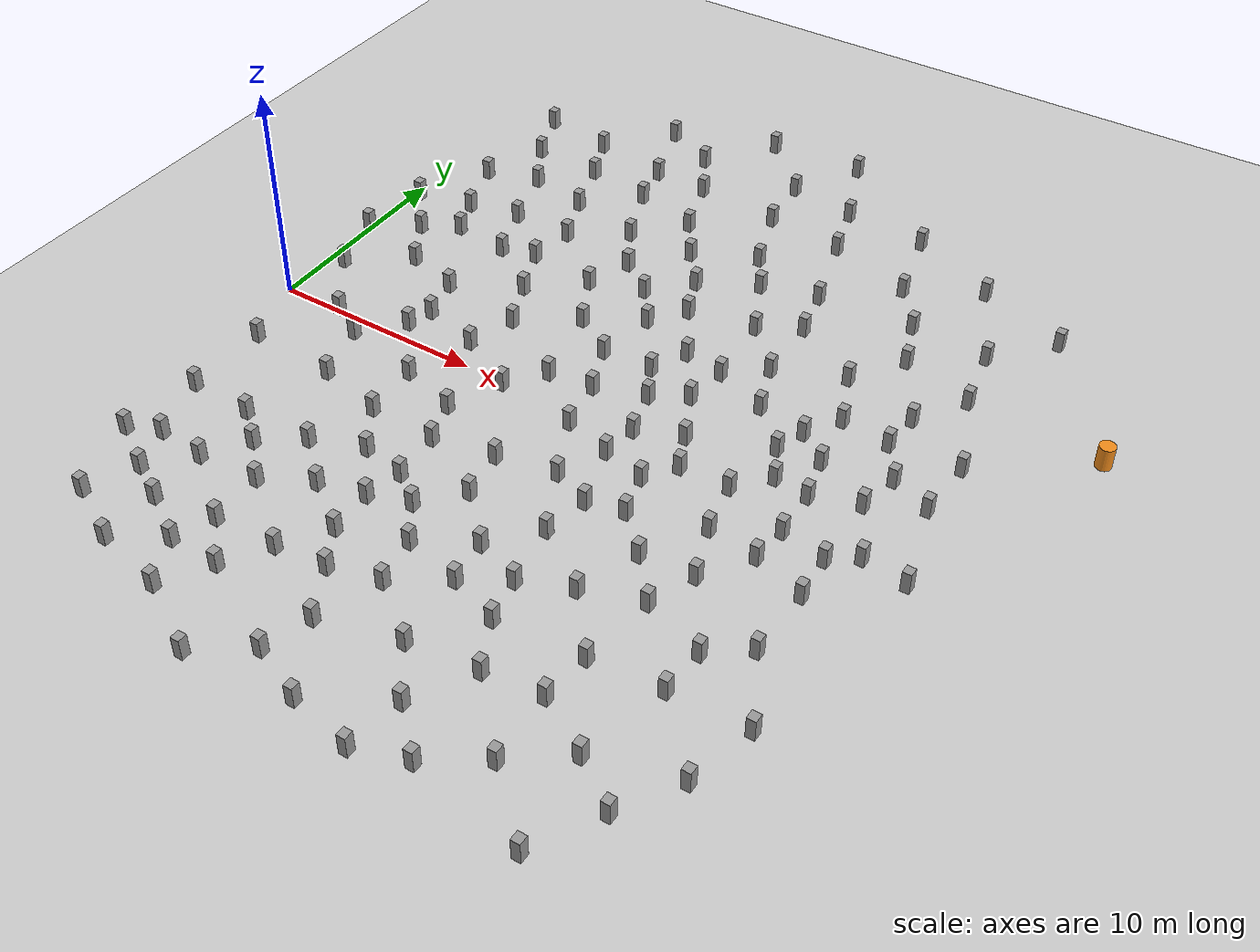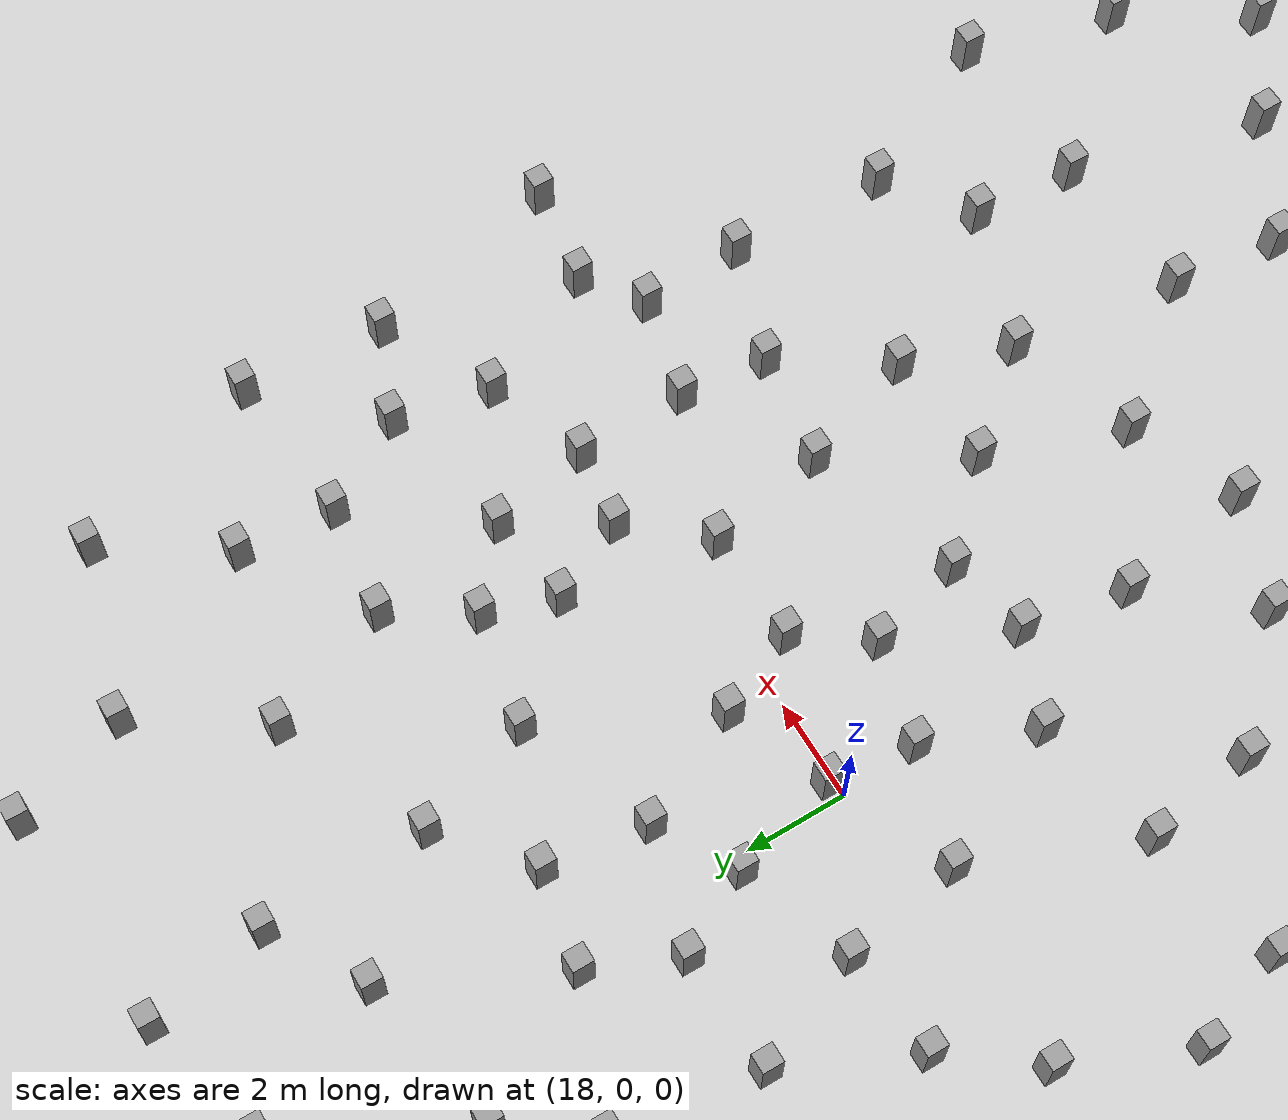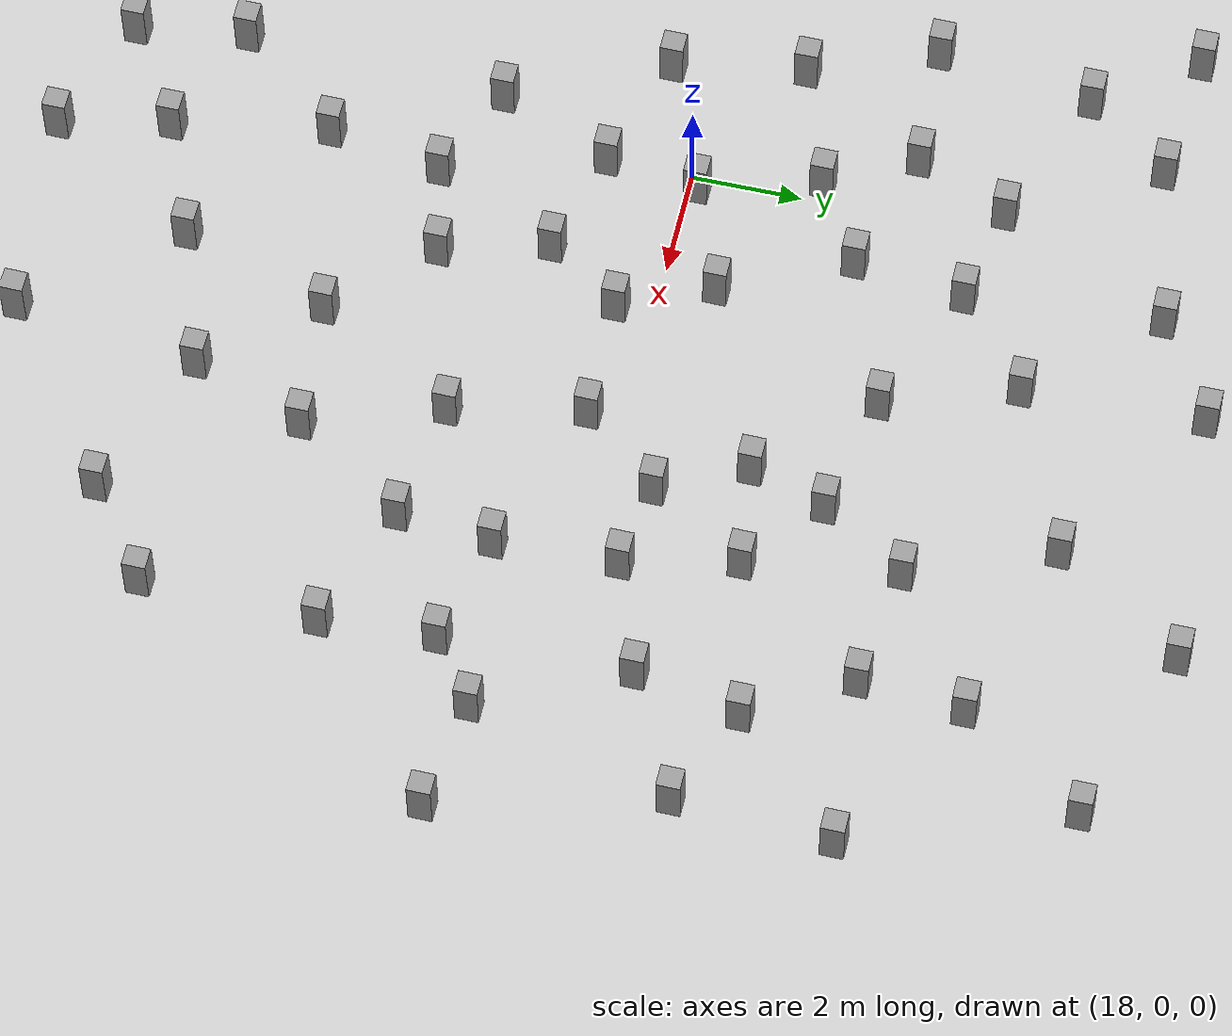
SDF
<?xml version="1.0" ?>
<sdf version="1.10">
  <world name="obstacle_field">
    <plugin name="gz::sim::systems::Physics" filename="gz-sim-physics-system"/>
    <plugin name="gz::sim::systems::Sensors" filename="gz-sim-sensors-system">
      <render_engine>ogre2</render_engine>
    </plugin>
    <plugin name="gz::sim::systems::Imu" filename="gz-sim-imu-system"/>
    <plugin name="gz::sim::systems::SceneBroadcaster" filename="gz-sim-scene-broadcaster-system"/>
    <plugin name="gz::sim::systems::UserCommands" filename="gz-sim-user-commands-system"/>
    <gravity>0 0 -9.8000000000000007</gravity>
    <magnetic_field>5.6450000000000002e-06 2.2875799999999999e-05 -4.2388400000000002e-05</magnetic_field>
    <atmosphere type="adiabatic"/>
    <physics name="default_physics" type="ignored">
      <max_step_size>0.001</max_step_size>
      <real_time_factor>0.1</real_time_factor>
      <real_time_update_rate>1000</real_time_update_rate>
    </physics>
    <scene>
      <ambient>0.400000006 0.400000006 0.400000006 1</ambient>
      <background>0.699999988 0.699999988 0.699999988 1</background>
      <shadows>false</shadows>
    </scene>
    <model name="ground_plane">
      <static>true</static>
      <link name="link">
        <collision name="collision">
          <geometry>
            <plane>
              <normal>0 0 1</normal>
              <size>100 100</size>
            </plane>
          </geometry>
          <surface>
            <friction>
              <ode>
                <mu>1000</mu>
                <mu2>1000</mu2>
                <slip1>0</slip1>
                <slip2>0</slip2>
              </ode>
            </friction>
            <bounce>
              <restitution_coefficient>0</restitution_coefficient>
            </bounce>
            <contact/>
          </surface>
        </collision>
        <visual name="visual">
          <cast_shadows>false</cast_shadows>
          <geometry>
            <plane>
              <normal>0 0 1</normal>
              <size>100 100</size>
            </plane>
          </geometry>
          <material>
            <script>
              <uri>file://media/materials/scripts/gazebo.material</uri>
              <name>Gazebo/Grey</name>
            </script>
          </material>
        </visual>
        <pose>0 0 0 0 0 0</pose>
        <inertial>
          <pose>0 0 0 0 0 0</pose>
          <mass>1</mass>
          <inertia>
            <ixx>1</ixx>
            <ixy>0</ixy>
            <ixz>0</ixz>
            <iyy>1</iyy>
            <iyz>0</iyz>
            <izz>1</izz>
          </inertia>
        </inertial>
        <enable_wind>false</enable_wind>
      </link>
      <pose>0 0 0 0 0 0</pose>
      <self_collide>false</self_collide>
    </model>
    <model name="unit_box_0_clone_1">
      <static>true</static>
      <pose>6.2657436504736737 0.77969248417705894 0.50000007797714363 -1.6275317496910021e-11 -4.3435819184663048e-07 -0.00050313957710125773</pose>
      <link name="link">
        <inertial>
          <mass>1</mass>
          <inertia>
            <ixx>0.16666700000000001</ixx>
            <ixy>0</ixy>
            <ixz>0</ixz>
            <iyy>0.16666700000000001</iyy>
            <iyz>0</iyz>
            <izz>0.16666700000000001</izz>
          </inertia>
          <pose>0 0 0 0 0 0</pose>
        </inertial>
        <collision name="collision">
          <geometry>
            <box>
              <size>0.392878 0.42264299999999999 1</size>
            </box>
          </geometry>
          <max_contacts>10</max_contacts>
          <surface>
            <friction>
              <ode/>
            </friction>
            <bounce/>
            <contact/>
          </surface>
        </collision>
        <visual name="visual">
          <geometry>
            <box>
              <size>0.392878 0.42264299999999999 1</size>
            </box>
          </geometry>
          <material>
            <script>
              <name>Gazebo/Grey</name>
              <uri>file://media/materials/scripts/gazebo.material</uri>
            </script>
          </material>
        </visual>
        <pose>0 0 0 0 0 0</pose>
        <enable_wind>false</enable_wind>
      </link>
      <self_collide>false</self_collide>
    </model>
    <model name="unit_box_0_clone_3">
      <static>true</static>
      <pose>8.3935060501098633 -1.9078499078750608 0.50000220537185669 -1.370750240686099e-06 -1.9236804040479009e-06 -0.00054700212289131452</pose>
      <link name="link">
        <inertial>
          <mass>1</mass>
          <inertia>
            <ixx>0.16666700000000001</ixx>
            <ixy>0</ixy>
            <ixz>0</ixz>
            <iyy>0.16666700000000001</iyy>
            <iyz>0</iyz>
            <izz>0.16666700000000001</izz>
          </inertia>
          <pose>0 0 0 0 0 0</pose>
        </inertial>
        <collision name="collision">
          <geometry>
            <box>
              <size>0.392878 0.42264299999999999 1</size>
            </box>
          </geometry>
          <max_contacts>10</max_contacts>
          <surface>
            <friction>
              <ode/>
            </friction>
            <bounce/>
            <contact/>
          </surface>
        </collision>
        <visual name="visual">
          <geometry>
            <box>
              <size>0.392878 0.42264299999999999 1</size>
            </box>
          </geometry>
          <material>
            <script>
              <name>Gazebo/Grey</name>
              <uri>file://media/materials/scripts/gazebo.material</uri>
            </script>
          </material>
        </visual>
        <pose>0 0 0 0 0 0</pose>
        <enable_wind>false</enable_wind>
      </link>
      <self_collide>false</self_collide>
    </model>
    <model name="unit_box_0_clone_5">
      <static>true</static>
      <pose>6.5936288833618164 1.9747054576873777 0.50000000000000011 1.4519074795443774e-11 5.7575513409192599e-07 -0.00056817313018064084</pose>
      <link name="link">
        <inertial>
          <mass>1</mass>
          <inertia>
            <ixx>0.16666700000000001</ixx>
            <ixy>0</ixy>
            <ixz>0</ixz>
            <iyy>0.16666700000000001</iyy>
            <iyz>0</iyz>
            <izz>0.16666700000000001</izz>
          </inertia>
          <pose>0 0 0 0 0 0</pose>
        </inertial>
        <collision name="collision">
          <geometry>
            <box>
              <size>0.392878 0.42264299999999999 1</size>
            </box>
          </geometry>
          <max_contacts>10</max_contacts>
          <surface>
            <friction>
              <ode/>
            </friction>
            <bounce/>
            <contact/>
          </surface>
        </collision>
        <visual name="visual">
          <geometry>
            <box>
              <size>0.392878 0.42264299999999999 1</size>
            </box>
          </geometry>
          <material>
            <script>
              <name>Gazebo/Grey</name>
              <uri>file://media/materials/scripts/gazebo.material</uri>
            </script>
          </material>
        </visual>
        <pose>0 0 0 0 0 0</pose>
        <enable_wind>false</enable_wind>
      </link>
      <self_collide>false</self_collide>
    </model>
    <model name="unit_box_0_clone_5_clone">
      <static>true</static>
      <pose>9.3323705005976016 1.1743509997080097 0.49999999632621162 5.2793814997311371e-13 -5.7080690061872796e-13 -0.00059524702849138831</pose>
      <link name="link">
        <inertial>
          <mass>1</mass>
          <inertia>
            <ixx>0.16666700000000001</ixx>
            <ixy>0</ixy>
            <ixz>0</ixz>
            <iyy>0.16666700000000001</iyy>
            <iyz>0</iyz>
            <izz>0.16666700000000001</izz>
          </inertia>
          <pose>0 0 0 0 0 0</pose>
        </inertial>
        <collision name="collision">
          <geometry>
            <box>
              <size>0.392878 0.42264299999999999 1</size>
            </box>
          </geometry>
          <max_contacts>10</max_contacts>
          <surface>
            <friction>
              <ode/>
            </friction>
            <bounce/>
            <contact/>
          </surface>
        </collision>
        <visual name="visual">
          <geometry>
            <box>
              <size>0.392878 0.42264299999999999 1</size>
            </box>
          </geometry>
          <material>
            <script>
              <name>Gazebo/Grey</name>
              <uri>file://media/materials/scripts/gazebo.material</uri>
            </script>
          </material>
        </visual>
        <pose>0 0 0 0 0 0</pose>
        <enable_wind>false</enable_wind>
      </link>
      <self_collide>false</self_collide>
    </model>
    <model name="unit_box_0_clone_5_clone_0">
      <static>true</static>
      <pose>6.0699167251586905 3.9886112213134766 0.49999880790710455 -6.4980011606417069e-08 -1.2996003264999317e-07 -0.00059701014650511103</pose>
      <link name="link">
        <inertial>
          <mass>1</mass>
          <inertia>
            <ixx>0.16666700000000001</ixx>
            <ixy>0</ixy>
            <ixz>0</ixz>
            <iyy>0.16666700000000001</iyy>
            <iyz>0</iyz>
            <izz>0.16666700000000001</izz>
          </inertia>
          <pose>0 0 0 0 0 0</pose>
        </inertial>
        <collision name="collision">
          <geometry>
            <box>
              <size>0.392878 0.42264299999999999 1</size>
            </box>
          </geometry>
          <max_contacts>10</max_contacts>
          <surface>
            <friction>
              <ode/>
            </friction>
            <bounce/>
            <contact/>
          </surface>
        </collision>
        <visual name="visual">
          <geometry>
            <box>
              <size>0.392878 0.42264299999999999 1</size>
            </box>
          </geometry>
          <material>
            <script>
              <name>Gazebo/Grey</name>
              <uri>file://media/materials/scripts/gazebo.material</uri>
            </script>
          </material>
        </visual>
        <pose>0 0 0 0 0 0</pose>
        <enable_wind>false</enable_wind>
      </link>
      <self_collide>false</self_collide>
    </model>
    <model name="unit_box_0_clone_5_clone_1">
      <static>true</static>
      <pose>8.6066904067993146 -4.5795798301696777 0.49999898672103876 -6.4980005139673518e-08 -6.4980100031907793e-08 -0.00061501101022146956</pose>
      <link name="link">
        <inertial>
          <mass>1</mass>
          <inertia>
            <ixx>0.16666700000000001</ixx>
            <ixy>0</ixy>
            <ixz>0</ixz>
            <iyy>0.16666700000000001</iyy>
            <iyz>0</iyz>
            <izz>0.16666700000000001</izz>
          </inertia>
          <pose>0 0 0 0 0 0</pose>
        </inertial>
        <collision name="collision">
          <geometry>
            <box>
              <size>0.392878 0.42264299999999999 1</size>
            </box>
          </geometry>
          <max_contacts>10</max_contacts>
          <surface>
            <friction>
              <ode/>
            </friction>
            <bounce/>
            <contact/>
          </surface>
        </collision>
        <visual name="visual">
          <geometry>
            <box>
              <size>0.392878 0.42264299999999999 1</size>
            </box>
          </geometry>
          <material>
            <script>
              <name>Gazebo/Grey</name>
              <uri>file://media/materials/scripts/gazebo.material</uri>
            </script>
          </material>
        </visual>
        <pose>0 0 0 0 0 0</pose>
        <enable_wind>false</enable_wind>
      </link>
      <self_collide>false</self_collide>
    </model>
    <model name="unit_box_0_clone_5_clone_2">
      <static>true</static>
      <pose>11.079571723937987 -2.7620170116424569 0.49999886751174927 -1.2996001171595163e-07 6.4980000871064096e-08 -0.0006110100471822395</pose>
      <link name="link">
        <inertial>
          <mass>1</mass>
          <inertia>
            <ixx>0.16666700000000001</ixx>
            <ixy>0</ixy>
            <ixz>0</ixz>
            <iyy>0.16666700000000001</iyy>
            <iyz>0</iyz>
            <izz>0.16666700000000001</izz>
          </inertia>
          <pose>0 0 0 0 0 0</pose>
        </inertial>
        <collision name="collision">
          <geometry>
            <box>
              <size>0.392878 0.42264299999999999 1</size>
            </box>
          </geometry>
          <max_contacts>10</max_contacts>
          <surface>
            <friction>
              <ode/>
            </friction>
            <bounce/>
            <contact/>
          </surface>
        </collision>
        <visual name="visual">
          <geometry>
            <box>
              <size>0.392878 0.42264299999999999 1</size>
            </box>
          </geometry>
          <material>
            <script>
              <name>Gazebo/Grey</name>
              <uri>file://media/materials/scripts/gazebo.material</uri>
            </script>
          </material>
        </visual>
        <pose>0 0 0 0 0 0</pose>
        <enable_wind>false</enable_wind>
      </link>
      <self_collide>false</self_collide>
    </model>
    <model name="unit_box_0_clone_5_clone_3">
      <static>true</static>
      <pose>11.777527809143065 -4.7175898551940918 0.49999967217445368 -1.9494004406307468e-07 6.4980013555370398e-08 -0.00059401012260828481</pose>
      <link name="link">
        <inertial>
          <mass>1</mass>
          <inertia>
            <ixx>0.16666700000000001</ixx>
            <ixy>0</ixy>
            <ixz>0</ixz>
            <iyy>0.16666700000000001</iyy>
            <iyz>0</iyz>
            <izz>0.16666700000000001</izz>
          </inertia>
          <pose>0 0 0 0 0 0</pose>
        </inertial>
        <collision name="collision">
          <geometry>
            <box>
              <size>0.392878 0.42264299999999999 1</size>
            </box>
          </geometry>
          <max_contacts>10</max_contacts>
          <surface>
            <friction>
              <ode/>
            </friction>
            <bounce/>
            <contact/>
          </surface>
        </collision>
        <visual name="visual">
          <geometry>
            <box>
              <size>0.392878 0.42264299999999999 1</size>
            </box>
          </geometry>
          <material>
            <script>
              <name>Gazebo/Grey</name>
              <uri>file://media/materials/scripts/gazebo.material</uri>
            </script>
          </material>
        </visual>
        <pose>0 0 0 0 0 0</pose>
        <enable_wind>false</enable_wind>
      </link>
      <self_collide>false</self_collide>
    </model>
    <model name="unit_box_0_clone_5_clone_2_clone">
      <static>true</static>
      <pose>13.357701301574707 1.3140759468078616 0.50000154972076394 5.3031405220818341e-07 1.6416701695930004e-07 -0.00069378602791120086</pose>
      <link name="link">
        <inertial>
          <mass>1</mass>
          <inertia>
            <ixx>0.16666700000000001</ixx>
            <ixy>0</ixy>
            <ixz>0</ixz>
            <iyy>0.16666700000000001</iyy>
            <iyz>0</iyz>
            <izz>0.16666700000000001</izz>
          </inertia>
          <pose>0 0 0 0 0 0</pose>
        </inertial>
        <collision name="collision">
          <geometry>
            <box>
              <size>0.392878 0.42264299999999999 1</size>
            </box>
          </geometry>
          <max_contacts>10</max_contacts>
          <surface>
            <friction>
              <ode/>
            </friction>
            <bounce/>
            <contact/>
          </surface>
        </collision>
        <visual name="visual">
          <geometry>
            <box>
              <size>0.392878 0.42264299999999999 1</size>
            </box>
          </geometry>
          <material>
            <script>
              <name>Gazebo/Grey</name>
              <uri>file://media/materials/scripts/gazebo.material</uri>
            </script>
          </material>
        </visual>
        <pose>0 0 0 0 0 0</pose>
        <enable_wind>false</enable_wind>
      </link>
      <self_collide>false</self_collide>
    </model>
    <model name="unit_box_0_clone_5_clone_2_clone_1">
      <static>true</static>
      <pose>4.6627094992486624 -1.0221909996353336 0.49999999632621162 -5.3290856622420438e-13 5.7520338949519755e-13 -0.00074748900662532502</pose>
      <link name="link">
        <inertial>
          <mass>1</mass>
          <inertia>
            <ixx>0.16666700000000001</ixx>
            <ixy>0</ixy>
            <ixz>0</ixz>
            <iyy>0.16666700000000001</iyy>
            <iyz>0</iyz>
            <izz>0.16666700000000001</izz>
          </inertia>
          <pose>0 0 0 0 0 0</pose>
        </inertial>
        <collision name="collision">
          <geometry>
            <box>
              <size>0.392878 0.42264299999999999 1</size>
            </box>
          </geometry>
          <max_contacts>10</max_contacts>
          <surface>
            <friction>
              <ode/>
            </friction>
            <bounce/>
            <contact/>
          </surface>
        </collision>
        <visual name="visual">
          <geometry>
            <box>
              <size>0.392878 0.42264299999999999 1</size>
            </box>
          </geometry>
          <material>
            <script>
              <name>Gazebo/Grey</name>
              <uri>file://media/materials/scripts/gazebo.material</uri>
            </script>
          </material>
        </visual>
        <pose>0 0 0 0 0 0</pose>
        <enable_wind>false</enable_wind>
      </link>
      <self_collide>false</self_collide>
    </model>
    <model name="unit_box_0_clone_5_clone_2_clone_2">
      <static>true</static>
      <pose>2.9894994992669472 -0.022526999643910483 0.49999999632621162 -5.3119264489559768e-13 5.6826736232843934e-13 -0.00072945448038697004</pose>
      <link name="link">
        <inertial>
          <mass>1</mass>
          <inertia>
            <ixx>0.16666700000000001</ixx>
            <ixy>0</ixy>
            <ixz>0</ixz>
            <iyy>0.16666700000000001</iyy>
            <iyz>0</iyz>
            <izz>0.16666700000000001</izz>
          </inertia>
          <pose>0 0 0 0 0 0</pose>
        </inertial>
        <collision name="collision">
          <geometry>
            <box>
              <size>0.392878 0.42264299999999999 1</size>
            </box>
          </geometry>
          <max_contacts>10</max_contacts>
          <surface>
            <friction>
              <ode/>
            </friction>
            <bounce/>
            <contact/>
          </surface>
        </collision>
        <visual name="visual">
          <geometry>
            <box>
              <size>0.392878 0.42264299999999999 1</size>
            </box>
          </geometry>
          <material>
            <script>
              <name>Gazebo/Grey</name>
              <uri>file://media/materials/scripts/gazebo.material</uri>
            </script>
          </material>
        </visual>
        <pose>0 0 0 0 0 0</pose>
        <enable_wind>false</enable_wind>
      </link>
      <self_collide>false</self_collide>
    </model>
    <model name="unit_box_0_clone_5_clone_2_clone_3">
      <static>true</static>
      <pose>12.111514091491701 -0.32596516609191872 0.50001299381256092 1.8970301151387148e-08 -6.8920802442025963e-06 -0.00060902103265276749</pose>
      <link name="link">
        <inertial>
          <mass>1</mass>
          <inertia>
            <ixx>0.16666700000000001</ixx>
            <ixy>0</ixy>
            <ixz>0</ixz>
            <iyy>0.16666700000000001</iyy>
            <iyz>0</iyz>
            <izz>0.16666700000000001</izz>
          </inertia>
          <pose>0 0 0 0 0 0</pose>
        </inertial>
        <collision name="collision">
          <geometry>
            <box>
              <size>0.392878 0.42264299999999999 1</size>
            </box>
          </geometry>
          <max_contacts>10</max_contacts>
          <surface>
            <friction>
              <ode/>
            </friction>
            <bounce/>
            <contact/>
          </surface>
        </collision>
        <visual name="visual">
          <geometry>
            <box>
              <size>0.392878 0.42264299999999999 1</size>
            </box>
          </geometry>
          <material>
            <script>
              <name>Gazebo/Grey</name>
              <uri>file://media/materials/scripts/gazebo.material</uri>
            </script>
          </material>
        </visual>
        <pose>0 0 0 0 0 0</pose>
        <enable_wind>false</enable_wind>
      </link>
      <self_collide>false</self_collide>
    </model>
    <model name="unit_box_0_clone_5_clone_2_clone_4">
      <static>true</static>
      <pose>14.512412071228029 3.8057172298431405 0.49999919533729553 -1.4207401016797583e-07 -5.6431707507392635e-08 -0.00075502010828045992</pose>
      <link name="link">
        <inertial>
          <mass>1</mass>
          <inertia>
            <ixx>0.16666700000000001</ixx>
            <ixy>0</ixy>
            <ixz>0</ixz>
            <iyy>0.16666700000000001</iyy>
            <iyz>0</iyz>
            <izz>0.16666700000000001</izz>
          </inertia>
          <pose>0 0 0 0 0 0</pose>
        </inertial>
        <collision name="collision">
          <geometry>
            <box>
              <size>0.392878 0.42264299999999999 1</size>
            </box>
          </geometry>
          <max_contacts>10</max_contacts>
          <surface>
            <friction>
              <ode/>
            </friction>
            <bounce/>
            <contact/>
          </surface>
        </collision>
        <visual name="visual">
          <geometry>
            <box>
              <size>0.392878 0.42264299999999999 1</size>
            </box>
          </geometry>
          <material>
            <script>
              <name>Gazebo/Grey</name>
              <uri>file://media/materials/scripts/gazebo.material</uri>
            </script>
          </material>
        </visual>
        <pose>0 0 0 0 0 0</pose>
        <enable_wind>false</enable_wind>
      </link>
      <self_collide>false</self_collide>
    </model>
    <model name="unit_box_0_clone_5_clone_2_clone_5">
      <static>true</static>
      <pose>14.542879104614256 -4.1722455024719238 0.49999919533729553 -1.299600133939024e-07 6.4980100587631842e-08 -0.00063201201838560179</pose>
      <link name="link">
        <inertial>
          <mass>1</mass>
          <inertia>
            <ixx>0.16666700000000001</ixx>
            <ixy>0</ixy>
            <ixz>0</ixz>
            <iyy>0.16666700000000001</iyy>
            <iyz>0</iyz>
            <izz>0.16666700000000001</izz>
          </inertia>
          <pose>0 0 0 0 0 0</pose>
        </inertial>
        <collision name="collision">
          <geometry>
            <box>
              <size>0.392878 0.42264299999999999 1</size>
            </box>
          </geometry>
          <max_contacts>10</max_contacts>
          <surface>
            <friction>
              <ode/>
            </friction>
            <bounce/>
            <contact/>
          </surface>
        </collision>
        <visual name="visual">
          <geometry>
            <box>
              <size>0.392878 0.42264299999999999 1</size>
            </box>
          </geometry>
          <material>
            <script>
              <name>Gazebo/Grey</name>
              <uri>file://media/materials/scripts/gazebo.material</uri>
            </script>
          </material>
        </visual>
        <pose>0 0 0 0 0 0</pose>
        <enable_wind>false</enable_wind>
      </link>
      <self_collide>false</self_collide>
    </model>
    <model name="unit_box_0_clone_5_clone_2_clone_6">
      <static>true</static>
      <pose>9.9725370407104474 3.414785623550415 0.49999925494194025 -1.0111800399782683e-07 -2.2782001280568572e-07 -0.00061600903908471728</pose>
      <link name="link">
        <inertial>
          <mass>1</mass>
          <inertia>
            <ixx>0.16666700000000001</ixx>
            <ixy>0</ixy>
            <ixz>0</ixz>
            <iyy>0.16666700000000001</iyy>
            <iyz>0</iyz>
            <izz>0.16666700000000001</izz>
          </inertia>
          <pose>0 0 0 0 0 0</pose>
        </inertial>
        <collision name="collision">
          <geometry>
            <box>
              <size>0.392878 0.42264299999999999 1</size>
            </box>
          </geometry>
          <max_contacts>10</max_contacts>
          <surface>
            <friction>
              <ode/>
            </friction>
            <bounce/>
            <contact/>
          </surface>
        </collision>
        <visual name="visual">
          <geometry>
            <box>
              <size>0.392878 0.42264299999999999 1</size>
            </box>
          </geometry>
          <material>
            <script>
              <name>Gazebo/Grey</name>
              <uri>file://media/materials/scripts/gazebo.material</uri>
            </script>
          </material>
        </visual>
        <pose>0 0 0 0 0 0</pose>
        <enable_wind>false</enable_wind>
      </link>
      <self_collide>false</self_collide>
    </model>
    <model name="unit_box_0_clone_5_clone_2_clone_1_clone">
      <static>true</static>
      <pose>15.868999998624535 -0.84647450002033475 0.49999999632621167 -5.2823337413909975e-13 -1.9489132497437662e-14 -0.00091790506168357654</pose>
      <link name="link">
        <inertial>
          <mass>1</mass>
          <inertia>
            <ixx>0.16666700000000001</ixx>
            <ixy>0</ixy>
            <ixz>0</ixz>
            <iyy>0.16666700000000001</iyy>
            <iyz>0</iyz>
            <izz>0.16666700000000001</izz>
          </inertia>
          <pose>0 0 0 0 0 0</pose>
        </inertial>
        <collision name="collision">
          <geometry>
            <box>
              <size>0.392878 0.42264299999999999 1</size>
            </box>
          </geometry>
          <max_contacts>10</max_contacts>
          <surface>
            <friction>
              <ode/>
            </friction>
            <bounce/>
            <contact/>
          </surface>
        </collision>
        <visual name="visual">
          <geometry>
            <box>
              <size>0.392878 0.42264299999999999 1</size>
            </box>
          </geometry>
          <material>
            <script>
              <name>Gazebo/Grey</name>
              <uri>file://media/materials/scripts/gazebo.material</uri>
            </script>
          </material>
        </visual>
        <pose>0 0 0 0 0 0</pose>
        <enable_wind>false</enable_wind>
      </link>
      <self_collide>false</self_collide>
    </model>
    <model name="unit_box_0_clone_5_clone_2_clone_1_clone_0">
      <static>true</static>
      <pose>18.311199000446361 0.16262650092666658 0.49999999632621162 5.2857825764613169e-13 5.6755324662750699e-13 -0.00092091398351414771</pose>
      <link name="link">
        <inertial>
          <mass>1</mass>
          <inertia>
            <ixx>0.16666700000000001</ixx>
            <ixy>0</ixy>
            <ixz>0</ixz>
            <iyy>0.16666700000000001</iyy>
            <iyz>0</iyz>
            <izz>0.16666700000000001</izz>
          </inertia>
          <pose>0 0 0 0 0 0</pose>
        </inertial>
        <collision name="collision">
          <geometry>
            <box>
              <size>0.392878 0.42264299999999999 1</size>
            </box>
          </geometry>
          <max_contacts>10</max_contacts>
          <surface>
            <friction>
              <ode/>
            </friction>
            <bounce/>
            <contact/>
          </surface>
        </collision>
        <visual name="visual">
          <geometry>
            <box>
              <size>0.392878 0.42264299999999999 1</size>
            </box>
          </geometry>
          <material>
            <script>
              <name>Gazebo/Grey</name>
              <uri>file://media/materials/scripts/gazebo.material</uri>
            </script>
          </material>
        </visual>
        <pose>0 0 0 0 0 0</pose>
        <enable_wind>false</enable_wind>
      </link>
      <self_collide>false</self_collide>
    </model>
    <model name="unit_box_0_clone_5_clone_2_clone_1_clone_1">
      <static>true</static>
      <pose>17.68789749996462 2.3268800023325551 0.49999999632621189 -3.4218145334087293e-14 5.7689899603250314e-13 -0.0009339533180120665</pose>
      <link name="link">
        <inertial>
          <mass>1</mass>
          <inertia>
            <ixx>0.16666700000000001</ixx>
            <ixy>0</ixy>
            <ixz>0</ixz>
            <iyy>0.16666700000000001</iyy>
            <iyz>0</iyz>
            <izz>0.16666700000000001</izz>
          </inertia>
          <pose>0 0 0 0 0 0</pose>
        </inertial>
        <collision name="collision">
          <geometry>
            <box>
              <size>0.392878 0.42264299999999999 1</size>
            </box>
          </geometry>
          <max_contacts>10</max_contacts>
          <surface>
            <friction>
              <ode/>
            </friction>
            <bounce/>
            <contact/>
          </surface>
        </collision>
        <visual name="visual">
          <geometry>
            <box>
              <size>0.392878 0.42264299999999999 1</size>
            </box>
          </geometry>
          <material>
            <script>
              <name>Gazebo/Grey</name>
              <uri>file://media/materials/scripts/gazebo.material</uri>
            </script>
          </material>
        </visual>
        <pose>0 0 0 0 0 0</pose>
        <enable_wind>false</enable_wind>
      </link>
      <self_collide>false</self_collide>
    </model>
    <model name="unit_box_0_clone_5_clone_2_clone_1_clone_2">
      <static>true</static>
      <pose>15.434800148010254 1.5389300584793086 0.49999898672103887 6.4981409769369614e-08 -1.2996301319880549e-07 -0.00091503511145289934</pose>
      <link name="link">
        <inertial>
          <mass>1</mass>
          <inertia>
            <ixx>0.16666700000000001</ixx>
            <ixy>0</ixy>
            <ixz>0</ixz>
            <iyy>0.16666700000000001</iyy>
            <iyz>0</iyz>
            <izz>0.16666700000000001</izz>
          </inertia>
          <pose>0 0 0 0 0 0</pose>
        </inertial>
        <collision name="collision">
          <geometry>
            <box>
              <size>0.392878 0.42264299999999999 1</size>
            </box>
          </geometry>
          <max_contacts>10</max_contacts>
          <surface>
            <friction>
              <ode/>
            </friction>
            <bounce/>
            <contact/>
          </surface>
        </collision>
        <visual name="visual">
          <geometry>
            <box>
              <size>0.392878 0.42264299999999999 1</size>
            </box>
          </geometry>
          <material>
            <script>
              <name>Gazebo/Grey</name>
              <uri>file://media/materials/scripts/gazebo.material</uri>
            </script>
          </material>
        </visual>
        <pose>0 0 0 0 0 0</pose>
        <enable_wind>false</enable_wind>
      </link>
      <self_collide>false</self_collide>
    </model>
    <model name="unit_box_0_clone_5_clone_2_clone_1_clone_3">
      <static>true</static>
      <pose>18.098298502233011 -1.5254174986159381 0.49999999632621189 5.3011672150700357e-13 5.7568862095144775e-13 -0.00090185847263046239</pose>
      <link name="link">
        <inertial>
          <mass>1</mass>
          <inertia>
            <ixx>0.16666700000000001</ixx>
            <ixy>0</ixy>
            <ixz>0</ixz>
            <iyy>0.16666700000000001</iyy>
            <iyz>0</iyz>
            <izz>0.16666700000000001</izz>
          </inertia>
          <pose>0 0 0 0 0 0</pose>
        </inertial>
        <collision name="collision">
          <geometry>
            <box>
              <size>0.392878 0.42264299999999999 1</size>
            </box>
          </geometry>
          <max_contacts>10</max_contacts>
          <surface>
            <friction>
              <ode/>
            </friction>
            <bounce/>
            <contact/>
          </surface>
        </collision>
        <visual name="visual">
          <geometry>
            <box>
              <size>0.392878 0.42264299999999999 1</size>
            </box>
          </geometry>
          <material>
            <script>
              <name>Gazebo/Grey</name>
              <uri>file://media/materials/scripts/gazebo.material</uri>
            </script>
          </material>
        </visual>
        <pose>0 0 0 0 0 0</pose>
        <enable_wind>false</enable_wind>
      </link>
      <self_collide>false</self_collide>
    </model>
    <model name="unit_box_0_clone_5_clone_2_clone_1_clone_4">
      <static>true</static>
      <pose>23.873258590698242 -7.5569562911987296 0.49999427795410156 1.4854402304388796e-06 -4.2134004978030306e-07 -0.00091601113852245078</pose>
      <link name="link">
        <inertial>
          <mass>1</mass>
          <inertia>
            <ixx>0.16666700000000001</ixx>
            <ixy>0</ixy>
            <ixz>0</ixz>
            <iyy>0.16666700000000001</iyy>
            <iyz>0</iyz>
            <izz>0.16666700000000001</izz>
          </inertia>
          <pose>0 0 0 0 0 0</pose>
        </inertial>
        <collision name="collision">
          <geometry>
            <box>
              <size>0.392878 0.42264299999999999 1</size>
            </box>
          </geometry>
          <max_contacts>10</max_contacts>
          <surface>
            <friction>
              <ode/>
            </friction>
            <bounce/>
            <contact/>
          </surface>
        </collision>
        <visual name="visual">
          <geometry>
            <box>
              <size>0.392878 0.42264299999999999 1</size>
            </box>
          </geometry>
          <material>
            <script>
              <name>Gazebo/Grey</name>
              <uri>file://media/materials/scripts/gazebo.material</uri>
            </script>
          </material>
        </visual>
        <pose>0 0 0 0 0 0</pose>
        <enable_wind>false</enable_wind>
      </link>
      <self_collide>false</self_collide>
    </model>
    <model name="unit_box_0_clone_5_clone_2_clone_1_clone_5">
      <static>true</static>
      <pose>23.281000001394915 -0.62295649997908153 0.49999999632621167 5.3583029871682226e-13 2.0334165817450371e-14 -0.00093094414213781276</pose>
      <link name="link">
        <inertial>
          <mass>1</mass>
          <inertia>
            <ixx>0.16666700000000001</ixx>
            <ixy>0</ixy>
            <ixz>0</ixz>
            <iyy>0.16666700000000001</iyy>
            <iyz>0</iyz>
            <izz>0.16666700000000001</izz>
          </inertia>
          <pose>0 0 0 0 0 0</pose>
        </inertial>
        <collision name="collision">
          <geometry>
            <box>
              <size>0.392878 0.42264299999999999 1</size>
            </box>
          </geometry>
          <max_contacts>10</max_contacts>
          <surface>
            <friction>
              <ode/>
            </friction>
            <bounce/>
            <contact/>
          </surface>
        </collision>
        <visual name="visual">
          <geometry>
            <box>
              <size>0.392878 0.42264299999999999 1</size>
            </box>
          </geometry>
          <material>
            <script>
              <name>Gazebo/Grey</name>
              <uri>file://media/materials/scripts/gazebo.material</uri>
            </script>
          </material>
        </visual>
        <pose>0 0 0 0 0 0</pose>
        <enable_wind>false</enable_wind>
      </link>
      <self_collide>false</self_collide>
    </model>
    <model name="unit_box_0_clone_5_clone_2_clone_1_clone_6">
      <static>true</static>
      <pose>21.040797998131531 -0.67384499817278598 0.49999999632621017 -5.2764079948247899e-13 5.6934004513067279e-13 -0.00092492595944877634</pose>
      <link name="link">
        <inertial>
          <mass>1</mass>
          <inertia>
            <ixx>0.16666700000000001</ixx>
            <ixy>0</ixy>
            <ixz>0</ixz>
            <iyy>0.16666700000000001</iyy>
            <iyz>0</iyz>
            <izz>0.16666700000000001</izz>
          </inertia>
          <pose>0 0 0 0 0 0</pose>
        </inertial>
        <collision name="collision">
          <geometry>
            <box>
              <size>0.392878 0.42264299999999999 1</size>
            </box>
          </geometry>
          <max_contacts>10</max_contacts>
          <surface>
            <friction>
              <ode/>
            </friction>
            <bounce/>
            <contact/>
          </surface>
        </collision>
        <visual name="visual">
          <geometry>
            <box>
              <size>0.392878 0.42264299999999999 1</size>
            </box>
          </geometry>
          <material>
            <script>
              <name>Gazebo/Grey</name>
              <uri>file://media/materials/scripts/gazebo.material</uri>
            </script>
          </material>
        </visual>
        <pose>0 0 0 0 0 0</pose>
        <enable_wind>false</enable_wind>
      </link>
      <self_collide>false</self_collide>
    </model>
    <model name="unit_box_0_clone_5_clone_2_clone_1_clone_7">
      <static>true</static>
      <pose>26.085701500914059 0.61762899866997278 0.49999999632621056 5.3403679802891421e-13 -5.7311350069928465e-13 -0.00089584140926725201</pose>
      <link name="link">
        <inertial>
          <mass>1</mass>
          <inertia>
            <ixx>0.16666700000000001</ixx>
            <ixy>0</ixy>
            <ixz>0</ixz>
            <iyy>0.16666700000000001</iyy>
            <iyz>0</iyz>
            <izz>0.16666700000000001</izz>
          </inertia>
          <pose>0 0 0 0 0 0</pose>
        </inertial>
        <collision name="collision">
          <geometry>
            <box>
              <size>0.392878 0.42264299999999999 1</size>
            </box>
          </geometry>
          <max_contacts>10</max_contacts>
          <surface>
            <friction>
              <ode/>
            </friction>
            <bounce/>
            <contact/>
          </surface>
        </collision>
        <visual name="visual">
          <geometry>
            <box>
              <size>0.392878 0.42264299999999999 1</size>
            </box>
          </geometry>
          <material>
            <script>
              <name>Gazebo/Grey</name>
              <uri>file://media/materials/scripts/gazebo.material</uri>
            </script>
          </material>
        </visual>
        <pose>0 0 0 0 0 0</pose>
        <enable_wind>false</enable_wind>
      </link>
      <self_collide>false</self_collide>
    </model>
    <model name="unit_box_0_clone_5_clone_2_clone_1_clone_8">
      <static>true</static>
      <pose>23.743499499122006 2.4061790004238555 0.49999999632621162 -5.2722918672139091e-13 5.7505081275288677e-13 -0.00087277813948394734</pose>
      <link name="link">
        <inertial>
          <mass>1</mass>
          <inertia>
            <ixx>0.16666700000000001</ixx>
            <ixy>0</ixy>
            <ixz>0</ixz>
            <iyy>0.16666700000000001</iyy>
            <iyz>0</iyz>
            <izz>0.16666700000000001</izz>
          </inertia>
          <pose>0 0 0 0 0 0</pose>
        </inertial>
        <collision name="collision">
          <geometry>
            <box>
              <size>0.392878 0.42264299999999999 1</size>
            </box>
          </geometry>
          <max_contacts>10</max_contacts>
          <surface>
            <friction>
              <ode/>
            </friction>
            <bounce/>
            <contact/>
          </surface>
        </collision>
        <visual name="visual">
          <geometry>
            <box>
              <size>0.392878 0.42264299999999999 1</size>
            </box>
          </geometry>
          <material>
            <script>
              <name>Gazebo/Grey</name>
              <uri>file://media/materials/scripts/gazebo.material</uri>
            </script>
          </material>
        </visual>
        <pose>0 0 0 0 0 0</pose>
        <enable_wind>false</enable_wind>
      </link>
      <self_collide>false</self_collide>
    </model>
    <model name="unit_box_0_clone_5_clone_2_clone_1_clone_9">
      <static>true</static>
      <pose>26.185300500870937 -1.6168790004205584 0.49999999632621162 5.3733576133487237e-13 -5.6738309889700981e-13 -0.00086575953363054287</pose>
      <link name="link">
        <inertial>
          <mass>1</mass>
          <inertia>
            <ixx>0.16666700000000001</ixx>
            <ixy>0</ixy>
            <ixz>0</ixz>
            <iyy>0.16666700000000001</iyy>
            <iyz>0</iyz>
            <izz>0.16666700000000001</izz>
          </inertia>
          <pose>0 0 0 0 0 0</pose>
        </inertial>
        <collision name="collision">
          <geometry>
            <box>
              <size>0.392878 0.42264299999999999 1</size>
            </box>
          </geometry>
          <max_contacts>10</max_contacts>
          <surface>
            <friction>
              <ode/>
            </friction>
            <bounce/>
            <contact/>
          </surface>
        </collision>
        <visual name="visual">
          <geometry>
            <box>
              <size>0.392878 0.42264299999999999 1</size>
            </box>
          </geometry>
          <material>
            <script>
              <name>Gazebo/Grey</name>
              <uri>file://media/materials/scripts/gazebo.material</uri>
            </script>
          </material>
        </visual>
        <pose>0 0 0 0 0 0</pose>
        <enable_wind>false</enable_wind>
      </link>
      <self_collide>false</self_collide>
    </model>
    <model name="unit_box_0_clone_5_clone_2_clone_1_clone_10">
      <static>true</static>
      <pose>28.11344146728516 1.3615589141845703 0.50000101327896107 1.3707604314139031e-06 1.9236906132299216e-06 -0.00085200628493950091</pose>
      <link name="link">
        <inertial>
          <mass>1</mass>
          <inertia>
            <ixx>0.16666700000000001</ixx>
            <ixy>0</ixy>
            <ixz>0</ixz>
            <iyy>0.16666700000000001</iyy>
            <iyz>0</iyz>
            <izz>0.16666700000000001</izz>
          </inertia>
          <pose>0 0 0 0 0 0</pose>
        </inertial>
        <collision name="collision">
          <geometry>
            <box>
              <size>0.392878 0.42264299999999999 1</size>
            </box>
          </geometry>
          <max_contacts>10</max_contacts>
          <surface>
            <friction>
              <ode/>
            </friction>
            <bounce/>
            <contact/>
          </surface>
        </collision>
        <visual name="visual">
          <geometry>
            <box>
              <size>0.392878 0.42264299999999999 1</size>
            </box>
          </geometry>
          <material>
            <script>
              <name>Gazebo/Grey</name>
              <uri>file://media/materials/scripts/gazebo.material</uri>
            </script>
          </material>
        </visual>
        <pose>0 0 0 0 0 0</pose>
        <enable_wind>false</enable_wind>
      </link>
      <self_collide>false</self_collide>
    </model>
    <model name="unit_box_0_clone_5_clone_2_clone_1_clone_11">
      <static>true</static>
      <pose>27.395267486572269 5.1025390625 0.49999859929084778 -1.2996203613440209e-07 -6.4981223860486695e-08 -0.00086803028507682455</pose>
      <link name="link">
        <inertial>
          <mass>1</mass>
          <inertia>
            <ixx>0.16666700000000001</ixx>
            <ixy>0</ixy>
            <ixz>0</ixz>
            <iyy>0.16666700000000001</iyy>
            <iyz>0</iyz>
            <izz>0.16666700000000001</izz>
          </inertia>
          <pose>0 0 0 0 0 0</pose>
        </inertial>
        <collision name="collision">
          <geometry>
            <box>
              <size>0.392878 0.42264299999999999 1</size>
            </box>
          </geometry>
          <max_contacts>10</max_contacts>
          <surface>
            <friction>
              <ode/>
            </friction>
            <bounce/>
            <contact/>
          </surface>
        </collision>
        <visual name="visual">
          <geometry>
            <box>
              <size>0.392878 0.42264299999999999 1</size>
            </box>
          </geometry>
          <material>
            <script>
              <name>Gazebo/Grey</name>
              <uri>file://media/materials/scripts/gazebo.material</uri>
            </script>
          </material>
        </visual>
        <pose>0 0 0 0 0 0</pose>
        <enable_wind>false</enable_wind>
      </link>
      <self_collide>false</self_collide>
    </model>
    <model name="unit_box_0_clone_5_clone_2_clone_1_clone_12">
      <static>true</static>
      <pose>31.367098000865099 -1.5321189982137458 0.49999999632621184 5.291041142967215e-13 5.7289641262581815e-13 -0.00088882180784699897</pose>
      <link name="link">
        <inertial>
          <mass>1</mass>
          <inertia>
            <ixx>0.16666700000000001</ixx>
            <ixy>0</ixy>
            <ixz>0</ixz>
            <iyy>0.16666700000000001</iyy>
            <iyz>0</iyz>
            <izz>0.16666700000000001</izz>
          </inertia>
          <pose>0 0 0 0 0 0</pose>
        </inertial>
        <collision name="collision">
          <geometry>
            <box>
              <size>0.392878 0.42264299999999999 1</size>
            </box>
          </geometry>
          <max_contacts>10</max_contacts>
          <surface>
            <friction>
              <ode/>
            </friction>
            <bounce/>
            <contact/>
          </surface>
        </collision>
        <visual name="visual">
          <geometry>
            <box>
              <size>0.392878 0.42264299999999999 1</size>
            </box>
          </geometry>
          <material>
            <script>
              <name>Gazebo/Grey</name>
              <uri>file://media/materials/scripts/gazebo.material</uri>
            </script>
          </material>
        </visual>
        <pose>0 0 0 0 0 0</pose>
        <enable_wind>false</enable_wind>
      </link>
      <self_collide>false</self_collide>
    </model>
    <model name="unit_box_0_clone_5_clone_2_clone_1_clone_12_clone">
      <static>true</static>
      <pose>8.9821994995991616 5.6659995003911803 0.49999999632620984 -5.3647321036996375e-13 5.7486298194397711e-13 -0.00079258288375717531</pose>
      <link name="link">
        <inertial>
          <mass>1</mass>
          <inertia>
            <ixx>0.16666700000000001</ixx>
            <ixy>0</ixy>
            <ixz>0</ixz>
            <iyy>0.16666700000000001</iyy>
            <iyz>0</iyz>
            <izz>0.16666700000000001</izz>
          </inertia>
          <pose>0 0 0 0 0 0</pose>
        </inertial>
        <collision name="collision">
          <geometry>
            <box>
              <size>0.392878 0.42264299999999999 1</size>
            </box>
          </geometry>
          <max_contacts>10</max_contacts>
          <surface>
            <friction>
              <ode/>
            </friction>
            <bounce/>
            <contact/>
          </surface>
        </collision>
        <visual name="visual">
          <geometry>
            <box>
              <size>0.392878 0.42264299999999999 1</size>
            </box>
          </geometry>
          <material>
            <script>
              <name>Gazebo/Grey</name>
              <uri>file://media/materials/scripts/gazebo.material</uri>
            </script>
          </material>
        </visual>
        <pose>0 0 0 0 0 0</pose>
        <enable_wind>false</enable_wind>
      </link>
      <self_collide>false</self_collide>
    </model>
    <model name="unit_box_0_clone_5_clone_2_clone_1_clone_12_clone_0">
      <static>true</static>
      <pose>11.232299499207203 7.6263990003841595 0.49999999632621162 -5.3284593403060476e-13 5.6859901922787468e-13 -0.00078857408980502919</pose>
      <link name="link">
        <inertial>
          <mass>1</mass>
          <inertia>
            <ixx>0.16666700000000001</ixx>
            <ixy>0</ixy>
            <ixz>0</ixz>
            <iyy>0.16666700000000001</iyy>
            <iyz>0</iyz>
            <izz>0.16666700000000001</izz>
          </inertia>
          <pose>0 0 0 0 0 0</pose>
        </inertial>
        <collision name="collision">
          <geometry>
            <box>
              <size>0.392878 0.42264299999999999 1</size>
            </box>
          </geometry>
          <max_contacts>10</max_contacts>
          <surface>
            <friction>
              <ode/>
            </friction>
            <bounce/>
            <contact/>
          </surface>
        </collision>
        <visual name="visual">
          <geometry>
            <box>
              <size>0.392878 0.42264299999999999 1</size>
            </box>
          </geometry>
          <material>
            <script>
              <name>Gazebo/Grey</name>
              <uri>file://media/materials/scripts/gazebo.material</uri>
            </script>
          </material>
        </visual>
        <pose>0 0 0 0 0 0</pose>
        <enable_wind>false</enable_wind>
      </link>
      <self_collide>false</self_collide>
    </model>
    <model name="unit_box_0_clone_5_clone_2_clone_1_clone_12_clone_1">
      <static>true</static>
      <pose>8.0000010004007294 8.0000004992226383 0.49999999632621162 5.3360800315507531e-13 -5.7750973295664675e-13 -0.00078256106634871578</pose>
      <link name="link">
        <inertial>
          <mass>1</mass>
          <inertia>
            <ixx>0.16666700000000001</ixx>
            <ixy>0</ixy>
            <ixz>0</ixz>
            <iyy>0.16666700000000001</iyy>
            <iyz>0</iyz>
            <izz>0.16666700000000001</izz>
          </inertia>
          <pose>0 0 0 0 0 0</pose>
        </inertial>
        <collision name="collision">
          <geometry>
            <box>
              <size>0.392878 0.42264299999999999 1</size>
            </box>
          </geometry>
          <max_contacts>10</max_contacts>
          <surface>
            <friction>
              <ode/>
            </friction>
            <bounce/>
            <contact/>
          </surface>
        </collision>
        <visual name="visual">
          <geometry>
            <box>
              <size>0.392878 0.42264299999999999 1</size>
            </box>
          </geometry>
          <material>
            <script>
              <name>Gazebo/Grey</name>
              <uri>file://media/materials/scripts/gazebo.material</uri>
            </script>
          </material>
        </visual>
        <pose>0 0 0 0 0 0</pose>
        <enable_wind>false</enable_wind>
      </link>
      <self_collide>false</self_collide>
    </model>
    <model name="unit_box_0_clone_5_clone_2_clone_1_clone_12_clone_2">
      <static>true</static>
      <pose>11.942601000394943 9.7839104992335333 0.49999999632621162 5.3619946354806981e-13 -5.6966116221189122e-13 -0.00077153770491132374</pose>
      <link name="link">
        <inertial>
          <mass>1</mass>
          <inertia>
            <ixx>0.16666700000000001</ixx>
            <ixy>0</ixy>
            <ixz>0</ixz>
            <iyy>0.16666700000000001</iyy>
            <iyz>0</iyz>
            <izz>0.16666700000000001</izz>
          </inertia>
          <pose>0 0 0 0 0 0</pose>
        </inertial>
        <collision name="collision">
          <geometry>
            <box>
              <size>0.392878 0.42264299999999999 1</size>
            </box>
          </geometry>
          <max_contacts>10</max_contacts>
          <surface>
            <friction>
              <ode/>
            </friction>
            <bounce/>
            <contact/>
          </surface>
        </collision>
        <visual name="visual">
          <geometry>
            <box>
              <size>0.392878 0.42264299999999999 1</size>
            </box>
          </geometry>
          <material>
            <script>
              <name>Gazebo/Grey</name>
              <uri>file://media/materials/scripts/gazebo.material</uri>
            </script>
          </material>
        </visual>
        <pose>0 0 0 0 0 0</pose>
        <enable_wind>false</enable_wind>
      </link>
      <self_collide>false</self_collide>
    </model>
    <model name="unit_box_0_clone_5_clone_2_clone_1_clone_12_clone_3">
      <static>true</static>
      <pose>16.093000500766571 8.2310509996281596 0.49999999632621162 5.3129883567391085e-13 -5.7385553276015602e-13 -0.00076251908108890742</pose>
      <link name="link">
        <inertial>
          <mass>1</mass>
          <inertia>
            <ixx>0.16666700000000001</ixx>
            <ixy>0</ixy>
            <ixz>0</ixz>
            <iyy>0.16666700000000001</iyy>
            <iyz>0</iyz>
            <izz>0.16666700000000001</izz>
          </inertia>
          <pose>0 0 0 0 0 0</pose>
        </inertial>
        <collision name="collision">
          <geometry>
            <box>
              <size>0.392878 0.42264299999999999 1</size>
            </box>
          </geometry>
          <max_contacts>10</max_contacts>
          <surface>
            <friction>
              <ode/>
            </friction>
            <bounce/>
            <contact/>
          </surface>
        </collision>
        <visual name="visual">
          <geometry>
            <box>
              <size>0.392878 0.42264299999999999 1</size>
            </box>
          </geometry>
          <material>
            <script>
              <name>Gazebo/Grey</name>
              <uri>file://media/materials/scripts/gazebo.material</uri>
            </script>
          </material>
        </visual>
        <pose>0 0 0 0 0 0</pose>
        <enable_wind>false</enable_wind>
      </link>
      <self_collide>false</self_collide>
    </model>
    <model name="unit_box_0_clone_5_clone_2_clone_1_clone_12_clone_4">
      <static>true</static>
      <pose>17.596601000390343 5.6313704992424389 0.49999999632621162 5.2960790228148601e-13 -5.6825348592483397e-13 -0.00076251908108889994</pose>
      <link name="link">
        <inertial>
          <mass>1</mass>
          <inertia>
            <ixx>0.16666700000000001</ixx>
            <ixy>0</ixy>
            <ixz>0</ixz>
            <iyy>0.16666700000000001</iyy>
            <iyz>0</iyz>
            <izz>0.16666700000000001</izz>
          </inertia>
          <pose>0 0 0 0 0 0</pose>
        </inertial>
        <collision name="collision">
          <geometry>
            <box>
              <size>0.392878 0.42264299999999999 1</size>
            </box>
          </geometry>
          <max_contacts>10</max_contacts>
          <surface>
            <friction>
              <ode/>
            </friction>
            <bounce/>
            <contact/>
          </surface>
        </collision>
        <visual name="visual">
          <geometry>
            <box>
              <size>0.392878 0.42264299999999999 1</size>
            </box>
          </geometry>
          <material>
            <script>
              <name>Gazebo/Grey</name>
              <uri>file://media/materials/scripts/gazebo.material</uri>
            </script>
          </material>
        </visual>
        <pose>0 0 0 0 0 0</pose>
        <enable_wind>false</enable_wind>
      </link>
      <self_collide>false</self_collide>
    </model>
    <model name="unit_box_0_clone_5_clone_2_clone_1_clone_12_clone_5">
      <static>true</static>
      <pose>14.920901001522996 6.663131999258403 0.49999999632621001 5.3630661169372259e-13 -5.6729505497022143e-13 -0.00075851093868693059</pose>
      <link name="link">
        <inertial>
          <mass>1</mass>
          <inertia>
            <ixx>0.16666700000000001</ixx>
            <ixy>0</ixy>
            <ixz>0</ixz>
            <iyy>0.16666700000000001</iyy>
            <iyz>0</iyz>
            <izz>0.16666700000000001</izz>
          </inertia>
          <pose>0 0 0 0 0 0</pose>
        </inertial>
        <collision name="collision">
          <geometry>
            <box>
              <size>0.392878 0.42264299999999999 1</size>
            </box>
          </geometry>
          <max_contacts>10</max_contacts>
          <surface>
            <friction>
              <ode/>
            </friction>
            <bounce/>
            <contact/>
          </surface>
        </collision>
        <visual name="visual">
          <geometry>
            <box>
              <size>0.392878 0.42264299999999999 1</size>
            </box>
          </geometry>
          <material>
            <script>
              <name>Gazebo/Grey</name>
              <uri>file://media/materials/scripts/gazebo.material</uri>
            </script>
          </material>
        </visual>
        <pose>0 0 0 0 0 0</pose>
        <enable_wind>false</enable_wind>
      </link>
      <self_collide>false</self_collide>
    </model>
    <model name="unit_box_0_clone_5_clone_2_clone_1_clone_12_clone_6">
      <static>true</static>
      <pose>19.204698498491823 3.2440980011087093 0.49999999632620984 -5.3000164086314916e-13 5.6991691926334059e-13 -0.00074949294086946387</pose>
      <link name="link">
        <inertial>
          <mass>1</mass>
          <inertia>
            <ixx>0.16666700000000001</ixx>
            <ixy>0</ixy>
            <ixz>0</ixz>
            <iyy>0.16666700000000001</iyy>
            <iyz>0</iyz>
            <izz>0.16666700000000001</izz>
          </inertia>
          <pose>0 0 0 0 0 0</pose>
        </inertial>
        <collision name="collision">
          <geometry>
            <box>
              <size>0.392878 0.42264299999999999 1</size>
            </box>
          </geometry>
          <max_contacts>10</max_contacts>
          <surface>
            <friction>
              <ode/>
            </friction>
            <bounce/>
            <contact/>
          </surface>
        </collision>
        <visual name="visual">
          <geometry>
            <box>
              <size>0.392878 0.42264299999999999 1</size>
            </box>
          </geometry>
          <material>
            <script>
              <name>Gazebo/Grey</name>
              <uri>file://media/materials/scripts/gazebo.material</uri>
            </script>
          </material>
        </visual>
        <pose>0 0 0 0 0 0</pose>
        <enable_wind>false</enable_wind>
      </link>
      <self_collide>false</self_collide>
    </model>
    <model name="unit_box_0_clone_5_clone_2_clone_1_clone_12_clone_7">
      <static>true</static>
      <pose>7.3004302978515625 12.65896511077881 0.49998185038566578 1.4009700984735096e-06 -1.9607301620356381e-06 -0.00074300406336154769</pose>
      <link name="link">
        <inertial>
          <mass>1</mass>
          <inertia>
            <ixx>0.16666700000000001</ixx>
            <ixy>0</ixy>
            <ixz>0</ixz>
            <iyy>0.16666700000000001</iyy>
            <iyz>0</iyz>
            <izz>0.16666700000000001</izz>
          </inertia>
          <pose>0 0 0 0 0 0</pose>
        </inertial>
        <collision name="collision">
          <geometry>
            <box>
              <size>0.392878 0.42264299999999999 1</size>
            </box>
          </geometry>
          <max_contacts>10</max_contacts>
          <surface>
            <friction>
              <ode/>
            </friction>
            <bounce/>
            <contact/>
          </surface>
        </collision>
        <visual name="visual">
          <geometry>
            <box>
              <size>0.392878 0.42264299999999999 1</size>
            </box>
          </geometry>
          <material>
            <script>
              <name>Gazebo/Grey</name>
              <uri>file://media/materials/scripts/gazebo.material</uri>
            </script>
          </material>
        </visual>
        <pose>0 0 0 0 0 0</pose>
        <enable_wind>false</enable_wind>
      </link>
      <self_collide>false</self_collide>
    </model>
    <model name="unit_box_0_clone_5_clone_2_clone_1_clone_12_clone_8">
      <static>true</static>
      <pose>20.301699998894581 0.98155649998696426 0.49999999632621167 -5.3413665674490914e-13 -1.0121604404586753e-14 -0.00073746961832188971</pose>
      <link name="link">
        <inertial>
          <mass>1</mass>
          <inertia>
            <ixx>0.16666700000000001</ixx>
            <ixy>0</ixy>
            <ixz>0</ixz>
            <iyy>0.16666700000000001</iyy>
            <iyz>0</iyz>
            <izz>0.16666700000000001</izz>
          </inertia>
          <pose>0 0 0 0 0 0</pose>
        </inertial>
        <collision name="collision">
          <geometry>
            <box>
              <size>0.392878 0.42264299999999999 1</size>
            </box>
          </geometry>
          <max_contacts>10</max_contacts>
          <surface>
            <friction>
              <ode/>
            </friction>
            <bounce/>
            <contact/>
          </surface>
        </collision>
        <visual name="visual">
          <geometry>
            <box>
              <size>0.392878 0.42264299999999999 1</size>
            </box>
          </geometry>
          <material>
            <script>
              <name>Gazebo/Grey</name>
              <uri>file://media/materials/scripts/gazebo.material</uri>
            </script>
          </material>
        </visual>
        <pose>0 0 0 0 0 0</pose>
        <enable_wind>false</enable_wind>
      </link>
      <self_collide>false</self_collide>
    </model>
    <model name="unit_box_0_clone_5_clone_2_clone_1_clone_12_clone_9">
      <static>true</static>
      <pose>20.640901001832749 -4.0006775007126611 0.49999999632621145 5.3467967008348978e-13 -5.6872913633095766e-13 -0.00073145822525521524</pose>
      <link name="link">
        <inertial>
          <mass>1</mass>
          <inertia>
            <ixx>0.16666700000000001</ixx>
            <ixy>0</ixy>
            <ixz>0</ixz>
            <iyy>0.16666700000000001</iyy>
            <iyz>0</iyz>
            <izz>0.16666700000000001</izz>
          </inertia>
          <pose>0 0 0 0 0 0</pose>
        </inertial>
        <collision name="collision">
          <geometry>
            <box>
              <size>0.392878 0.42264299999999999 1</size>
            </box>
          </geometry>
          <max_contacts>10</max_contacts>
          <surface>
            <friction>
              <ode/>
            </friction>
            <bounce/>
            <contact/>
          </surface>
        </collision>
        <visual name="visual">
          <geometry>
            <box>
              <size>0.392878 0.42264299999999999 1</size>
            </box>
          </geometry>
          <material>
            <script>
              <name>Gazebo/Grey</name>
              <uri>file://media/materials/scripts/gazebo.material</uri>
            </script>
          </material>
        </visual>
        <pose>0 0 0 0 0 0</pose>
        <enable_wind>false</enable_wind>
      </link>
      <self_collide>false</self_collide>
    </model>
    <model name="unit_box_0_clone_5_clone_2_clone_1_clone_12_clone_11">
      <static>true</static>
      <pose>16.844601501443272 3.9174019989380358 0.49999999632620978 5.3106765297474629e-13 -5.7384403362623798e-13 -0.00071743238441720895</pose>
      <link name="link">
        <inertial>
          <mass>1</mass>
          <inertia>
            <ixx>0.16666700000000001</ixx>
            <ixy>0</ixy>
            <ixz>0</ixz>
            <iyy>0.16666700000000001</iyy>
            <iyz>0</iyz>
            <izz>0.16666700000000001</izz>
          </inertia>
          <pose>0 0 0 0 0 0</pose>
        </inertial>
        <collision name="collision">
          <geometry>
            <box>
              <size>0.392878 0.42264299999999999 1</size>
            </box>
          </geometry>
          <max_contacts>10</max_contacts>
          <surface>
            <friction>
              <ode/>
            </friction>
            <bounce/>
            <contact/>
          </surface>
        </collision>
        <visual name="visual">
          <geometry>
            <box>
              <size>0.392878 0.42264299999999999 1</size>
            </box>
          </geometry>
          <material>
            <script>
              <name>Gazebo/Grey</name>
              <uri>file://media/materials/scripts/gazebo.material</uri>
            </script>
          </material>
        </visual>
        <pose>0 0 0 0 0 0</pose>
        <enable_wind>false</enable_wind>
      </link>
      <self_collide>false</self_collide>
    </model>
    <model name="unit_box_0_clone_5_clone_2_clone_1_clone_12_clone_12">
      <static>true</static>
      <pose>21.111897998929436 6.6463185014009278 0.49999999632621073 -5.3095182785376526e-13 5.7563839436365254e-13 -0.00070541102607077041</pose>
      <link name="link">
        <inertial>
          <mass>1</mass>
          <inertia>
            <ixx>0.16666700000000001</ixx>
            <ixy>0</ixy>
            <ixz>0</ixz>
            <iyy>0.16666700000000001</iyy>
            <iyz>0</iyz>
            <izz>0.16666700000000001</izz>
          </inertia>
          <pose>0 0 0 0 0 0</pose>
        </inertial>
        <collision name="collision">
          <geometry>
            <box>
              <size>0.392878 0.42264299999999999 1</size>
            </box>
          </geometry>
          <max_contacts>10</max_contacts>
          <surface>
            <friction>
              <ode/>
            </friction>
            <bounce/>
            <contact/>
          </surface>
        </collision>
        <visual name="visual">
          <geometry>
            <box>
              <size>0.392878 0.42264299999999999 1</size>
            </box>
          </geometry>
          <material>
            <script>
              <name>Gazebo/Grey</name>
              <uri>file://media/materials/scripts/gazebo.material</uri>
            </script>
          </material>
        </visual>
        <pose>0 0 0 0 0 0</pose>
        <enable_wind>false</enable_wind>
      </link>
      <self_collide>false</self_collide>
    </model>
    <model name="unit_box_0_clone_5_clone_2_clone_1_clone_12_clone_13">
      <static>true</static>
      <pose>17.8590020010644 11.624401498606925 0.49999999632621073 5.2974228685060681e-13 -5.7163755295701264e-13 -0.00070140406541936023</pose>
      <link name="link">
        <inertial>
          <mass>1</mass>
          <inertia>
            <ixx>0.16666700000000001</ixx>
            <ixy>0</ixy>
            <ixz>0</ixz>
            <iyy>0.16666700000000001</iyy>
            <iyz>0</iyz>
            <izz>0.16666700000000001</izz>
          </inertia>
          <pose>0 0 0 0 0 0</pose>
        </inertial>
        <collision name="collision">
          <geometry>
            <box>
              <size>0.392878 0.42264299999999999 1</size>
            </box>
          </geometry>
          <max_contacts>10</max_contacts>
          <surface>
            <friction>
              <ode/>
            </friction>
            <bounce/>
            <contact/>
          </surface>
        </collision>
        <visual name="visual">
          <geometry>
            <box>
              <size>0.392878 0.42264299999999999 1</size>
            </box>
          </geometry>
          <material>
            <script>
              <name>Gazebo/Grey</name>
              <uri>file://media/materials/scripts/gazebo.material</uri>
            </script>
          </material>
        </visual>
        <pose>0 0 0 0 0 0</pose>
        <enable_wind>false</enable_wind>
      </link>
      <self_collide>false</self_collide>
    </model>
    <model name="unit_box_0_clone_5_clone_2_clone_1_clone_12_clone_14">
      <static>true</static>
      <pose>20.97199849859927 9.9186180010313247 0.49999999632620978 -5.3445435207542907e-13 5.7528415581681376e-13 -0.00069639547304244532</pose>
      <link name="link">
        <inertial>
          <mass>1</mass>
          <inertia>
            <ixx>0.16666700000000001</ixx>
            <ixy>0</ixy>
            <ixz>0</ixz>
            <iyy>0.16666700000000001</iyy>
            <iyz>0</iyz>
            <izz>0.16666700000000001</izz>
          </inertia>
          <pose>0 0 0 0 0 0</pose>
        </inertial>
        <collision name="collision">
          <geometry>
            <box>
              <size>0.392878 0.42264299999999999 1</size>
            </box>
          </geometry>
          <max_contacts>10</max_contacts>
          <surface>
            <friction>
              <ode/>
            </friction>
            <bounce/>
            <contact/>
          </surface>
        </collision>
        <visual name="visual">
          <geometry>
            <box>
              <size>0.392878 0.42264299999999999 1</size>
            </box>
          </geometry>
          <material>
            <script>
              <name>Gazebo/Grey</name>
              <uri>file://media/materials/scripts/gazebo.material</uri>
            </script>
          </material>
        </visual>
        <pose>0 0 0 0 0 0</pose>
        <enable_wind>false</enable_wind>
      </link>
      <self_collide>false</self_collide>
    </model>
    <model name="unit_box_0_clone_5_clone_2_clone_1_clone_12_clone_15">
      <static>true</static>
      <pose>24.516759872436527 0.83832907676696777 0.49999910593032831 6.4980405346434361e-08 -1.299610069113075e-07 -0.00069301506716534268</pose>
      <link name="link">
        <inertial>
          <mass>1</mass>
          <inertia>
            <ixx>0.16666700000000001</ixx>
            <ixy>0</ixy>
            <ixz>0</ixz>
            <iyy>0.16666700000000001</iyy>
            <iyz>0</iyz>
            <izz>0.16666700000000001</izz>
          </inertia>
          <pose>0 0 0 0 0 0</pose>
        </inertial>
        <collision name="collision">
          <geometry>
            <box>
              <size>0.392878 0.42264299999999999 1</size>
            </box>
          </geometry>
          <max_contacts>10</max_contacts>
          <surface>
            <friction>
              <ode/>
            </friction>
            <bounce/>
            <contact/>
          </surface>
        </collision>
        <visual name="visual">
          <geometry>
            <box>
              <size>0.392878 0.42264299999999999 1</size>
            </box>
          </geometry>
          <material>
            <script>
              <name>Gazebo/Grey</name>
              <uri>file://media/materials/scripts/gazebo.material</uri>
            </script>
          </material>
        </visual>
        <pose>0 0 0 0 0 0</pose>
        <enable_wind>false</enable_wind>
      </link>
      <self_collide>false</self_collide>
    </model>
    <model name="unit_box_0_clone_5_clone_2_clone_1_clone_12_clone_16">
      <static>true</static>
      <pose>19.594001000354194 -11.308599500689418 0.49999999632621162 5.3766645206512429e-13 -5.6881544714648658e-13 -0.00069339038486996326</pose>
      <link name="link">
        <inertial>
          <mass>1</mass>
          <inertia>
            <ixx>0.16666700000000001</ixx>
            <ixy>0</ixy>
            <ixz>0</ixz>
            <iyy>0.16666700000000001</iyy>
            <iyz>0</iyz>
            <izz>0.16666700000000001</izz>
          </inertia>
          <pose>0 0 0 0 0 0</pose>
        </inertial>
        <collision name="collision">
          <geometry>
            <box>
              <size>0.392878 0.42264299999999999 1</size>
            </box>
          </geometry>
          <max_contacts>10</max_contacts>
          <surface>
            <friction>
              <ode/>
            </friction>
            <bounce/>
            <contact/>
          </surface>
        </collision>
        <visual name="visual">
          <geometry>
            <box>
              <size>0.392878 0.42264299999999999 1</size>
            </box>
          </geometry>
          <material>
            <script>
              <name>Gazebo/Grey</name>
              <uri>file://media/materials/scripts/gazebo.material</uri>
            </script>
          </material>
        </visual>
        <pose>0 0 0 0 0 0</pose>
        <enable_wind>false</enable_wind>
      </link>
      <self_collide>false</self_collide>
    </model>
    <model name="unit_box_0_clone_5_clone_2_clone_1_clone_12_clone_17">
      <static>true</static>
      <pose>13.449499499305386 -8.1300309996619404 0.49999999632621162 -5.3231377874571155e-13 5.7524638652942647e-13 -0.00069138701276590358</pose>
      <link name="link">
        <inertial>
          <mass>1</mass>
          <inertia>
            <ixx>0.16666700000000001</ixx>
            <ixy>0</ixy>
            <ixz>0</ixz>
            <iyy>0.16666700000000001</iyy>
            <iyz>0</iyz>
            <izz>0.16666700000000001</izz>
          </inertia>
          <pose>0 0 0 0 0 0</pose>
        </inertial>
        <collision name="collision">
          <geometry>
            <box>
              <size>0.392878 0.42264299999999999 1</size>
            </box>
          </geometry>
          <max_contacts>10</max_contacts>
          <surface>
            <friction>
              <ode/>
            </friction>
            <bounce/>
            <contact/>
          </surface>
        </collision>
        <visual name="visual">
          <geometry>
            <box>
              <size>0.392878 0.42264299999999999 1</size>
            </box>
          </geometry>
          <material>
            <script>
              <name>Gazebo/Grey</name>
              <uri>file://media/materials/scripts/gazebo.material</uri>
            </script>
          </material>
        </visual>
        <pose>0 0 0 0 0 0</pose>
        <enable_wind>false</enable_wind>
      </link>
      <self_collide>false</self_collide>
    </model>
    <model name="unit_box_0_clone_5_clone_2_clone_1_clone_12_clone_18">
      <static>true</static>
      <pose>18.644501501040224 -6.4926985010208034 0.49999999632621051 5.332016953749886e-13 -5.7546738734686887e-13 -0.00068738032327562667</pose>
      <link name="link">
        <inertial>
          <mass>1</mass>
          <inertia>
            <ixx>0.16666700000000001</ixx>
            <ixy>0</ixy>
            <ixz>0</ixz>
            <iyy>0.16666700000000001</iyy>
            <iyz>0</iyz>
            <izz>0.16666700000000001</izz>
          </inertia>
          <pose>0 0 0 0 0 0</pose>
        </inertial>
        <collision name="collision">
          <geometry>
            <box>
              <size>0.392878 0.42264299999999999 1</size>
            </box>
          </geometry>
          <max_contacts>10</max_contacts>
          <surface>
            <friction>
              <ode/>
            </friction>
            <bounce/>
            <contact/>
          </surface>
        </collision>
        <visual name="visual">
          <geometry>
            <box>
              <size>0.392878 0.42264299999999999 1</size>
            </box>
          </geometry>
          <material>
            <script>
              <name>Gazebo/Grey</name>
              <uri>file://media/materials/scripts/gazebo.material</uri>
            </script>
          </material>
        </visual>
        <pose>0 0 0 0 0 0</pose>
        <enable_wind>false</enable_wind>
      </link>
      <self_collide>false</self_collide>
    </model>
    <model name="unit_box_0_clone_5_clone_2_clone_1_clone_12_clone_19">
      <static>true</static>
      <pose>16.999998999652089 -8.4749804993224593 0.49999999632621162 -5.2879107427755035e-13 5.6942391941541495e-13 -0.00068137044347280984</pose>
      <link name="link">
        <inertial>
          <mass>1</mass>
          <inertia>
            <ixx>0.16666700000000001</ixx>
            <ixy>0</ixy>
            <ixz>0</ixz>
            <iyy>0.16666700000000001</iyy>
            <iyz>0</iyz>
            <izz>0.16666700000000001</izz>
          </inertia>
          <pose>0 0 0 0 0 0</pose>
        </inertial>
        <collision name="collision">
          <geometry>
            <box>
              <size>0.392878 0.42264299999999999 1</size>
            </box>
          </geometry>
          <max_contacts>10</max_contacts>
          <surface>
            <friction>
              <ode/>
            </friction>
            <bounce/>
            <contact/>
          </surface>
        </collision>
        <visual name="visual">
          <geometry>
            <box>
              <size>0.392878 0.42264299999999999 1</size>
            </box>
          </geometry>
          <material>
            <script>
              <name>Gazebo/Grey</name>
              <uri>file://media/materials/scripts/gazebo.material</uri>
            </script>
          </material>
        </visual>
        <pose>0 0 0 0 0 0</pose>
        <enable_wind>false</enable_wind>
      </link>
      <self_collide>false</self_collide>
    </model>
    <model name="unit_box_0_clone_5_clone_2_clone_1_clone_12_clone_20">
      <static>true</static>
      <pose>12.021301000344698 -7.067259500671585 0.49999999632621162 5.3156629166166774e-13 -5.7335368383454186e-13 -0.00067536073283902499</pose>
      <link name="link">
        <inertial>
          <mass>1</mass>
          <inertia>
            <ixx>0.16666700000000001</ixx>
            <ixy>0</ixy>
            <ixz>0</ixz>
            <iyy>0.16666700000000001</iyy>
            <iyz>0</iyz>
            <izz>0.16666700000000001</izz>
          </inertia>
          <pose>0 0 0 0 0 0</pose>
        </inertial>
        <collision name="collision">
          <geometry>
            <box>
              <size>0.392878 0.42264299999999999 1</size>
            </box>
          </geometry>
          <max_contacts>10</max_contacts>
          <surface>
            <friction>
              <ode/>
            </friction>
            <bounce/>
            <contact/>
          </surface>
        </collision>
        <visual name="visual">
          <geometry>
            <box>
              <size>0.392878 0.42264299999999999 1</size>
            </box>
          </geometry>
          <material>
            <script>
              <name>Gazebo/Grey</name>
              <uri>file://media/materials/scripts/gazebo.material</uri>
            </script>
          </material>
        </visual>
        <pose>0 0 0 0 0 0</pose>
        <enable_wind>false</enable_wind>
      </link>
      <self_collide>false</self_collide>
    </model>
    <model name="unit_box_0_clone_5_clone_2_clone_1_clone_12_clone_21">
      <static>true</static>
      <pose>9.9687220010228152 -6.629618501339718 0.49999999632621073 5.2740098967060101e-13 -5.6743274638398541e-13 -0.00067435912718340435</pose>
      <link name="link">
        <inertial>
          <mass>1</mass>
          <inertia>
            <ixx>0.16666700000000001</ixx>
            <ixy>0</ixy>
            <ixz>0</ixz>
            <iyy>0.16666700000000001</iyy>
            <iyz>0</iyz>
            <izz>0.16666700000000001</izz>
          </inertia>
          <pose>0 0 0 0 0 0</pose>
        </inertial>
        <collision name="collision">
          <geometry>
            <box>
              <size>0.392878 0.42264299999999999 1</size>
            </box>
          </geometry>
          <max_contacts>10</max_contacts>
          <surface>
            <friction>
              <ode/>
            </friction>
            <bounce/>
            <contact/>
          </surface>
        </collision>
        <visual name="visual">
          <geometry>
            <box>
              <size>0.392878 0.42264299999999999 1</size>
            </box>
          </geometry>
          <material>
            <script>
              <name>Gazebo/Grey</name>
              <uri>file://media/materials/scripts/gazebo.material</uri>
            </script>
          </material>
        </visual>
        <pose>0 0 0 0 0 0</pose>
        <enable_wind>false</enable_wind>
      </link>
      <self_collide>false</self_collide>
    </model>
    <model name="unit_box_0_clone_5_clone_2_clone_1_clone_12_clone_22">
      <static>true</static>
      <pose>7.6530220009967422 -7.5052485013061494 0.49999999632621073 5.3660089278919243e-13 -5.7639620673620265e-13 -0.00065733261890311913</pose>
      <link name="link">
        <inertial>
          <mass>1</mass>
          <inertia>
            <ixx>0.16666700000000001</ixx>
            <ixy>0</ixy>
            <ixz>0</ixz>
            <iyy>0.16666700000000001</iyy>
            <iyz>0</iyz>
            <izz>0.16666700000000001</izz>
          </inertia>
          <pose>0 0 0 0 0 0</pose>
        </inertial>
        <collision name="collision">
          <geometry>
            <box>
              <size>0.392878 0.42264299999999999 1</size>
            </box>
          </geometry>
          <max_contacts>10</max_contacts>
          <surface>
            <friction>
              <ode/>
            </friction>
            <bounce/>
            <contact/>
          </surface>
        </collision>
        <visual name="visual">
          <geometry>
            <box>
              <size>0.392878 0.42264299999999999 1</size>
            </box>
          </geometry>
          <material>
            <script>
              <name>Gazebo/Grey</name>
              <uri>file://media/materials/scripts/gazebo.material</uri>
            </script>
          </material>
        </visual>
        <pose>0 0 0 0 0 0</pose>
        <enable_wind>false</enable_wind>
      </link>
      <self_collide>false</self_collide>
    </model>
    <model name="unit_box_0_clone_5_clone_2_clone_1_clone_12_clone_23">
      <static>true</static>
      <pose>14.940699500666591 -6.4180589996579602 0.49999999632621162 5.3309153922079748e-13 5.6770128887452107e-13 -0.00067035277372576481</pose>
      <link name="link">
        <inertial>
          <mass>1</mass>
          <inertia>
            <ixx>0.16666700000000001</ixx>
            <ixy>0</ixy>
            <ixz>0</ixz>
            <iyy>0.16666700000000001</iyy>
            <iyz>0</iyz>
            <izz>0.16666700000000001</izz>
          </inertia>
          <pose>0 0 0 0 0 0</pose>
        </inertial>
        <collision name="collision">
          <geometry>
            <box>
              <size>0.392878 0.42264299999999999 1</size>
            </box>
          </geometry>
          <max_contacts>10</max_contacts>
          <surface>
            <friction>
              <ode/>
            </friction>
            <bounce/>
            <contact/>
          </surface>
        </collision>
        <visual name="visual">
          <geometry>
            <box>
              <size>0.392878 0.42264299999999999 1</size>
            </box>
          </geometry>
          <material>
            <script>
              <name>Gazebo/Grey</name>
              <uri>file://media/materials/scripts/gazebo.material</uri>
            </script>
          </material>
        </visual>
        <pose>0 0 0 0 0 0</pose>
        <enable_wind>false</enable_wind>
      </link>
      <self_collide>false</self_collide>
    </model>
    <model name="unit_box_0_clone_5_clone_2_clone_1_clone_12_clone_24">
      <static>true</static>
      <pose>15.105301000007337 -12.00210000068296 0.49999999632620978 5.3721981235759762e-15 -5.7131630233610499e-13 -0.00068337371975205551</pose>
      <link name="link">
        <inertial>
          <mass>1</mass>
          <inertia>
            <ixx>0.16666700000000001</ixx>
            <ixy>0</ixy>
            <ixz>0</ixz>
            <iyy>0.16666700000000001</iyy>
            <iyz>0</iyz>
            <izz>0.16666700000000001</izz>
          </inertia>
          <pose>0 0 0 0 0 0</pose>
        </inertial>
        <collision name="collision">
          <geometry>
            <box>
              <size>0.392878 0.42264299999999999 1</size>
            </box>
          </geometry>
          <max_contacts>10</max_contacts>
          <surface>
            <friction>
              <ode/>
            </friction>
            <bounce/>
            <contact/>
          </surface>
        </collision>
        <visual name="visual">
          <geometry>
            <box>
              <size>0.392878 0.42264299999999999 1</size>
            </box>
          </geometry>
          <material>
            <script>
              <name>Gazebo/Grey</name>
              <uri>file://media/materials/scripts/gazebo.material</uri>
            </script>
          </material>
        </visual>
        <pose>0 0 0 0 0 0</pose>
        <enable_wind>false</enable_wind>
      </link>
      <self_collide>false</self_collide>
    </model>
    <model name="unit_box_0_clone_5_clone_2_clone_1_clone_12_clone_25">
      <static>true</static>
      <pose>10.545401998986167 -12.814601501376536 0.49999999632621073 -5.2773819304154878e-13 -5.768429223766435e-13 -0.00068437536973678392</pose>
      <link name="link">
        <inertial>
          <mass>1</mass>
          <inertia>
            <ixx>0.16666700000000001</ixx>
            <ixy>0</ixy>
            <ixz>0</ixz>
            <iyy>0.16666700000000001</iyy>
            <iyz>0</iyz>
            <izz>0.16666700000000001</izz>
          </inertia>
          <pose>0 0 0 0 0 0</pose>
        </inertial>
        <collision name="collision">
          <geometry>
            <box>
              <size>0.392878 0.42264299999999999 1</size>
            </box>
          </geometry>
          <max_contacts>10</max_contacts>
          <surface>
            <friction>
              <ode/>
            </friction>
            <bounce/>
            <contact/>
          </surface>
        </collision>
        <visual name="visual">
          <geometry>
            <box>
              <size>0.392878 0.42264299999999999 1</size>
            </box>
          </geometry>
          <material>
            <script>
              <name>Gazebo/Grey</name>
              <uri>file://media/materials/scripts/gazebo.material</uri>
            </script>
          </material>
        </visual>
        <pose>0 0 0 0 0 0</pose>
        <enable_wind>false</enable_wind>
      </link>
      <self_collide>false</self_collide>
    </model>
    <model name="unit_box_0_clone_5_clone_2_clone_1_clone_12_clone_26">
      <static>true</static>
      <pose>14.134100499310666 -14.816301000354031 0.49999999632621162 -5.3386039973650646e-13 -5.7512739264260348e-13 -0.00069339038700685755</pose>
      <link name="link">
        <inertial>
          <mass>1</mass>
          <inertia>
            <ixx>0.16666700000000001</ixx>
            <ixy>0</ixy>
            <ixz>0</ixz>
            <iyy>0.16666700000000001</iyy>
            <iyz>0</iyz>
            <izz>0.16666700000000001</izz>
          </inertia>
          <pose>0 0 0 0 0 0</pose>
        </inertial>
        <collision name="collision">
          <geometry>
            <box>
              <size>0.392878 0.42264299999999999 1</size>
            </box>
          </geometry>
          <max_contacts>10</max_contacts>
          <surface>
            <friction>
              <ode/>
            </friction>
            <bounce/>
            <contact/>
          </surface>
        </collision>
        <visual name="visual">
          <geometry>
            <box>
              <size>0.392878 0.42264299999999999 1</size>
            </box>
          </geometry>
          <material>
            <script>
              <name>Gazebo/Grey</name>
              <uri>file://media/materials/scripts/gazebo.material</uri>
            </script>
          </material>
        </visual>
        <pose>0 0 0 0 0 0</pose>
        <enable_wind>false</enable_wind>
      </link>
      <self_collide>false</self_collide>
    </model>
    <model name="unit_box_0_clone_5_clone_2_clone_1_clone_12_clone_27">
      <static>true</static>
      <pose>11.828200499302753 -10.834901000358203 0.49999999632621162 -5.3265043639197037e-13 -5.7786967816943345e-13 -0.00070140407146919252</pose>
      <link name="link">
        <inertial>
          <mass>1</mass>
          <inertia>
            <ixx>0.16666700000000001</ixx>
            <ixy>0</ixy>
            <ixz>0</ixz>
            <iyy>0.16666700000000001</iyy>
            <iyz>0</iyz>
            <izz>0.16666700000000001</izz>
          </inertia>
          <pose>0 0 0 0 0 0</pose>
        </inertial>
        <collision name="collision">
          <geometry>
            <box>
              <size>0.392878 0.42264299999999999 1</size>
            </box>
          </geometry>
          <max_contacts>10</max_contacts>
          <surface>
            <friction>
              <ode/>
            </friction>
            <bounce/>
            <contact/>
          </surface>
        </collision>
        <visual name="visual">
          <geometry>
            <box>
              <size>0.392878 0.42264299999999999 1</size>
            </box>
          </geometry>
          <material>
            <script>
              <name>Gazebo/Grey</name>
              <uri>file://media/materials/scripts/gazebo.material</uri>
            </script>
          </material>
        </visual>
        <pose>0 0 0 0 0 0</pose>
        <enable_wind>false</enable_wind>
      </link>
      <self_collide>false</self_collide>
    </model>
    <model name="unit_box_0_clone_5_clone_2_clone_1_clone_12_clone_28">
      <static>true</static>
      <pose>7.456808499988048 -10.428399998942565 0.49999999632621167 -8.8482916288755953e-15 5.7607941576349497e-13 -0.00070541103107567933</pose>
      <link name="link">
        <inertial>
          <mass>1</mass>
          <inertia>
            <ixx>0.16666700000000001</ixx>
            <ixy>0</ixy>
            <ixz>0</ixz>
            <iyy>0.16666700000000001</iyy>
            <iyz>0</iyz>
            <izz>0.16666700000000001</izz>
          </inertia>
          <pose>0 0 0 0 0 0</pose>
        </inertial>
        <collision name="collision">
          <geometry>
            <box>
              <size>0.392878 0.42264299999999999 1</size>
            </box>
          </geometry>
          <max_contacts>10</max_contacts>
          <surface>
            <friction>
              <ode/>
            </friction>
            <bounce/>
            <contact/>
          </surface>
        </collision>
        <visual name="visual">
          <geometry>
            <box>
              <size>0.392878 0.42264299999999999 1</size>
            </box>
          </geometry>
          <material>
            <script>
              <name>Gazebo/Grey</name>
              <uri>file://media/materials/scripts/gazebo.material</uri>
            </script>
          </material>
        </visual>
        <pose>0 0 0 0 0 0</pose>
        <enable_wind>false</enable_wind>
      </link>
      <self_collide>false</self_collide>
    </model>
    <model name="unit_box_0_clone_5_clone_2_clone_1_clone_12_clone_29">
      <static>true</static>
      <pose>21.330398000696391 -8.4317289985715576 0.49999999632621178 5.2813428387685768e-13 5.7507571026676437e-13 -0.00071142162369468981</pose>
      <link name="link">
        <inertial>
          <mass>1</mass>
          <inertia>
            <ixx>0.16666700000000001</ixx>
            <ixy>0</ixy>
            <ixz>0</ixz>
            <iyy>0.16666700000000001</iyy>
            <iyz>0</iyz>
            <izz>0.16666700000000001</izz>
          </inertia>
          <pose>0 0 0 0 0 0</pose>
        </inertial>
        <collision name="collision">
          <geometry>
            <box>
              <size>0.392878 0.42264299999999999 1</size>
            </box>
          </geometry>
          <max_contacts>10</max_contacts>
          <surface>
            <friction>
              <ode/>
            </friction>
            <bounce/>
            <contact/>
          </surface>
        </collision>
        <visual name="visual">
          <geometry>
            <box>
              <size>0.392878 0.42264299999999999 1</size>
            </box>
          </geometry>
          <material>
            <script>
              <name>Gazebo/Grey</name>
              <uri>file://media/materials/scripts/gazebo.material</uri>
            </script>
          </material>
        </visual>
        <pose>0 0 0 0 0 0</pose>
        <enable_wind>false</enable_wind>
      </link>
      <self_collide>false</self_collide>
    </model>
    <model name="unit_box_0_clone_5_clone_2_clone_1_clone_12_clone_30">
      <static>true</static>
      <pose>24.644801998940963 -5.4505315014393894 0.49999999632621073 -5.3185106452799423e-13 -5.7490668766617165e-13 -0.00071542878687070493</pose>
      <link name="link">
        <inertial>
          <mass>1</mass>
          <inertia>
            <ixx>0.16666700000000001</ixx>
            <ixy>0</ixy>
            <ixz>0</ixz>
            <iyy>0.16666700000000001</iyy>
            <iyz>0</iyz>
            <izz>0.16666700000000001</izz>
          </inertia>
          <pose>0 0 0 0 0 0</pose>
        </inertial>
        <collision name="collision">
          <geometry>
            <box>
              <size>0.392878 0.42264299999999999 1</size>
            </box>
          </geometry>
          <max_contacts>10</max_contacts>
          <surface>
            <friction>
              <ode/>
            </friction>
            <bounce/>
            <contact/>
          </surface>
        </collision>
        <visual name="visual">
          <geometry>
            <box>
              <size>0.392878 0.42264299999999999 1</size>
            </box>
          </geometry>
          <material>
            <script>
              <name>Gazebo/Grey</name>
              <uri>file://media/materials/scripts/gazebo.material</uri>
            </script>
          </material>
        </visual>
        <pose>0 0 0 0 0 0</pose>
        <enable_wind>false</enable_wind>
      </link>
      <self_collide>false</self_collide>
    </model>
    <model name="unit_box_0_clone_5_clone_2_clone_1_clone_12_clone_31">
      <static>true</static>
      <pose>23.787399001797514 -3.036517499261147 0.49999999632621145 5.3344981458932424e-13 5.7662716740162211e-13 -0.00072143968336453568</pose>
      <link name="link">
        <inertial>
          <mass>1</mass>
          <inertia>
            <ixx>0.16666700000000001</ixx>
            <ixy>0</ixy>
            <ixz>0</ixz>
            <iyy>0.16666700000000001</iyy>
            <iyz>0</iyz>
            <izz>0.16666700000000001</izz>
          </inertia>
          <pose>0 0 0 0 0 0</pose>
        </inertial>
        <collision name="collision">
          <geometry>
            <box>
              <size>0.392878 0.42264299999999999 1</size>
            </box>
          </geometry>
          <max_contacts>10</max_contacts>
          <surface>
            <friction>
              <ode/>
            </friction>
            <bounce/>
            <contact/>
          </surface>
        </collision>
        <visual name="visual">
          <geometry>
            <box>
              <size>0.392878 0.42264299999999999 1</size>
            </box>
          </geometry>
          <material>
            <script>
              <name>Gazebo/Grey</name>
              <uri>file://media/materials/scripts/gazebo.material</uri>
            </script>
          </material>
        </visual>
        <pose>0 0 0 0 0 0</pose>
        <enable_wind>false</enable_wind>
      </link>
      <self_collide>false</self_collide>
    </model>
    <model name="unit_box_0_clone_5_clone_2_clone_1_clone_12_clone_32">
      <static>true</static>
      <pose>12.524538040161133 5.1650052070617685 0.49997285008430487 -1.3707601376378838e-06 -1.9236901632101691e-06 -0.00072800405564673579</pose>
      <link name="link">
        <inertial>
          <mass>1</mass>
          <inertia>
            <ixx>0.16666700000000001</ixx>
            <ixy>0</ixy>
            <ixz>0</ixz>
            <iyy>0.16666700000000001</iyy>
            <iyz>0</iyz>
            <izz>0.16666700000000001</izz>
          </inertia>
          <pose>0 0 0 0 0 0</pose>
        </inertial>
        <collision name="collision">
          <geometry>
            <box>
              <size>0.392878 0.42264299999999999 1</size>
            </box>
          </geometry>
          <max_contacts>10</max_contacts>
          <surface>
            <friction>
              <ode/>
            </friction>
            <bounce/>
            <contact/>
          </surface>
        </collision>
        <visual name="visual">
          <geometry>
            <box>
              <size>0.392878 0.42264299999999999 1</size>
            </box>
          </geometry>
          <material>
            <script>
              <name>Gazebo/Grey</name>
              <uri>file://media/materials/scripts/gazebo.material</uri>
            </script>
          </material>
        </visual>
        <pose>0 0 0 0 0 0</pose>
        <enable_wind>false</enable_wind>
      </link>
      <self_collide>false</self_collide>
    </model>
    <model name="unit_box_0_clone_5_clone_2_clone_1_clone_12_clone_34">
      <static>true</static>
      <pose>23.442300499268288 -10.969301000376538 0.49999999632621162 -5.3630966428112107e-13 -5.6894763179709956e-13 -0.00073646770913824344</pose>
      <link name="link">
        <inertial>
          <mass>1</mass>
          <inertia>
            <ixx>0.16666700000000001</ixx>
            <ixy>0</ixy>
            <ixz>0</ixz>
            <iyy>0.16666700000000001</iyy>
            <iyz>0</iyz>
            <izz>0.16666700000000001</izz>
          </inertia>
          <pose>0 0 0 0 0 0</pose>
        </inertial>
        <collision name="collision">
          <geometry>
            <box>
              <size>0.392878 0.42264299999999999 1</size>
            </box>
          </geometry>
          <max_contacts>10</max_contacts>
          <surface>
            <friction>
              <ode/>
            </friction>
            <bounce/>
            <contact/>
          </surface>
        </collision>
        <visual name="visual">
          <geometry>
            <box>
              <size>0.392878 0.42264299999999999 1</size>
            </box>
          </geometry>
          <material>
            <script>
              <name>Gazebo/Grey</name>
              <uri>file://media/materials/scripts/gazebo.material</uri>
            </script>
          </material>
        </visual>
        <pose>0 0 0 0 0 0</pose>
        <enable_wind>false</enable_wind>
      </link>
      <self_collide>false</self_collide>
    </model>
    <model name="unit_box_0_clone_5_clone_2_clone_1_clone_12_clone_35">
      <static>true</static>
      <pose>22.278800999638722 -5.6615305007441901 0.49999999632621162 -5.293100226758415e-13 -5.7401370914241636e-13 -0.00074047538127109509</pose>
      <link name="link">
        <inertial>
          <mass>1</mass>
          <inertia>
            <ixx>0.16666700000000001</ixx>
            <ixy>0</ixy>
            <ixz>0</ixz>
            <iyy>0.16666700000000001</iyy>
            <iyz>0</iyz>
            <izz>0.16666700000000001</izz>
          </inertia>
          <pose>0 0 0 0 0 0</pose>
        </inertial>
        <collision name="collision">
          <geometry>
            <box>
              <size>0.392878 0.42264299999999999 1</size>
            </box>
          </geometry>
          <max_contacts>10</max_contacts>
          <surface>
            <friction>
              <ode/>
            </friction>
            <bounce/>
            <contact/>
          </surface>
        </collision>
        <visual name="visual">
          <geometry>
            <box>
              <size>0.392878 0.42264299999999999 1</size>
            </box>
          </geometry>
          <material>
            <script>
              <name>Gazebo/Grey</name>
              <uri>file://media/materials/scripts/gazebo.material</uri>
            </script>
          </material>
        </visual>
        <pose>0 0 0 0 0 0</pose>
        <enable_wind>false</enable_wind>
      </link>
      <self_collide>false</self_collide>
    </model>
    <model name="unit_box_0_clone_5_clone_2_clone_1_clone_12_clone_36">
      <static>true</static>
      <pose>17.211699001867061 -3.6460574992317079 0.49999999632621145 5.2943337847244729e-13 5.7143542931610204e-13 -0.00074949295823425186</pose>
      <link name="link">
        <inertial>
          <mass>1</mass>
          <inertia>
            <ixx>0.16666700000000001</ixx>
            <ixy>0</ixy>
            <ixz>0</ixz>
            <iyy>0.16666700000000001</iyy>
            <iyz>0</iyz>
            <izz>0.16666700000000001</izz>
          </inertia>
          <pose>0 0 0 0 0 0</pose>
        </inertial>
        <collision name="collision">
          <geometry>
            <box>
              <size>0.392878 0.42264299999999999 1</size>
            </box>
          </geometry>
          <max_contacts>10</max_contacts>
          <surface>
            <friction>
              <ode/>
            </friction>
            <bounce/>
            <contact/>
          </surface>
        </collision>
        <visual name="visual">
          <geometry>
            <box>
              <size>0.392878 0.42264299999999999 1</size>
            </box>
          </geometry>
          <material>
            <script>
              <name>Gazebo/Grey</name>
              <uri>file://media/materials/scripts/gazebo.material</uri>
            </script>
          </material>
        </visual>
        <pose>0 0 0 0 0 0</pose>
        <enable_wind>false</enable_wind>
      </link>
      <self_collide>false</self_collide>
    </model>
    <model name="unit_box_0_clone_5_clone_2_clone_1_clone_12_clone_37">
      <static>true</static>
      <pose>17.311000001141419 -10.490998499986141 0.49999999632621167 5.3145632473799997e-13 1.1139890237868165e-14 -0.0007615170398483248</pose>
      <link name="link">
        <inertial>
          <mass>1</mass>
          <inertia>
            <ixx>0.16666700000000001</ixx>
            <ixy>0</ixy>
            <ixz>0</ixz>
            <iyy>0.16666700000000001</iyy>
            <iyz>0</iyz>
            <izz>0.16666700000000001</izz>
          </inertia>
          <pose>0 0 0 0 0 0</pose>
        </inertial>
        <collision name="collision">
          <geometry>
            <box>
              <size>0.392878 0.42264299999999999 1</size>
            </box>
          </geometry>
          <max_contacts>10</max_contacts>
          <surface>
            <friction>
              <ode/>
            </friction>
            <bounce/>
            <contact/>
          </surface>
        </collision>
        <visual name="visual">
          <geometry>
            <box>
              <size>0.392878 0.42264299999999999 1</size>
            </box>
          </geometry>
          <material>
            <script>
              <name>Gazebo/Grey</name>
              <uri>file://media/materials/scripts/gazebo.material</uri>
            </script>
          </material>
        </visual>
        <pose>0 0 0 0 0 0</pose>
        <enable_wind>false</enable_wind>
      </link>
      <self_collide>false</self_collide>
    </model>
    <model name="unit_box_0_clone_5_clone_2_clone_1_clone_12_clone_38">
      <static>true</static>
      <pose>17.620699001542572 -13.88719799920784 0.49999999632621001 5.2802806160887275e-13 5.7021391650020716e-13 -0.00077554613085212775</pose>
      <link name="link">
        <inertial>
          <mass>1</mass>
          <inertia>
            <ixx>0.16666700000000001</ixx>
            <ixy>0</ixy>
            <ixz>0</ixz>
            <iyy>0.16666700000000001</iyy>
            <iyz>0</iyz>
            <izz>0.16666700000000001</izz>
          </inertia>
          <pose>0 0 0 0 0 0</pose>
        </inertial>
        <collision name="collision">
          <geometry>
            <box>
              <size>0.392878 0.42264299999999999 1</size>
            </box>
          </geometry>
          <max_contacts>10</max_contacts>
          <surface>
            <friction>
              <ode/>
            </friction>
            <bounce/>
            <contact/>
          </surface>
        </collision>
        <visual name="visual">
          <geometry>
            <box>
              <size>0.392878 0.42264299999999999 1</size>
            </box>
          </geometry>
          <material>
            <script>
              <name>Gazebo/Grey</name>
              <uri>file://media/materials/scripts/gazebo.material</uri>
            </script>
          </material>
        </visual>
        <pose>0 0 0 0 0 0</pose>
        <enable_wind>false</enable_wind>
      </link>
      <self_collide>false</self_collide>
    </model>
    <model name="unit_box_0_clone_5_clone_2_clone_1_clone_12_clone_39">
      <static>true</static>
      <pose>14.651699000379379 -9.8346894992173652 0.49999999632621162 5.3093224764815934e-13 5.7216876288163325e-13 -0.00077855249665335056</pose>
      <link name="link">
        <inertial>
          <mass>1</mass>
          <inertia>
            <ixx>0.16666700000000001</ixx>
            <ixy>0</ixy>
            <ixz>0</ixz>
            <iyy>0.16666700000000001</iyy>
            <iyz>0</iyz>
            <izz>0.16666700000000001</izz>
          </inertia>
          <pose>0 0 0 0 0 0</pose>
        </inertial>
        <collision name="collision">
          <geometry>
            <box>
              <size>0.392878 0.42264299999999999 1</size>
            </box>
          </geometry>
          <max_contacts>10</max_contacts>
          <surface>
            <friction>
              <ode/>
            </friction>
            <bounce/>
            <contact/>
          </surface>
        </collision>
        <visual name="visual">
          <geometry>
            <box>
              <size>0.392878 0.42264299999999999 1</size>
            </box>
          </geometry>
          <material>
            <script>
              <name>Gazebo/Grey</name>
              <uri>file://media/materials/scripts/gazebo.material</uri>
            </script>
          </material>
        </visual>
        <pose>0 0 0 0 0 0</pose>
        <enable_wind>false</enable_wind>
      </link>
      <self_collide>false</self_collide>
    </model>
    <model name="unit_box_0_clone_5_clone_2_clone_1_clone_12_clone_40">
      <static>true</static>
      <pose>9.6005909996163492 -9.2670005007917471 0.49999999632621162 -5.3106497851504232e-13 -5.7197550464449765e-13 -0.00078757190750513976</pose>
      <link name="link">
        <inertial>
          <mass>1</mass>
          <inertia>
            <ixx>0.16666700000000001</ixx>
            <ixy>0</ixy>
            <ixz>0</ixz>
            <iyy>0.16666700000000001</iyy>
            <iyz>0</iyz>
            <izz>0.16666700000000001</izz>
          </inertia>
          <pose>0 0 0 0 0 0</pose>
        </inertial>
        <collision name="collision">
          <geometry>
            <box>
              <size>0.392878 0.42264299999999999 1</size>
            </box>
          </geometry>
          <max_contacts>10</max_contacts>
          <surface>
            <friction>
              <ode/>
            </friction>
            <bounce/>
            <contact/>
          </surface>
        </collision>
        <visual name="visual">
          <geometry>
            <box>
              <size>0.392878 0.42264299999999999 1</size>
            </box>
          </geometry>
          <material>
            <script>
              <name>Gazebo/Grey</name>
              <uri>file://media/materials/scripts/gazebo.material</uri>
            </script>
          </material>
        </visual>
        <pose>0 0 0 0 0 0</pose>
        <enable_wind>false</enable_wind>
      </link>
      <self_collide>false</self_collide>
    </model>
    <model name="unit_box_0_clone_5_clone_2_clone_1_clone_12_clone_41">
      <static>true</static>
      <pose>4.3673509996159252 -7.5724605007927925 0.49999999632621162 -5.3603391631009016e-13 -5.7873034484668195e-13 -0.00078857409194296919</pose>
      <link name="link">
        <inertial>
          <mass>1</mass>
          <inertia>
            <ixx>0.16666700000000001</ixx>
            <ixy>0</ixy>
            <ixz>0</ixz>
            <iyy>0.16666700000000001</iyy>
            <iyz>0</iyz>
            <izz>0.16666700000000001</izz>
          </inertia>
          <pose>0 0 0 0 0 0</pose>
        </inertial>
        <collision name="collision">
          <geometry>
            <box>
              <size>0.392878 0.42264299999999999 1</size>
            </box>
          </geometry>
          <max_contacts>10</max_contacts>
          <surface>
            <friction>
              <ode/>
            </friction>
            <bounce/>
            <contact/>
          </surface>
        </collision>
        <visual name="visual">
          <geometry>
            <box>
              <size>0.392878 0.42264299999999999 1</size>
            </box>
          </geometry>
          <material>
            <script>
              <name>Gazebo/Grey</name>
              <uri>file://media/materials/scripts/gazebo.material</uri>
            </script>
          </material>
        </visual>
        <pose>0 0 0 0 0 0</pose>
        <enable_wind>false</enable_wind>
      </link>
      <self_collide>false</self_collide>
    </model>
    <model name="unit_box_0_clone_5_clone_2_clone_1_clone_12_clone_42">
      <static>true</static>
      <pose>3.4964911146828856 4.7998195501831429 0.49999991137006861 -1.0214082627106175e-07 2.3012329665167675e-07 -0.00079101881016747097</pose>
      <link name="link">
        <inertial>
          <mass>1</mass>
          <inertia>
            <ixx>0.16666700000000001</ixx>
            <ixy>0</ixy>
            <ixz>0</ixz>
            <iyy>0.16666700000000001</iyy>
            <iyz>0</iyz>
            <izz>0.16666700000000001</izz>
          </inertia>
          <pose>0 0 0 0 0 0</pose>
        </inertial>
        <collision name="collision">
          <geometry>
            <box>
              <size>0.392878 0.42264299999999999 1</size>
            </box>
          </geometry>
          <max_contacts>10</max_contacts>
          <surface>
            <friction>
              <ode/>
            </friction>
            <bounce/>
            <contact/>
          </surface>
        </collision>
        <visual name="visual">
          <geometry>
            <box>
              <size>0.392878 0.42264299999999999 1</size>
            </box>
          </geometry>
          <material>
            <script>
              <name>Gazebo/Grey</name>
              <uri>file://media/materials/scripts/gazebo.material</uri>
            </script>
          </material>
        </visual>
        <pose>0 0 0 0 0 0</pose>
        <enable_wind>false</enable_wind>
      </link>
      <self_collide>false</self_collide>
    </model>
    <model name="unit_box_0_clone_5_clone_2_clone_1_clone_12_clone_43">
      <static>true</static>
      <pose>6.4073395008018883 7.5782010004138494 0.49999999632621162 5.3324726528305473e-13 5.749989376156238e-13 -0.00080761666104334738</pose>
      <link name="link">
        <inertial>
          <mass>1</mass>
          <inertia>
            <ixx>0.16666700000000001</ixx>
            <ixy>0</ixy>
            <ixz>0</ixz>
            <iyy>0.16666700000000001</iyy>
            <iyz>0</iyz>
            <izz>0.16666700000000001</izz>
          </inertia>
          <pose>0 0 0 0 0 0</pose>
        </inertial>
        <collision name="collision">
          <geometry>
            <box>
              <size>0.392878 0.42264299999999999 1</size>
            </box>
          </geometry>
          <max_contacts>10</max_contacts>
          <surface>
            <friction>
              <ode/>
            </friction>
            <bounce/>
            <contact/>
          </surface>
        </collision>
        <visual name="visual">
          <geometry>
            <box>
              <size>0.392878 0.42264299999999999 1</size>
            </box>
          </geometry>
          <material>
            <script>
              <name>Gazebo/Grey</name>
              <uri>file://media/materials/scripts/gazebo.material</uri>
            </script>
          </material>
        </visual>
        <pose>0 0 0 0 0 0</pose>
        <enable_wind>false</enable_wind>
      </link>
      <self_collide>false</self_collide>
    </model>
    <model name="unit_box_0_clone_5_clone_2_clone_1_clone_12_clone_44">
      <static>true</static>
      <pose>3.7579500012270137 7.9207315000161067 0.49999999632621167 5.3637849946104813e-13 1.3830856559574883e-14 -0.00081864224207135532</pose>
      <link name="link">
        <inertial>
          <mass>1</mass>
          <inertia>
            <ixx>0.16666700000000001</ixx>
            <ixy>0</ixy>
            <ixz>0</ixz>
            <iyy>0.16666700000000001</iyy>
            <iyz>0</iyz>
            <izz>0.16666700000000001</izz>
          </inertia>
          <pose>0 0 0 0 0 0</pose>
        </inertial>
        <collision name="collision">
          <geometry>
            <box>
              <size>0.392878 0.42264299999999999 1</size>
            </box>
          </geometry>
          <max_contacts>10</max_contacts>
          <surface>
            <friction>
              <ode/>
            </friction>
            <bounce/>
            <contact/>
          </surface>
        </collision>
        <visual name="visual">
          <geometry>
            <box>
              <size>0.392878 0.42264299999999999 1</size>
            </box>
          </geometry>
          <material>
            <script>
              <name>Gazebo/Grey</name>
              <uri>file://media/materials/scripts/gazebo.material</uri>
            </script>
          </material>
        </visual>
        <pose>0 0 0 0 0 0</pose>
        <enable_wind>false</enable_wind>
      </link>
      <self_collide>false</self_collide>
    </model>
    <model name="unit_box_0_clone_5_clone_2_clone_1_clone_12_clone_45">
      <static>true</static>
      <pose>8.2731595008177425 10.215901000422265 0.49999999632621162 5.2878707308363834e-13 5.7475724972589635e-13 -0.00082365410174699272</pose>
      <link name="link">
        <inertial>
          <mass>1</mass>
          <inertia>
            <ixx>0.16666700000000001</ixx>
            <ixy>0</ixy>
            <ixz>0</ixz>
            <iyy>0.16666700000000001</iyy>
            <iyz>0</iyz>
            <izz>0.16666700000000001</izz>
          </inertia>
          <pose>0 0 0 0 0 0</pose>
        </inertial>
        <collision name="collision">
          <geometry>
            <box>
              <size>0.392878 0.42264299999999999 1</size>
            </box>
          </geometry>
          <max_contacts>10</max_contacts>
          <surface>
            <friction>
              <ode/>
            </friction>
            <bounce/>
            <contact/>
          </surface>
        </collision>
        <visual name="visual">
          <geometry>
            <box>
              <size>0.392878 0.42264299999999999 1</size>
            </box>
          </geometry>
          <material>
            <script>
              <name>Gazebo/Grey</name>
              <uri>file://media/materials/scripts/gazebo.material</uri>
            </script>
          </material>
        </visual>
        <pose>0 0 0 0 0 0</pose>
        <enable_wind>false</enable_wind>
      </link>
      <self_collide>false</self_collide>
    </model>
    <model name="unit_box_0_clone_5_clone_2_clone_1_clone_12_clone_46">
      <static>true</static>
      <pose>5.4269299987535122 10.214698499983404 0.49999999632621167 -5.3231316036218239e-13 -1.4504192305665496e-14 -0.00083167337703285253</pose>
      <link name="link">
        <inertial>
          <mass>1</mass>
          <inertia>
            <ixx>0.16666700000000001</ixx>
            <ixy>0</ixy>
            <ixz>0</ixz>
            <iyy>0.16666700000000001</iyy>
            <iyz>0</iyz>
            <izz>0.16666700000000001</izz>
          </inertia>
          <pose>0 0 0 0 0 0</pose>
        </inertial>
        <collision name="collision">
          <geometry>
            <box>
              <size>0.392878 0.42264299999999999 1</size>
            </box>
          </geometry>
          <max_contacts>10</max_contacts>
          <surface>
            <friction>
              <ode/>
            </friction>
            <bounce/>
            <contact/>
          </surface>
        </collision>
        <visual name="visual">
          <geometry>
            <box>
              <size>0.392878 0.42264299999999999 1</size>
            </box>
          </geometry>
          <material>
            <script>
              <name>Gazebo/Grey</name>
              <uri>file://media/materials/scripts/gazebo.material</uri>
            </script>
          </material>
        </visual>
        <pose>0 0 0 0 0 0</pose>
        <enable_wind>false</enable_wind>
      </link>
      <self_collide>false</self_collide>
    </model>
    <model name="unit_box_0_clone_5_clone_2_clone_1_clone_12_clone_47">
      <static>true</static>
      <pose>5.4753204991663331 -3.7816010003919689 0.49999999632621134 5.3652379385989223e-13 -5.7547641602620041e-13 -0.00084069551092693208</pose>
      <link name="link">
        <inertial>
          <mass>1</mass>
          <inertia>
            <ixx>0.16666700000000001</ixx>
            <ixy>0</ixy>
            <ixz>0</ixz>
            <iyy>0.16666700000000001</iyy>
            <iyz>0</iyz>
            <izz>0.16666700000000001</izz>
          </inertia>
          <pose>0 0 0 0 0 0</pose>
        </inertial>
        <collision name="collision">
          <geometry>
            <box>
              <size>0.392878 0.42264299999999999 1</size>
            </box>
          </geometry>
          <max_contacts>10</max_contacts>
          <surface>
            <friction>
              <ode/>
            </friction>
            <bounce/>
            <contact/>
          </surface>
        </collision>
        <visual name="visual">
          <geometry>
            <box>
              <size>0.392878 0.42264299999999999 1</size>
            </box>
          </geometry>
          <material>
            <script>
              <name>Gazebo/Grey</name>
              <uri>file://media/materials/scripts/gazebo.material</uri>
            </script>
          </material>
        </visual>
        <pose>0 0 0 0 0 0</pose>
        <enable_wind>false</enable_wind>
      </link>
      <self_collide>false</self_collide>
    </model>
    <model name="unit_box_0_clone_5_clone_2_clone_1_clone_12_clone_48">
      <static>true</static>
      <pose>4.6420919987454274 -10.62250150171131 0.49999999632621073 -5.3667723470150684e-13 -5.7139722570843595e-13 -0.00084971813241443701</pose>
      <link name="link">
        <inertial>
          <mass>1</mass>
          <inertia>
            <ixx>0.16666700000000001</ixx>
            <ixy>0</ixy>
            <ixz>0</ixz>
            <iyy>0.16666700000000001</iyy>
            <iyz>0</iyz>
            <izz>0.16666700000000001</izz>
          </inertia>
          <pose>0 0 0 0 0 0</pose>
        </inertial>
        <collision name="collision">
          <geometry>
            <box>
              <size>0.392878 0.42264299999999999 1</size>
            </box>
          </geometry>
          <max_contacts>10</max_contacts>
          <surface>
            <friction>
              <ode/>
            </friction>
            <bounce/>
            <contact/>
          </surface>
        </collision>
        <visual name="visual">
          <geometry>
            <box>
              <size>0.392878 0.42264299999999999 1</size>
            </box>
          </geometry>
          <material>
            <script>
              <name>Gazebo/Grey</name>
              <uri>file://media/materials/scripts/gazebo.material</uri>
            </script>
          </material>
        </visual>
        <pose>0 0 0 0 0 0</pose>
        <enable_wind>false</enable_wind>
      </link>
      <self_collide>false</self_collide>
    </model>
    <model name="unit_box_0_clone_5_clone_2_clone_1_clone_12_clone_49">
      <static>true</static>
      <pose>7.6510119991718417 -12.90310100170729 0.49999999632621178 -5.3787684099559147e-13 -5.7451273440900599e-13 -0.00084971812961752099</pose>
      <link name="link">
        <inertial>
          <mass>1</mass>
          <inertia>
            <ixx>0.16666700000000001</ixx>
            <ixy>0</ixy>
            <ixz>0</ixz>
            <iyy>0.16666700000000001</iyy>
            <iyz>0</iyz>
            <izz>0.16666700000000001</izz>
          </inertia>
          <pose>0 0 0 0 0 0</pose>
        </inertial>
        <collision name="collision">
          <geometry>
            <box>
              <size>0.392878 0.42264299999999999 1</size>
            </box>
          </geometry>
          <max_contacts>10</max_contacts>
          <surface>
            <friction>
              <ode/>
            </friction>
            <bounce/>
            <contact/>
          </surface>
        </collision>
        <visual name="visual">
          <geometry>
            <box>
              <size>0.392878 0.42264299999999999 1</size>
            </box>
          </geometry>
          <material>
            <script>
              <name>Gazebo/Grey</name>
              <uri>file://media/materials/scripts/gazebo.material</uri>
            </script>
          </material>
        </visual>
        <pose>0 0 0 0 0 0</pose>
        <enable_wind>false</enable_wind>
      </link>
      <self_collide>false</self_collide>
    </model>
    <model name="unit_box_0_clone_5_clone_2_clone_1_clone_12_clone_51">
      <static>true</static>
      <pose>2.3461819991689254 -10.380101001713347 0.49999999632621178 -5.353181748780015e-13 -5.6724206309328105e-13 -0.00085272577572543509</pose>
      <link name="link">
        <inertial>
          <mass>1</mass>
          <inertia>
            <ixx>0.16666700000000001</ixx>
            <ixy>0</ixy>
            <ixz>0</ixz>
            <iyy>0.16666700000000001</iyy>
            <iyz>0</iyz>
            <izz>0.16666700000000001</izz>
          </inertia>
          <pose>0 0 0 0 0 0</pose>
        </inertial>
        <collision name="collision">
          <geometry>
            <box>
              <size>0.392878 0.42264299999999999 1</size>
            </box>
          </geometry>
          <max_contacts>10</max_contacts>
          <surface>
            <friction>
              <ode/>
            </friction>
            <bounce/>
            <contact/>
          </surface>
        </collision>
        <visual name="visual">
          <geometry>
            <box>
              <size>0.392878 0.42264299999999999 1</size>
            </box>
          </geometry>
          <material>
            <script>
              <name>Gazebo/Grey</name>
              <uri>file://media/materials/scripts/gazebo.material</uri>
            </script>
          </material>
        </visual>
        <pose>0 0 0 0 0 0</pose>
        <enable_wind>false</enable_wind>
      </link>
      <self_collide>false</self_collide>
    </model>
    <model name="unit_box_0_clone_5_clone_2_clone_1_clone_12_clone_13_clone">
      <static>true</static>
      <pose>15.288198499390868 10.223198500602853 0.49999999632621051 -5.2769447487419605e-13 5.7025126058812261e-13 -0.00040407729822959112</pose>
      <link name="link">
        <inertial>
          <mass>1</mass>
          <inertia>
            <ixx>0.16666700000000001</ixx>
            <ixy>0</ixy>
            <ixz>0</ixz>
            <iyy>0.16666700000000001</iyy>
            <iyz>0</iyz>
            <izz>0.16666700000000001</izz>
          </inertia>
          <pose>0 0 0 0 0 0</pose>
        </inertial>
        <collision name="collision">
          <geometry>
            <box>
              <size>0.392878 0.42264299999999999 1</size>
            </box>
          </geometry>
          <max_contacts>10</max_contacts>
          <surface>
            <friction>
              <ode/>
            </friction>
            <bounce/>
            <contact/>
          </surface>
        </collision>
        <visual name="visual">
          <geometry>
            <box>
              <size>0.392878 0.42264299999999999 1</size>
            </box>
          </geometry>
          <material>
            <script>
              <name>Gazebo/Grey</name>
              <uri>file://media/materials/scripts/gazebo.material</uri>
            </script>
          </material>
        </visual>
        <pose>0 0 0 0 0 0</pose>
        <enable_wind>false</enable_wind>
      </link>
      <self_collide>false</self_collide>
    </model>
    <model name="unit_box_0_clone_5_clone_2_clone_1_clone_12_clone_13_clone_0">
      <static>true</static>
      <pose>20.09529999939566 -2.0596115000037005 0.49999999632621167 -5.3232278680997303e-13 -1.6565863764657464e-15 -0.00040307673030619013</pose>
      <link name="link">
        <inertial>
          <mass>1</mass>
          <inertia>
            <ixx>0.16666700000000001</ixx>
            <ixy>0</ixy>
            <ixz>0</ixz>
            <iyy>0.16666700000000001</iyy>
            <iyz>0</iyz>
            <izz>0.16666700000000001</izz>
          </inertia>
          <pose>0 0 0 0 0 0</pose>
        </inertial>
        <collision name="collision">
          <geometry>
            <box>
              <size>0.392878 0.42264299999999999 1</size>
            </box>
          </geometry>
          <max_contacts>10</max_contacts>
          <surface>
            <friction>
              <ode/>
            </friction>
            <bounce/>
            <contact/>
          </surface>
        </collision>
        <visual name="visual">
          <geometry>
            <box>
              <size>0.392878 0.42264299999999999 1</size>
            </box>
          </geometry>
          <material>
            <script>
              <name>Gazebo/Grey</name>
              <uri>file://media/materials/scripts/gazebo.material</uri>
            </script>
          </material>
        </visual>
        <pose>0 0 0 0 0 0</pose>
        <enable_wind>false</enable_wind>
      </link>
      <self_collide>false</self_collide>
    </model>
    <model name="unit_box_0_clone_5_clone_2_clone_1_clone_12_clone_13_clone_1">
      <static>true</static>
      <pose>18.998498999797519 -4.3913004996009946 0.49999999632621162 -5.3251178112391205e-13 5.7654996086280073e-13 -0.0004000750280525122</pose>
      <link name="link">
        <inertial>
          <mass>1</mass>
          <inertia>
            <ixx>0.16666700000000001</ixx>
            <ixy>0</ixy>
            <ixz>0</ixz>
            <iyy>0.16666700000000001</iyy>
            <iyz>0</iyz>
            <izz>0.16666700000000001</izz>
          </inertia>
          <pose>0 0 0 0 0 0</pose>
        </inertial>
        <collision name="collision">
          <geometry>
            <box>
              <size>0.392878 0.42264299999999999 1</size>
            </box>
          </geometry>
          <max_contacts>10</max_contacts>
          <surface>
            <friction>
              <ode/>
            </friction>
            <bounce/>
            <contact/>
          </surface>
        </collision>
        <visual name="visual">
          <geometry>
            <box>
              <size>0.392878 0.42264299999999999 1</size>
            </box>
          </geometry>
          <material>
            <script>
              <name>Gazebo/Grey</name>
              <uri>file://media/materials/scripts/gazebo.material</uri>
            </script>
          </material>
        </visual>
        <pose>0 0 0 0 0 0</pose>
        <enable_wind>false</enable_wind>
      </link>
      <self_collide>false</self_collide>
    </model>
    <model name="unit_box_0_clone_5_clone_2_clone_1_clone_12_clone_13_clone_2">
      <static>true</static>
      <pose>19.155398499205283 -9.3163619994099047 0.49999999632620978 -5.3236205915167764e-13 5.7116548222126685e-13 -0.00039607279252192967</pose>
      <link name="link">
        <inertial>
          <mass>1</mass>
          <inertia>
            <ixx>0.16666700000000001</ixx>
            <ixy>0</ixy>
            <ixz>0</ixz>
            <iyy>0.16666700000000001</iyy>
            <iyz>0</iyz>
            <izz>0.16666700000000001</izz>
          </inertia>
          <pose>0 0 0 0 0 0</pose>
        </inertial>
        <collision name="collision">
          <geometry>
            <box>
              <size>0.392878 0.42264299999999999 1</size>
            </box>
          </geometry>
          <max_contacts>10</max_contacts>
          <surface>
            <friction>
              <ode/>
            </friction>
            <bounce/>
            <contact/>
          </surface>
        </collision>
        <visual name="visual">
          <geometry>
            <box>
              <size>0.392878 0.42264299999999999 1</size>
            </box>
          </geometry>
          <material>
            <script>
              <name>Gazebo/Grey</name>
              <uri>file://media/materials/scripts/gazebo.material</uri>
            </script>
          </material>
        </visual>
        <pose>0 0 0 0 0 0</pose>
        <enable_wind>false</enable_wind>
      </link>
      <self_collide>false</self_collide>
    </model>
    <model name="unit_box_0_clone_5_clone_2_clone_1_clone_12_clone_13_clone_3">
      <static>true</static>
      <pose>11.682401500788552 -8.7629080005856839 0.49999999632620978 5.3374169455762673e-13 -5.7781938495376895e-13 -0.00039307115017697285</pose>
      <link name="link">
        <inertial>
          <mass>1</mass>
          <inertia>
            <ixx>0.16666700000000001</ixx>
            <ixy>0</ixy>
            <ixz>0</ixz>
            <iyy>0.16666700000000001</iyy>
            <iyz>0</iyz>
            <izz>0.16666700000000001</izz>
          </inertia>
          <pose>0 0 0 0 0 0</pose>
        </inertial>
        <collision name="collision">
          <geometry>
            <box>
              <size>0.392878 0.42264299999999999 1</size>
            </box>
          </geometry>
          <max_contacts>10</max_contacts>
          <surface>
            <friction>
              <ode/>
            </friction>
            <bounce/>
            <contact/>
          </surface>
        </collision>
        <visual name="visual">
          <geometry>
            <box>
              <size>0.392878 0.42264299999999999 1</size>
            </box>
          </geometry>
          <material>
            <script>
              <name>Gazebo/Grey</name>
              <uri>file://media/materials/scripts/gazebo.material</uri>
            </script>
          </material>
        </visual>
        <pose>0 0 0 0 0 0</pose>
        <enable_wind>false</enable_wind>
      </link>
      <self_collide>false</self_collide>
    </model>
    <model name="unit_box_0_clone_5_clone_2_clone_1_clone_12_clone_13_clone_4">
      <static>true</static>
      <pose>5.832638999804785 -8.8101604996148914 0.49999999632621162 -5.3007174611872012e-13 5.7651808304748322e-13 -0.00038606742120693552</pose>
      <link name="link">
        <inertial>
          <mass>1</mass>
          <inertia>
            <ixx>0.16666700000000001</ixx>
            <ixy>0</ixy>
            <ixz>0</ixz>
            <iyy>0.16666700000000001</iyy>
            <iyz>0</iyz>
            <izz>0.16666700000000001</izz>
          </inertia>
          <pose>0 0 0 0 0 0</pose>
        </inertial>
        <collision name="collision">
          <geometry>
            <box>
              <size>0.392878 0.42264299999999999 1</size>
            </box>
          </geometry>
          <max_contacts>10</max_contacts>
          <surface>
            <friction>
              <ode/>
            </friction>
            <bounce/>
            <contact/>
          </surface>
        </collision>
        <visual name="visual">
          <geometry>
            <box>
              <size>0.392878 0.42264299999999999 1</size>
            </box>
          </geometry>
          <material>
            <script>
              <name>Gazebo/Grey</name>
              <uri>file://media/materials/scripts/gazebo.material</uri>
            </script>
          </material>
        </visual>
        <pose>0 0 0 0 0 0</pose>
        <enable_wind>false</enable_wind>
      </link>
      <self_collide>false</self_collide>
    </model>
    <model name="unit_box_0_clone_5_clone_2_clone_1_clone_12_clone_13_clone_5">
      <static>true</static>
      <pose>9.3587220005826577 -14.72429850076956 0.49999999632621067 5.2960343407393438e-13 -5.7422963985894691e-13 -0.00038606741726038919</pose>
      <link name="link">
        <inertial>
          <mass>1</mass>
          <inertia>
            <ixx>0.16666700000000001</ixx>
            <ixy>0</ixy>
            <ixz>0</ixz>
            <iyy>0.16666700000000001</iyy>
            <iyz>0</iyz>
            <izz>0.16666700000000001</izz>
          </inertia>
          <pose>0 0 0 0 0 0</pose>
        </inertial>
        <collision name="collision">
          <geometry>
            <box>
              <size>0.392878 0.42264299999999999 1</size>
            </box>
          </geometry>
          <max_contacts>10</max_contacts>
          <surface>
            <friction>
              <ode/>
            </friction>
            <bounce/>
            <contact/>
          </surface>
        </collision>
        <visual name="visual">
          <geometry>
            <box>
              <size>0.392878 0.42264299999999999 1</size>
            </box>
          </geometry>
          <material>
            <script>
              <name>Gazebo/Grey</name>
              <uri>file://media/materials/scripts/gazebo.material</uri>
            </script>
          </material>
        </visual>
        <pose>0 0 0 0 0 0</pose>
        <enable_wind>false</enable_wind>
      </link>
      <self_collide>false</self_collide>
    </model>
    <model name="unit_box_0_clone_5_clone_2_clone_1_clone_12_clone_13_clone_6">
      <static>true</static>
      <pose>7.0007705003829681 -14.666199000188943 0.49999999632621162 5.3555795699732227e-13 -5.7734052239092567e-13 -0.00038206534646987418</pose>
      <link name="link">
        <inertial>
          <mass>1</mass>
          <inertia>
            <ixx>0.16666700000000001</ixx>
            <ixy>0</ixy>
            <ixz>0</ixz>
            <iyy>0.16666700000000001</iyy>
            <iyz>0</iyz>
            <izz>0.16666700000000001</izz>
          </inertia>
          <pose>0 0 0 0 0 0</pose>
        </inertial>
        <collision name="collision">
          <geometry>
            <box>
              <size>0.392878 0.42264299999999999 1</size>
            </box>
          </geometry>
          <max_contacts>10</max_contacts>
          <surface>
            <friction>
              <ode/>
            </friction>
            <bounce/>
            <contact/>
          </surface>
        </collision>
        <visual name="visual">
          <geometry>
            <box>
              <size>0.392878 0.42264299999999999 1</size>
            </box>
          </geometry>
          <material>
            <script>
              <name>Gazebo/Grey</name>
              <uri>file://media/materials/scripts/gazebo.material</uri>
            </script>
          </material>
        </visual>
        <pose>0 0 0 0 0 0</pose>
        <enable_wind>false</enable_wind>
      </link>
      <self_collide>false</self_collide>
    </model>
    <model name="unit_box_0_clone_5_clone_2_clone_1_clone_12_clone_13_clone_7">
      <static>true</static>
      <pose>12.880298499237652 -12.575201999433546 0.49999999632620978 -5.3625767807073006e-13 5.6754989810548597e-13 -0.00038006431857586686</pose>
      <link name="link">
        <inertial>
          <mass>1</mass>
          <inertia>
            <ixx>0.16666700000000001</ixx>
            <ixy>0</ixy>
            <ixz>0</ixz>
            <iyy>0.16666700000000001</iyy>
            <iyz>0</iyz>
            <izz>0.16666700000000001</izz>
          </inertia>
          <pose>0 0 0 0 0 0</pose>
        </inertial>
        <collision name="collision">
          <geometry>
            <box>
              <size>0.392878 0.42264299999999999 1</size>
            </box>
          </geometry>
          <max_contacts>10</max_contacts>
          <surface>
            <friction>
              <ode/>
            </friction>
            <bounce/>
            <contact/>
          </surface>
        </collision>
        <visual name="visual">
          <geometry>
            <box>
              <size>0.392878 0.42264299999999999 1</size>
            </box>
          </geometry>
          <material>
            <script>
              <name>Gazebo/Grey</name>
              <uri>file://media/materials/scripts/gazebo.material</uri>
            </script>
          </material>
        </visual>
        <pose>0 0 0 0 0 0</pose>
        <enable_wind>false</enable_wind>
      </link>
      <self_collide>false</self_collide>
    </model>
    <model name="unit_box_0_clone_5_clone_2_clone_1_clone_12_clone_13_clone_8">
      <static>true</static>
      <pose>3.0718889992485341 -12.366901999628759 0.49999999632620995 -5.3205874535709797e-13 5.6896966838986428e-13 -0.00037506181363989184</pose>
      <link name="link">
        <inertial>
          <mass>1</mass>
          <inertia>
            <ixx>0.16666700000000001</ixx>
            <ixy>0</ixy>
            <ixz>0</ixz>
            <iyy>0.16666700000000001</iyy>
            <iyz>0</iyz>
            <izz>0.16666700000000001</izz>
          </inertia>
          <pose>0 0 0 0 0 0</pose>
        </inertial>
        <collision name="collision">
          <geometry>
            <box>
              <size>0.392878 0.42264299999999999 1</size>
            </box>
          </geometry>
          <max_contacts>10</max_contacts>
          <surface>
            <friction>
              <ode/>
            </friction>
            <bounce/>
            <contact/>
          </surface>
        </collision>
        <visual name="visual">
          <geometry>
            <box>
              <size>0.392878 0.42264299999999999 1</size>
            </box>
          </geometry>
          <material>
            <script>
              <name>Gazebo/Grey</name>
              <uri>file://media/materials/scripts/gazebo.material</uri>
            </script>
          </material>
        </visual>
        <pose>0 0 0 0 0 0</pose>
        <enable_wind>false</enable_wind>
      </link>
      <self_collide>false</self_collide>
    </model>
    <model name="unit_box_0_clone_5_clone_2_clone_1_clone_12_clone_13_clone_12">
      <static>true</static>
      <pose>21.941898999817585 4.2797295003602391 0.49999999632621162 -5.2754200609319671e-13 5.7289675931884851e-13 -0.00036105514935499863</pose>
      <link name="link">
        <inertial>
          <mass>1</mass>
          <inertia>
            <ixx>0.16666700000000001</ixx>
            <ixy>0</ixy>
            <ixz>0</ixz>
            <iyy>0.16666700000000001</iyy>
            <iyz>0</iyz>
            <izz>0.16666700000000001</izz>
          </inertia>
          <pose>0 0 0 0 0 0</pose>
        </inertial>
        <collision name="collision">
          <geometry>
            <box>
              <size>0.392878 0.42264299999999999 1</size>
            </box>
          </geometry>
          <max_contacts>10</max_contacts>
          <surface>
            <friction>
              <ode/>
            </friction>
            <bounce/>
            <contact/>
          </surface>
        </collision>
        <visual name="visual">
          <geometry>
            <box>
              <size>0.392878 0.42264299999999999 1</size>
            </box>
          </geometry>
          <material>
            <script>
              <name>Gazebo/Grey</name>
              <uri>file://media/materials/scripts/gazebo.material</uri>
            </script>
          </material>
        </visual>
        <pose>0 0 0 0 0 0</pose>
        <enable_wind>false</enable_wind>
      </link>
      <self_collide>false</self_collide>
    </model>
    <model name="unit_box_0_clone_5_clone_2_clone_1_clone_12_clone_13_clone_13">
      <static>true</static>
      <pose>19.155798499996962 8.8142700005399384 0.49999999632621167 -1.1781720946362535e-15 5.7470617927487425e-13 -0.00036005469331976001</pose>
      <link name="link">
        <inertial>
          <mass>1</mass>
          <inertia>
            <ixx>0.16666700000000001</ixx>
            <ixy>0</ixy>
            <ixz>0</ixz>
            <iyy>0.16666700000000001</iyy>
            <iyz>0</iyz>
            <izz>0.16666700000000001</izz>
          </inertia>
          <pose>0 0 0 0 0 0</pose>
        </inertial>
        <collision name="collision">
          <geometry>
            <box>
              <size>0.392878 0.42264299999999999 1</size>
            </box>
          </geometry>
          <max_contacts>10</max_contacts>
          <surface>
            <friction>
              <ode/>
            </friction>
            <bounce/>
            <contact/>
          </surface>
        </collision>
        <visual name="visual">
          <geometry>
            <box>
              <size>0.392878 0.42264299999999999 1</size>
            </box>
          </geometry>
          <material>
            <script>
              <name>Gazebo/Grey</name>
              <uri>file://media/materials/scripts/gazebo.material</uri>
            </script>
          </material>
        </visual>
        <pose>0 0 0 0 0 0</pose>
        <enable_wind>false</enable_wind>
      </link>
      <self_collide>false</self_collide>
    </model>
    <model name="unit_box_0_clone_5_clone_2_clone_1_clone_12_clone_13_clone_14">
      <static>true</static>
      <pose>13.646501000179812 8.4495604996447309 0.49999999632621162 5.3172888879950636e-13 -5.6795361903593215e-13 -0.00035605288904595999</pose>
      <link name="link">
        <inertial>
          <mass>1</mass>
          <inertia>
            <ixx>0.16666700000000001</ixx>
            <ixy>0</ixy>
            <ixz>0</ixz>
            <iyy>0.16666700000000001</iyy>
            <iyz>0</iyz>
            <izz>0.16666700000000001</izz>
          </inertia>
          <pose>0 0 0 0 0 0</pose>
        </inertial>
        <collision name="collision">
          <geometry>
            <box>
              <size>0.392878 0.42264299999999999 1</size>
            </box>
          </geometry>
          <max_contacts>10</max_contacts>
          <surface>
            <friction>
              <ode/>
            </friction>
            <bounce/>
            <contact/>
          </surface>
        </collision>
        <visual name="visual">
          <geometry>
            <box>
              <size>0.392878 0.42264299999999999 1</size>
            </box>
          </geometry>
          <material>
            <script>
              <name>Gazebo/Grey</name>
              <uri>file://media/materials/scripts/gazebo.material</uri>
            </script>
          </material>
        </visual>
        <pose>0 0 0 0 0 0</pose>
        <enable_wind>false</enable_wind>
      </link>
      <self_collide>false</self_collide>
    </model>
    <model name="unit_box_0_clone_5_clone_2_clone_1_clone_12_clone_13_clone_15">
      <static>true</static>
      <pose>13.926002000350211 12.043700999307257 0.49999999632621156 5.3480945032059843e-13 -5.7447730007873074e-13 -0.00034704897654339598</pose>
      <link name="link">
        <inertial>
          <mass>1</mass>
          <inertia>
            <ixx>0.16666700000000001</ixx>
            <ixy>0</ixy>
            <ixz>0</ixz>
            <iyy>0.16666700000000001</iyy>
            <iyz>0</iyz>
            <izz>0.16666700000000001</izz>
          </inertia>
          <pose>0 0 0 0 0 0</pose>
        </inertial>
        <collision name="collision">
          <geometry>
            <box>
              <size>0.392878 0.42264299999999999 1</size>
            </box>
          </geometry>
          <max_contacts>10</max_contacts>
          <surface>
            <friction>
              <ode/>
            </friction>
            <bounce/>
            <contact/>
          </surface>
        </collision>
        <visual name="visual">
          <geometry>
            <box>
              <size>0.392878 0.42264299999999999 1</size>
            </box>
          </geometry>
          <material>
            <script>
              <name>Gazebo/Grey</name>
              <uri>file://media/materials/scripts/gazebo.material</uri>
            </script>
          </material>
        </visual>
        <pose>0 0 0 0 0 0</pose>
        <enable_wind>false</enable_wind>
      </link>
      <self_collide>false</self_collide>
    </model>
    <model name="unit_box_0_clone_5_clone_2_clone_1_clone_12_clone_13_clone_16">
      <static>true</static>
      <pose>10.735701000695252 11.877701999656198 0.49999999632620995 5.3337369665107648e-13 -5.7132845563975111e-13 -0.00034704897244808433</pose>
      <link name="link">
        <inertial>
          <mass>1</mass>
          <inertia>
            <ixx>0.16666700000000001</ixx>
            <ixy>0</ixy>
            <ixz>0</ixz>
            <iyy>0.16666700000000001</iyy>
            <iyz>0</iyz>
            <izz>0.16666700000000001</izz>
          </inertia>
          <pose>0 0 0 0 0 0</pose>
        </inertial>
        <collision name="collision">
          <geometry>
            <box>
              <size>0.392878 0.42264299999999999 1</size>
            </box>
          </geometry>
          <max_contacts>10</max_contacts>
          <surface>
            <friction>
              <ode/>
            </friction>
            <bounce/>
            <contact/>
          </surface>
        </collision>
        <visual name="visual">
          <geometry>
            <box>
              <size>0.392878 0.42264299999999999 1</size>
            </box>
          </geometry>
          <material>
            <script>
              <name>Gazebo/Grey</name>
              <uri>file://media/materials/scripts/gazebo.material</uri>
            </script>
          </material>
        </visual>
        <pose>0 0 0 0 0 0</pose>
        <enable_wind>false</enable_wind>
      </link>
      <self_collide>false</self_collide>
    </model>
    <model name="unit_box_0_clone_5_clone_2_clone_1_clone_12_clone_13_clone_17">
      <static>true</static>
      <pose>25.602605819702148 2.6572849750518794 0.4999992847442627 1.9493800607933471e-07 9.7064740248133809e-16 -0.00034500200040406053</pose>
      <link name="link">
        <inertial>
          <mass>1</mass>
          <inertia>
            <ixx>0.16666700000000001</ixx>
            <ixy>0</ixy>
            <ixz>0</ixz>
            <iyy>0.16666700000000001</iyy>
            <iyz>0</iyz>
            <izz>0.16666700000000001</izz>
          </inertia>
          <pose>0 0 0 0 0 0</pose>
        </inertial>
        <collision name="collision">
          <geometry>
            <box>
              <size>0.392878 0.42264299999999999 1</size>
            </box>
          </geometry>
          <max_contacts>10</max_contacts>
          <surface>
            <friction>
              <ode/>
            </friction>
            <bounce/>
            <contact/>
          </surface>
        </collision>
        <visual name="visual">
          <geometry>
            <box>
              <size>0.392878 0.42264299999999999 1</size>
            </box>
          </geometry>
          <material>
            <script>
              <name>Gazebo/Grey</name>
              <uri>file://media/materials/scripts/gazebo.material</uri>
            </script>
          </material>
        </visual>
        <pose>0 0 0 0 0 0</pose>
        <enable_wind>false</enable_wind>
      </link>
      <self_collide>false</self_collide>
    </model>
    <model name="unit_box_0_clone_5_clone_2_clone_1_clone_12_clone_13_clone_18">
      <static>true</static>
      <pose>25.17330150067999 5.3947719994942904 0.49999999632620978 5.3328543181248214e-13 -5.687266942883667e-13 -0.00033904566051608617</pose>
      <link name="link">
        <inertial>
          <mass>1</mass>
          <inertia>
            <ixx>0.16666700000000001</ixx>
            <ixy>0</ixy>
            <ixz>0</ixz>
            <iyy>0.16666700000000001</iyy>
            <iyz>0</iyz>
            <izz>0.16666700000000001</izz>
          </inertia>
          <pose>0 0 0 0 0 0</pose>
        </inertial>
        <collision name="collision">
          <geometry>
            <box>
              <size>0.392878 0.42264299999999999 1</size>
            </box>
          </geometry>
          <max_contacts>10</max_contacts>
          <surface>
            <friction>
              <ode/>
            </friction>
            <bounce/>
            <contact/>
          </surface>
        </collision>
        <visual name="visual">
          <geometry>
            <box>
              <size>0.392878 0.42264299999999999 1</size>
            </box>
          </geometry>
          <material>
            <script>
              <name>Gazebo/Grey</name>
              <uri>file://media/materials/scripts/gazebo.material</uri>
            </script>
          </material>
        </visual>
        <pose>0 0 0 0 0 0</pose>
        <enable_wind>false</enable_wind>
      </link>
      <self_collide>false</self_collide>
    </model>
    <model name="unit_box_0_clone_5_clone_2_clone_1_clone_12_clone_13_clone_19">
      <static>true</static>
      <pose>24.137501000169689 7.9503304996646182 0.49999999632621162 5.3533605160379149e-13 -5.7662237011839238e-13 -0.0003360444653133616</pose>
      <link name="link">
        <inertial>
          <mass>1</mass>
          <inertia>
            <ixx>0.16666700000000001</ixx>
            <ixy>0</ixy>
            <ixz>0</ixz>
            <iyy>0.16666700000000001</iyy>
            <iyz>0</iyz>
            <izz>0.16666700000000001</izz>
          </inertia>
          <pose>0 0 0 0 0 0</pose>
        </inertial>
        <collision name="collision">
          <geometry>
            <box>
              <size>0.392878 0.42264299999999999 1</size>
            </box>
          </geometry>
          <max_contacts>10</max_contacts>
          <surface>
            <friction>
              <ode/>
            </friction>
            <bounce/>
            <contact/>
          </surface>
        </collision>
        <visual name="visual">
          <geometry>
            <box>
              <size>0.392878 0.42264299999999999 1</size>
            </box>
          </geometry>
          <material>
            <script>
              <name>Gazebo/Grey</name>
              <uri>file://media/materials/scripts/gazebo.material</uri>
            </script>
          </material>
        </visual>
        <pose>0 0 0 0 0 0</pose>
        <enable_wind>false</enable_wind>
      </link>
      <self_collide>false</self_collide>
    </model>
    <model name="unit_box_0_clone_5_clone_2_clone_1_clone_12_clone_13_clone_20">
      <static>true</static>
      <pose>26.661498499342141 -8.5843919995105615 0.49999999632620978 -5.3224928917157104e-13 5.7667202445879261e-13 -0.00032804135709000248</pose>
      <link name="link">
        <inertial>
          <mass>1</mass>
          <inertia>
            <ixx>0.16666700000000001</ixx>
            <ixy>0</ixy>
            <ixz>0</ixz>
            <iyy>0.16666700000000001</iyy>
            <iyz>0</iyz>
            <izz>0.16666700000000001</izz>
          </inertia>
          <pose>0 0 0 0 0 0</pose>
        </inertial>
        <collision name="collision">
          <geometry>
            <box>
              <size>0.392878 0.42264299999999999 1</size>
            </box>
          </geometry>
          <max_contacts>10</max_contacts>
          <surface>
            <friction>
              <ode/>
            </friction>
            <bounce/>
            <contact/>
          </surface>
        </collision>
        <visual name="visual">
          <geometry>
            <box>
              <size>0.392878 0.42264299999999999 1</size>
            </box>
          </geometry>
          <material>
            <script>
              <name>Gazebo/Grey</name>
              <uri>file://media/materials/scripts/gazebo.material</uri>
            </script>
          </material>
        </visual>
        <pose>0 0 0 0 0 0</pose>
        <enable_wind>false</enable_wind>
      </link>
      <self_collide>false</self_collide>
    </model>
    <model name="unit_box_0_clone_5_clone_2_clone_1_clone_12_clone_13_clone_21">
      <static>true</static>
      <pose>28.366599000014769 -4.1575399996779829 0.49999999632620967 6.1435914570968416e-16 -5.7434049052910999e-13 -0.0003220391358212145</pose>
      <link name="link">
        <inertial>
          <mass>1</mass>
          <inertia>
            <ixx>0.16666700000000001</ixx>
            <ixy>0</ixy>
            <ixz>0</ixz>
            <iyy>0.16666700000000001</iyy>
            <iyz>0</iyz>
            <izz>0.16666700000000001</izz>
          </inertia>
          <pose>0 0 0 0 0 0</pose>
        </inertial>
        <collision name="collision">
          <geometry>
            <box>
              <size>0.392878 0.42264299999999999 1</size>
            </box>
          </geometry>
          <max_contacts>10</max_contacts>
          <surface>
            <friction>
              <ode/>
            </friction>
            <bounce/>
            <contact/>
          </surface>
        </collision>
        <visual name="visual">
          <geometry>
            <box>
              <size>0.392878 0.42264299999999999 1</size>
            </box>
          </geometry>
          <material>
            <script>
              <name>Gazebo/Grey</name>
              <uri>file://media/materials/scripts/gazebo.material</uri>
            </script>
          </material>
        </visual>
        <pose>0 0 0 0 0 0</pose>
        <enable_wind>false</enable_wind>
      </link>
      <self_collide>false</self_collide>
    </model>
    <model name="unit_box_0_clone_5_clone_2_clone_1_clone_12_clone_13_clone_22">
      <static>true</static>
      <pose>26.031000500321657 -3.3597590001590887 0.49999999632621162 5.3339393120617797e-13 -5.7346042921315408e-13 -0.00032103877123026135</pose>
      <link name="link">
        <inertial>
          <mass>1</mass>
          <inertia>
            <ixx>0.16666700000000001</ixx>
            <ixy>0</ixy>
            <ixz>0</ixz>
            <iyy>0.16666700000000001</iyy>
            <iyz>0</iyz>
            <izz>0.16666700000000001</izz>
          </inertia>
          <pose>0 0 0 0 0 0</pose>
        </inertial>
        <collision name="collision">
          <geometry>
            <box>
              <size>0.392878 0.42264299999999999 1</size>
            </box>
          </geometry>
          <max_contacts>10</max_contacts>
          <surface>
            <friction>
              <ode/>
            </friction>
            <bounce/>
            <contact/>
          </surface>
        </collision>
        <visual name="visual">
          <geometry>
            <box>
              <size>0.392878 0.42264299999999999 1</size>
            </box>
          </geometry>
          <material>
            <script>
              <name>Gazebo/Grey</name>
              <uri>file://media/materials/scripts/gazebo.material</uri>
            </script>
          </material>
        </visual>
        <pose>0 0 0 0 0 0</pose>
        <enable_wind>false</enable_wind>
      </link>
      <self_collide>false</self_collide>
    </model>
    <model name="unit_box_0_clone_5_clone_2_clone_1_clone_12_clone_13_clone_23">
      <static>true</static>
      <pose>29.362698499358292 -1.2335719995224697 0.49999999632620978 -5.320801908801523e-13 5.7344659873444668e-13 -0.00032003840326530502</pose>
      <link name="link">
        <inertial>
          <mass>1</mass>
          <inertia>
            <ixx>0.16666700000000001</ixx>
            <ixy>0</ixy>
            <ixz>0</ixz>
            <iyy>0.16666700000000001</iyy>
            <iyz>0</iyz>
            <izz>0.16666700000000001</izz>
          </inertia>
          <pose>0 0 0 0 0 0</pose>
        </inertial>
        <collision name="collision">
          <geometry>
            <box>
              <size>0.392878 0.42264299999999999 1</size>
            </box>
          </geometry>
          <max_contacts>10</max_contacts>
          <surface>
            <friction>
              <ode/>
            </friction>
            <bounce/>
            <contact/>
          </surface>
        </collision>
        <visual name="visual">
          <geometry>
            <box>
              <size>0.392878 0.42264299999999999 1</size>
            </box>
          </geometry>
          <material>
            <script>
              <name>Gazebo/Grey</name>
              <uri>file://media/materials/scripts/gazebo.material</uri>
            </script>
          </material>
        </visual>
        <pose>0 0 0 0 0 0</pose>
        <enable_wind>false</enable_wind>
      </link>
      <self_collide>false</self_collide>
    </model>
    <model name="unit_box_0_clone_5_clone_2_clone_1_clone_12_clone_13_clone_24">
      <static>true</static>
      <pose>28.486572265624996 3.2960343360900879 0.49999880790710455 -6.4979301199404019e-08 1.2995799735655253e-07 -0.00031900101376060688</pose>
      <link name="link">
        <inertial>
          <mass>1</mass>
          <inertia>
            <ixx>0.16666700000000001</ixx>
            <ixy>0</ixy>
            <ixz>0</ixz>
            <iyy>0.16666700000000001</iyy>
            <iyz>0</iyz>
            <izz>0.16666700000000001</izz>
          </inertia>
          <pose>0 0 0 0 0 0</pose>
        </inertial>
        <collision name="collision">
          <geometry>
            <box>
              <size>0.392878 0.42264299999999999 1</size>
            </box>
          </geometry>
          <max_contacts>10</max_contacts>
          <surface>
            <friction>
              <ode/>
            </friction>
            <bounce/>
            <contact/>
          </surface>
        </collision>
        <visual name="visual">
          <geometry>
            <box>
              <size>0.392878 0.42264299999999999 1</size>
            </box>
          </geometry>
          <material>
            <script>
              <name>Gazebo/Grey</name>
              <uri>file://media/materials/scripts/gazebo.material</uri>
            </script>
          </material>
        </visual>
        <pose>0 0 0 0 0 0</pose>
        <enable_wind>false</enable_wind>
      </link>
      <self_collide>false</self_collide>
    </model>
    <model name="unit_box_0_clone_5_clone_2_clone_1_clone_12_clone_13_clone_25">
      <static>true</static>
      <pose>24.198099499680293 3.8189190001581155 0.49999999632621162 -5.3332067130504608e-13 5.7508168977881259e-13 -0.00031903805093496691</pose>
      <link name="link">
        <inertial>
          <mass>1</mass>
          <inertia>
            <ixx>0.16666700000000001</ixx>
            <ixy>0</ixy>
            <ixz>0</ixz>
            <iyy>0.16666700000000001</iyy>
            <iyz>0</iyz>
            <izz>0.16666700000000001</izz>
          </inertia>
          <pose>0 0 0 0 0 0</pose>
        </inertial>
        <collision name="collision">
          <geometry>
            <box>
              <size>0.392878 0.42264299999999999 1</size>
            </box>
          </geometry>
          <max_contacts>10</max_contacts>
          <surface>
            <friction>
              <ode/>
            </friction>
            <bounce/>
            <contact/>
          </surface>
        </collision>
        <visual name="visual">
          <geometry>
            <box>
              <size>0.392878 0.42264299999999999 1</size>
            </box>
          </geometry>
          <material>
            <script>
              <name>Gazebo/Grey</name>
              <uri>file://media/materials/scripts/gazebo.material</uri>
            </script>
          </material>
        </visual>
        <pose>0 0 0 0 0 0</pose>
        <enable_wind>false</enable_wind>
      </link>
      <self_collide>false</self_collide>
    </model>
    <model name="unit_box_0_clone_5_clone_2_clone_1_clone_12_clone_13_clone_26">
      <static>true</static>
      <pose>19.466201000159987 5.2782804996835164 0.49999999632621162 5.308077453751038e-13 -5.7565972907663024e-13 -0.0003170373396178512</pose>
      <link name="link">
        <inertial>
          <mass>1</mass>
          <inertia>
            <ixx>0.16666700000000001</ixx>
            <ixy>0</ixy>
            <ixz>0</ixz>
            <iyy>0.16666700000000001</iyy>
            <iyz>0</iyz>
            <izz>0.16666700000000001</izz>
          </inertia>
          <pose>0 0 0 0 0 0</pose>
        </inertial>
        <collision name="collision">
          <geometry>
            <box>
              <size>0.392878 0.42264299999999999 1</size>
            </box>
          </geometry>
          <max_contacts>10</max_contacts>
          <surface>
            <friction>
              <ode/>
            </friction>
            <bounce/>
            <contact/>
          </surface>
        </collision>
        <visual name="visual">
          <geometry>
            <box>
              <size>0.392878 0.42264299999999999 1</size>
            </box>
          </geometry>
          <material>
            <script>
              <name>Gazebo/Grey</name>
              <uri>file://media/materials/scripts/gazebo.material</uri>
            </script>
          </material>
        </visual>
        <pose>0 0 0 0 0 0</pose>
        <enable_wind>false</enable_wind>
      </link>
      <self_collide>false</self_collide>
    </model>
    <model name="unit_box_0_clone_5_clone_2_clone_1_clone_12_clone_13_clone_27">
      <static>true</static>
      <pose>20.702098499378458 -13.499201999537254 0.49999999632620978 -5.346404113153495e-13 5.7427966922514596e-13 -0.00031003491320494292</pose>
      <link name="link">
        <inertial>
          <mass>1</mass>
          <inertia>
            <ixx>0.16666700000000001</ixx>
            <ixy>0</ixy>
            <ixz>0</ixz>
            <iyy>0.16666700000000001</iyy>
            <iyz>0</iyz>
            <izz>0.16666700000000001</izz>
          </inertia>
          <pose>0 0 0 0 0 0</pose>
        </inertial>
        <collision name="collision">
          <geometry>
            <box>
              <size>0.392878 0.42264299999999999 1</size>
            </box>
          </geometry>
          <max_contacts>10</max_contacts>
          <surface>
            <friction>
              <ode/>
            </friction>
            <bounce/>
            <contact/>
          </surface>
        </collision>
        <visual name="visual">
          <geometry>
            <box>
              <size>0.392878 0.42264299999999999 1</size>
            </box>
          </geometry>
          <material>
            <script>
              <name>Gazebo/Grey</name>
              <uri>file://media/materials/scripts/gazebo.material</uri>
            </script>
          </material>
        </visual>
        <pose>0 0 0 0 0 0</pose>
        <enable_wind>false</enable_wind>
      </link>
      <self_collide>false</self_collide>
    </model>
    <model name="unit_box_0_clone_5_clone_2_clone_1_clone_12_clone_13_clone_9">
      <static>true</static>
      <pose>20.451200499929865 12.323998999965266 0.49999999632621162 -5.3216368188858316e-13 -5.7712250418688766e-13 -7.0000403069142022e-05</pose>
      <link name="link">
        <inertial>
          <mass>1</mass>
          <inertia>
            <ixx>0.16666700000000001</ixx>
            <ixy>0</ixy>
            <ixz>0</ixz>
            <iyy>0.16666700000000001</iyy>
            <iyz>0</iyz>
            <izz>0.16666700000000001</izz>
          </inertia>
          <pose>0 0 0 0 0 0</pose>
        </inertial>
        <collision name="collision">
          <geometry>
            <box>
              <size>0.392878 0.42264299999999999 1</size>
            </box>
          </geometry>
          <max_contacts>10</max_contacts>
          <surface>
            <friction>
              <ode/>
            </friction>
            <bounce/>
            <contact/>
          </surface>
        </collision>
        <visual name="visual">
          <geometry>
            <box>
              <size>0.392878 0.42264299999999999 1</size>
            </box>
          </geometry>
          <material>
            <script>
              <name>Gazebo/Grey</name>
              <uri>file://media/materials/scripts/gazebo.material</uri>
            </script>
          </material>
        </visual>
        <pose>0 0 0 0 0 0</pose>
        <enable_wind>false</enable_wind>
      </link>
      <self_collide>false</self_collide>
    </model>
    <model name="unit_box_0_clone_5_clone_2_clone_1_clone_12_clone_13_clone_10">
      <static>true</static>
      <pose>16.787902999996369 13.412299999789939 0.499999996326211 -2.702956694161779e-18 5.6831954647198592e-13 -7.0000401997517909e-05</pose>
      <link name="link">
        <inertial>
          <mass>1</mass>
          <inertia>
            <ixx>0.16666700000000001</ixx>
            <ixy>0</ixy>
            <ixz>0</ixz>
            <iyy>0.16666700000000001</iyy>
            <iyz>0</iyz>
            <izz>0.16666700000000001</izz>
          </inertia>
          <pose>0 0 0 0 0 0</pose>
        </inertial>
        <collision name="collision">
          <geometry>
            <box>
              <size>0.392878 0.42264299999999999 1</size>
            </box>
          </geometry>
          <max_contacts>10</max_contacts>
          <surface>
            <friction>
              <ode/>
            </friction>
            <bounce/>
            <contact/>
          </surface>
        </collision>
        <visual name="visual">
          <geometry>
            <box>
              <size>0.392878 0.42264299999999999 1</size>
            </box>
          </geometry>
          <material>
            <script>
              <name>Gazebo/Grey</name>
              <uri>file://media/materials/scripts/gazebo.material</uri>
            </script>
          </material>
        </visual>
        <pose>0 0 0 0 0 0</pose>
        <enable_wind>false</enable_wind>
      </link>
      <self_collide>false</self_collide>
    </model>
    <model name="unit_box_0_clone_5_clone_2_clone_1_clone_12_clone_13_clone_11">
      <static>true</static>
      <pose>12.643399500039219 14.036800500038725 0.49999999632620984 5.3345711205326479e-13 5.7388034953694342e-13 -7.8000556715596608e-05</pose>
      <link name="link">
        <inertial>
          <mass>1</mass>
          <inertia>
            <ixx>0.16666700000000001</ixx>
            <ixy>0</ixy>
            <ixz>0</ixz>
            <iyy>0.16666700000000001</iyy>
            <iyz>0</iyz>
            <izz>0.16666700000000001</izz>
          </inertia>
          <pose>0 0 0 0 0 0</pose>
        </inertial>
        <collision name="collision">
          <geometry>
            <box>
              <size>0.392878 0.42264299999999999 1</size>
            </box>
          </geometry>
          <max_contacts>10</max_contacts>
          <surface>
            <friction>
              <ode/>
            </friction>
            <bounce/>
            <contact/>
          </surface>
        </collision>
        <visual name="visual">
          <geometry>
            <box>
              <size>0.392878 0.42264299999999999 1</size>
            </box>
          </geometry>
          <material>
            <script>
              <name>Gazebo/Grey</name>
              <uri>file://media/materials/scripts/gazebo.material</uri>
            </script>
          </material>
        </visual>
        <pose>0 0 0 0 0 0</pose>
        <enable_wind>false</enable_wind>
      </link>
      <self_collide>false</self_collide>
    </model>
    <model name="unit_box_0_clone_5_clone_2_clone_1_clone_12_clone_13_clone_28">
      <static>true</static>
      <pose>9.547730499918778 14.859598999959712 0.49999999632621162 -5.3428732410458437e-13 -5.7036266165558847e-13 -8.1000623926185745e-05</pose>
      <link name="link">
        <inertial>
          <mass>1</mass>
          <inertia>
            <ixx>0.16666700000000001</ixx>
            <ixy>0</ixy>
            <ixz>0</ixz>
            <iyy>0.16666700000000001</iyy>
            <iyz>0</iyz>
            <izz>0.16666700000000001</izz>
          </inertia>
          <pose>0 0 0 0 0 0</pose>
        </inertial>
        <collision name="collision">
          <geometry>
            <box>
              <size>0.392878 0.42264299999999999 1</size>
            </box>
          </geometry>
          <max_contacts>10</max_contacts>
          <surface>
            <friction>
              <ode/>
            </friction>
            <bounce/>
            <contact/>
          </surface>
        </collision>
        <visual name="visual">
          <geometry>
            <box>
              <size>0.392878 0.42264299999999999 1</size>
            </box>
          </geometry>
          <material>
            <script>
              <name>Gazebo/Grey</name>
              <uri>file://media/materials/scripts/gazebo.material</uri>
            </script>
          </material>
        </visual>
        <pose>0 0 0 0 0 0</pose>
        <enable_wind>false</enable_wind>
      </link>
      <self_collide>false</self_collide>
    </model>
    <model name="unit_box_0_clone_5_clone_2_clone_1_clone_12_clone_13_clone_29">
      <static>true</static>
      <pose>25.701700999835868 10.326897999918151 0.49999999632620995 -5.3170350417010156e-13 -5.7144039716231043e-13 -8.2000652602107609e-05</pose>
      <link name="link">
        <inertial>
          <mass>1</mass>
          <inertia>
            <ixx>0.16666700000000001</ixx>
            <ixy>0</ixy>
            <ixz>0</ixz>
            <iyy>0.16666700000000001</iyy>
            <iyz>0</iyz>
            <izz>0.16666700000000001</izz>
          </inertia>
          <pose>0 0 0 0 0 0</pose>
        </inertial>
        <collision name="collision">
          <geometry>
            <box>
              <size>0.392878 0.42264299999999999 1</size>
            </box>
          </geometry>
          <max_contacts>10</max_contacts>
          <surface>
            <friction>
              <ode/>
            </friction>
            <bounce/>
            <contact/>
          </surface>
        </collision>
        <visual name="visual">
          <geometry>
            <box>
              <size>0.392878 0.42264299999999999 1</size>
            </box>
          </geometry>
          <material>
            <script>
              <name>Gazebo/Grey</name>
              <uri>file://media/materials/scripts/gazebo.material</uri>
            </script>
          </material>
        </visual>
        <pose>0 0 0 0 0 0</pose>
        <enable_wind>false</enable_wind>
      </link>
      <self_collide>false</self_collide>
    </model>
    <model name="unit_box_0_clone_5_clone_2_clone_1_clone_12_clone_13_clone_30">
      <static>true</static>
      <pose>27.533199500086113 7.0045710000428363 0.49999999632621162 5.3011421924366957e-13 5.7283712922361558e-13 -8.6000746537699284e-05</pose>
      <link name="link">
        <inertial>
          <mass>1</mass>
          <inertia>
            <ixx>0.16666700000000001</ixx>
            <ixy>0</ixy>
            <ixz>0</ixz>
            <iyy>0.16666700000000001</iyy>
            <iyz>0</iyz>
            <izz>0.16666700000000001</izz>
          </inertia>
          <pose>0 0 0 0 0 0</pose>
        </inertial>
        <collision name="collision">
          <geometry>
            <box>
              <size>0.392878 0.42264299999999999 1</size>
            </box>
          </geometry>
          <max_contacts>10</max_contacts>
          <surface>
            <friction>
              <ode/>
            </friction>
            <bounce/>
            <contact/>
          </surface>
        </collision>
        <visual name="visual">
          <geometry>
            <box>
              <size>0.392878 0.42264299999999999 1</size>
            </box>
          </geometry>
          <material>
            <script>
              <name>Gazebo/Grey</name>
              <uri>file://media/materials/scripts/gazebo.material</uri>
            </script>
          </material>
        </visual>
        <pose>0 0 0 0 0 0</pose>
        <enable_wind>false</enable_wind>
      </link>
      <self_collide>false</self_collide>
    </model>
    <model name="unit_box_0_clone_5_clone_2_clone_1_clone_12_clone_13_clone_31">
      <static>true</static>
      <pose>28.220630645751953 -2.0775842666625977 0.49999865889549266 -6.4978999083244213e-08 -1.2995800355518453e-07 -8.9000001256620047e-05</pose>
      <link name="link">
        <inertial>
          <mass>1</mass>
          <inertia>
            <ixx>0.16666700000000001</ixx>
            <ixy>0</ixy>
            <ixz>0</ixz>
            <iyy>0.16666700000000001</iyy>
            <iyz>0</iyz>
            <izz>0.16666700000000001</izz>
          </inertia>
          <pose>0 0 0 0 0 0</pose>
        </inertial>
        <collision name="collision">
          <geometry>
            <box>
              <size>0.392878 0.42264299999999999 1</size>
            </box>
          </geometry>
          <max_contacts>10</max_contacts>
          <surface>
            <friction>
              <ode/>
            </friction>
            <bounce/>
            <contact/>
          </surface>
        </collision>
        <visual name="visual">
          <geometry>
            <box>
              <size>0.392878 0.42264299999999999 1</size>
            </box>
          </geometry>
          <material>
            <script>
              <name>Gazebo/Grey</name>
              <uri>file://media/materials/scripts/gazebo.material</uri>
            </script>
          </material>
        </visual>
        <pose>0 0 0 0 0 0</pose>
        <enable_wind>false</enable_wind>
      </link>
      <self_collide>false</self_collide>
    </model>
    <model name="unit_box_0_clone_5_clone_2_clone_1_clone_12_clone_13_clone_32">
      <static>true</static>
      <pose>28.303702499905139 -7.3529710002372761 0.49999999632621167 -5.3453134411490995e-13 -5.681008086063166e-13 -9.5001006180934922e-05</pose>
      <link name="link">
        <inertial>
          <mass>1</mass>
          <inertia>
            <ixx>0.16666700000000001</ixx>
            <ixy>0</ixy>
            <ixz>0</ixz>
            <iyy>0.16666700000000001</iyy>
            <iyz>0</iyz>
            <izz>0.16666700000000001</izz>
          </inertia>
          <pose>0 0 0 0 0 0</pose>
        </inertial>
        <collision name="collision">
          <geometry>
            <box>
              <size>0.392878 0.42264299999999999 1</size>
            </box>
          </geometry>
          <max_contacts>10</max_contacts>
          <surface>
            <friction>
              <ode/>
            </friction>
            <bounce/>
            <contact/>
          </surface>
        </collision>
        <visual name="visual">
          <geometry>
            <box>
              <size>0.392878 0.42264299999999999 1</size>
            </box>
          </geometry>
          <material>
            <script>
              <name>Gazebo/Grey</name>
              <uri>file://media/materials/scripts/gazebo.material</uri>
            </script>
          </material>
        </visual>
        <pose>0 0 0 0 0 0</pose>
        <enable_wind>false</enable_wind>
      </link>
      <self_collide>false</self_collide>
    </model>
    <model name="unit_box_0_clone_5_clone_2_clone_1_clone_12_clone_13_clone_33">
      <static>true</static>
      <pose>29.929600999948068 -10.537000500103742 0.49999999632621162 -5.3781196413616783e-13 -5.778991309387843e-13 -0.00010400131943683429</pose>
      <link name="link">
        <inertial>
          <mass>1</mass>
          <inertia>
            <ixx>0.16666700000000001</ixx>
            <ixy>0</ixy>
            <ixz>0</ixz>
            <iyy>0.16666700000000001</iyy>
            <iyz>0</iyz>
            <izz>0.16666700000000001</izz>
          </inertia>
          <pose>0 0 0 0 0 0</pose>
        </inertial>
        <collision name="collision">
          <geometry>
            <box>
              <size>0.392878 0.42264299999999999 1</size>
            </box>
          </geometry>
          <max_contacts>10</max_contacts>
          <surface>
            <friction>
              <ode/>
            </friction>
            <bounce/>
            <contact/>
          </surface>
        </collision>
        <visual name="visual">
          <geometry>
            <box>
              <size>0.392878 0.42264299999999999 1</size>
            </box>
          </geometry>
          <material>
            <script>
              <name>Gazebo/Grey</name>
              <uri>file://media/materials/scripts/gazebo.material</uri>
            </script>
          </material>
        </visual>
        <pose>0 0 0 0 0 0</pose>
        <enable_wind>false</enable_wind>
      </link>
      <self_collide>false</self_collide>
    </model>
    <model name="unit_box_0_clone_5_clone_2_clone_1_clone_12_clone_13_clone_34">
      <static>true</static>
      <pose>26.12360199989217 -18.806101000216163 0.49999999632621156 -5.3137445196176064e-13 -5.6765267286185983e-13 -0.00010800147871468305</pose>
      <link name="link">
        <inertial>
          <mass>1</mass>
          <inertia>
            <ixx>0.16666700000000001</ixx>
            <ixy>0</ixy>
            <ixz>0</ixz>
            <iyy>0.16666700000000001</iyy>
            <iyz>0</iyz>
            <izz>0.16666700000000001</izz>
          </inertia>
          <pose>0 0 0 0 0 0</pose>
        </inertial>
        <collision name="collision">
          <geometry>
            <box>
              <size>0.392878 0.42264299999999999 1</size>
            </box>
          </geometry>
          <max_contacts>10</max_contacts>
          <surface>
            <friction>
              <ode/>
            </friction>
            <bounce/>
            <contact/>
          </surface>
        </collision>
        <visual name="visual">
          <geometry>
            <box>
              <size>0.392878 0.42264299999999999 1</size>
            </box>
          </geometry>
          <material>
            <script>
              <name>Gazebo/Grey</name>
              <uri>file://media/materials/scripts/gazebo.material</uri>
            </script>
          </material>
        </visual>
        <pose>0 0 0 0 0 0</pose>
        <enable_wind>false</enable_wind>
      </link>
      <self_collide>false</self_collide>
    </model>
    <model name="unit_box_0_clone_5_clone_2_clone_1_clone_12_clone_13_clone_35">
      <static>true</static>
      <pose>27.680899500171069 -16.028098499942676 0.49999999632621078 5.2931523703095899e-13 5.7456694253012508e-13 -0.00011400173801902756</pose>
      <link name="link">
        <inertial>
          <mass>1</mass>
          <inertia>
            <ixx>0.16666700000000001</ixx>
            <ixy>0</ixy>
            <ixz>0</ixz>
            <iyy>0.16666700000000001</iyy>
            <iyz>0</iyz>
            <izz>0.16666700000000001</izz>
          </inertia>
          <pose>0 0 0 0 0 0</pose>
        </inertial>
        <collision name="collision">
          <geometry>
            <box>
              <size>0.392878 0.42264299999999999 1</size>
            </box>
          </geometry>
          <max_contacts>10</max_contacts>
          <surface>
            <friction>
              <ode/>
            </friction>
            <bounce/>
            <contact/>
          </surface>
        </collision>
        <visual name="visual">
          <geometry>
            <box>
              <size>0.392878 0.42264299999999999 1</size>
            </box>
          </geometry>
          <material>
            <script>
              <name>Gazebo/Grey</name>
              <uri>file://media/materials/scripts/gazebo.material</uri>
            </script>
          </material>
        </visual>
        <pose>0 0 0 0 0 0</pose>
        <enable_wind>false</enable_wind>
      </link>
      <self_collide>false</self_collide>
    </model>
    <model name="unit_box_0_clone_5_clone_2_clone_1_clone_12_clone_13_clone_36">
      <static>true</static>
      <pose>26.555500499882989 -10.682201000058376 0.49999999632621162 -5.3754793516358675e-13 -5.7462312631051331e-13 -0.000117001878207337</pose>
      <link name="link">
        <inertial>
          <mass>1</mass>
          <inertia>
            <ixx>0.16666700000000001</ixx>
            <ixy>0</ixy>
            <ixz>0</ixz>
            <iyy>0.16666700000000001</iyy>
            <iyz>0</iyz>
            <izz>0.16666700000000001</izz>
          </inertia>
          <pose>0 0 0 0 0 0</pose>
        </inertial>
        <collision name="collision">
          <geometry>
            <box>
              <size>0.392878 0.42264299999999999 1</size>
            </box>
          </geometry>
          <max_contacts>10</max_contacts>
          <surface>
            <friction>
              <ode/>
            </friction>
            <bounce/>
            <contact/>
          </surface>
        </collision>
        <visual name="visual">
          <geometry>
            <box>
              <size>0.392878 0.42264299999999999 1</size>
            </box>
          </geometry>
          <material>
            <script>
              <name>Gazebo/Grey</name>
              <uri>file://media/materials/scripts/gazebo.material</uri>
            </script>
          </material>
        </visual>
        <pose>0 0 0 0 0 0</pose>
        <enable_wind>false</enable_wind>
      </link>
      <self_collide>false</self_collide>
    </model>
    <model name="unit_box_0_clone_5_clone_2_clone_1_clone_12_clone_13_clone_37">
      <static>true</static>
      <pose>25.638601499820172 -14.59970150017997 0.49999999632621051 -5.3419790401852559e-13 -5.7688719987761552e-13 -0.00012000203009786529</pose>
      <link name="link">
        <inertial>
          <mass>1</mass>
          <inertia>
            <ixx>0.16666700000000001</ixx>
            <ixy>0</ixy>
            <ixz>0</ixz>
            <iyy>0.16666700000000001</iyy>
            <iyz>0</iyz>
            <izz>0.16666700000000001</izz>
          </inertia>
          <pose>0 0 0 0 0 0</pose>
        </inertial>
        <collision name="collision">
          <geometry>
            <box>
              <size>0.392878 0.42264299999999999 1</size>
            </box>
          </geometry>
          <max_contacts>10</max_contacts>
          <surface>
            <friction>
              <ode/>
            </friction>
            <bounce/>
            <contact/>
          </surface>
        </collision>
        <visual name="visual">
          <geometry>
            <box>
              <size>0.392878 0.42264299999999999 1</size>
            </box>
          </geometry>
          <material>
            <script>
              <name>Gazebo/Grey</name>
              <uri>file://media/materials/scripts/gazebo.material</uri>
            </script>
          </material>
        </visual>
        <pose>0 0 0 0 0 0</pose>
        <enable_wind>false</enable_wind>
      </link>
      <self_collide>false</self_collide>
    </model>
    <model name="unit_box_0_clone_5_clone_2_clone_1_clone_12_clone_13_clone_38">
      <static>true</static>
      <pose>21.11599850025193 -17.881597999810559 0.49999999632620978 5.2911677261665448e-13 5.7591305762061027e-13 -0.00012600235232210831</pose>
      <link name="link">
        <inertial>
          <mass>1</mass>
          <inertia>
            <ixx>0.16666700000000001</ixx>
            <ixy>0</ixy>
            <ixz>0</ixz>
            <iyy>0.16666700000000001</iyy>
            <iyz>0</iyz>
            <izz>0.16666700000000001</izz>
          </inertia>
          <pose>0 0 0 0 0 0</pose>
        </inertial>
        <collision name="collision">
          <geometry>
            <box>
              <size>0.392878 0.42264299999999999 1</size>
            </box>
          </geometry>
          <max_contacts>10</max_contacts>
          <surface>
            <friction>
              <ode/>
            </friction>
            <bounce/>
            <contact/>
          </surface>
        </collision>
        <visual name="visual">
          <geometry>
            <box>
              <size>0.392878 0.42264299999999999 1</size>
            </box>
          </geometry>
          <material>
            <script>
              <name>Gazebo/Grey</name>
              <uri>file://media/materials/scripts/gazebo.material</uri>
            </script>
          </material>
        </visual>
        <pose>0 0 0 0 0 0</pose>
        <enable_wind>false</enable_wind>
      </link>
      <self_collide>false</self_collide>
    </model>
    <model name="unit_box_0_clone_5_clone_2_clone_1_clone_12_clone_13_clone_39">
      <static>true</static>
      <pose>23.402199000062822 -16.324099499873835 0.49999999632621162 5.3689751460561889e-13 5.7464072004386797e-13 -0.00012600234557822424</pose>
      <link name="link">
        <inertial>
          <mass>1</mass>
          <inertia>
            <ixx>0.16666700000000001</ixx>
            <ixy>0</ixy>
            <ixz>0</ixz>
            <iyy>0.16666700000000001</iyy>
            <iyz>0</iyz>
            <izz>0.16666700000000001</izz>
          </inertia>
          <pose>0 0 0 0 0 0</pose>
        </inertial>
        <collision name="collision">
          <geometry>
            <box>
              <size>0.392878 0.42264299999999999 1</size>
            </box>
          </geometry>
          <max_contacts>10</max_contacts>
          <surface>
            <friction>
              <ode/>
            </friction>
            <bounce/>
            <contact/>
          </surface>
        </collision>
        <visual name="visual">
          <geometry>
            <box>
              <size>0.392878 0.42264299999999999 1</size>
            </box>
          </geometry>
          <material>
            <script>
              <name>Gazebo/Grey</name>
              <uri>file://media/materials/scripts/gazebo.material</uri>
            </script>
          </material>
        </visual>
        <pose>0 0 0 0 0 0</pose>
        <enable_wind>false</enable_wind>
      </link>
      <self_collide>false</self_collide>
    </model>
    <model name="unit_box_0_clone_5_clone_2_clone_1_clone_12_clone_13_clone_40">
      <static>true</static>
      <pose>19.238100499871994 -16.084601000064303 0.49999999632621162 -5.3144039974866355e-13 -5.7370249484083231e-13 -0.00012800245900514655</pose>
      <link name="link">
        <inertial>
          <mass>1</mass>
          <inertia>
            <ixx>0.16666700000000001</ixx>
            <ixy>0</ixy>
            <ixz>0</ixz>
            <iyy>0.16666700000000001</iyy>
            <iyz>0</iyz>
            <izz>0.16666700000000001</izz>
          </inertia>
          <pose>0 0 0 0 0 0</pose>
        </inertial>
        <collision name="collision">
          <geometry>
            <box>
              <size>0.392878 0.42264299999999999 1</size>
            </box>
          </geometry>
          <max_contacts>10</max_contacts>
          <surface>
            <friction>
              <ode/>
            </friction>
            <bounce/>
            <contact/>
          </surface>
        </collision>
        <visual name="visual">
          <geometry>
            <box>
              <size>0.392878 0.42264299999999999 1</size>
            </box>
          </geometry>
          <material>
            <script>
              <name>Gazebo/Grey</name>
              <uri>file://media/materials/scripts/gazebo.material</uri>
            </script>
          </material>
        </visual>
        <pose>0 0 0 0 0 0</pose>
        <enable_wind>false</enable_wind>
      </link>
      <self_collide>false</self_collide>
    </model>
    <model name="unit_box_0_clone_5_clone_2_clone_1_clone_12_clone_13_clone_41">
      <static>true</static>
      <pose>16.000000499865028 -18.000001000067822 0.49999999632621162 -5.2885301966706122e-13 -5.699681624145318e-13 -0.00013500288472440206</pose>
      <link name="link">
        <inertial>
          <mass>1</mass>
          <inertia>
            <ixx>0.16666700000000001</ixx>
            <ixy>0</ixy>
            <ixz>0</ixz>
            <iyy>0.16666700000000001</iyy>
            <iyz>0</iyz>
            <izz>0.16666700000000001</izz>
          </inertia>
          <pose>0 0 0 0 0 0</pose>
        </inertial>
        <collision name="collision">
          <geometry>
            <box>
              <size>0.392878 0.42264299999999999 1</size>
            </box>
          </geometry>
          <max_contacts>10</max_contacts>
          <surface>
            <friction>
              <ode/>
            </friction>
            <bounce/>
            <contact/>
          </surface>
        </collision>
        <visual name="visual">
          <geometry>
            <box>
              <size>0.392878 0.42264299999999999 1</size>
            </box>
          </geometry>
          <material>
            <script>
              <name>Gazebo/Grey</name>
              <uri>file://media/materials/scripts/gazebo.material</uri>
            </script>
          </material>
        </visual>
        <pose>0 0 0 0 0 0</pose>
        <enable_wind>false</enable_wind>
      </link>
      <self_collide>false</self_collide>
    </model>
    <model name="unit_box_0_clone_5_clone_2_clone_1_clone_12_clone_13_clone_42">
      <static>true</static>
      <pose>18.887999999862135 -18.630801000000286 0.49999999632620978 -5.3492128789134079e-13 -4.5561224854454734e-17 -0.00013800308020826122</pose>
      <link name="link">
        <inertial>
          <mass>1</mass>
          <inertia>
            <ixx>0.16666700000000001</ixx>
            <ixy>0</ixy>
            <ixz>0</ixz>
            <iyy>0.16666700000000001</iyy>
            <iyz>0</iyz>
            <izz>0.16666700000000001</izz>
          </inertia>
          <pose>0 0 0 0 0 0</pose>
        </inertial>
        <collision name="collision">
          <geometry>
            <box>
              <size>0.392878 0.42264299999999999 1</size>
            </box>
          </geometry>
          <max_contacts>10</max_contacts>
          <surface>
            <friction>
              <ode/>
            </friction>
            <bounce/>
            <contact/>
          </surface>
        </collision>
        <visual name="visual">
          <geometry>
            <box>
              <size>0.392878 0.42264299999999999 1</size>
            </box>
          </geometry>
          <material>
            <script>
              <name>Gazebo/Grey</name>
              <uri>file://media/materials/scripts/gazebo.material</uri>
            </script>
          </material>
        </visual>
        <pose>0 0 0 0 0 0</pose>
        <enable_wind>false</enable_wind>
      </link>
      <self_collide>false</self_collide>
    </model>
    <model name="unit_box_0_clone_5_clone_2_clone_1_clone_12_clone_13_clone_43">
      <static>true</static>
      <pose>11.258200999713948 -18.53600200014359 0.49999999632620995 -5.3575159842742467e-13 -5.6994890607283349e-13 -0.00014300343369395293</pose>
      <link name="link">
        <inertial>
          <mass>1</mass>
          <inertia>
            <ixx>0.16666700000000001</ixx>
            <ixy>0</ixy>
            <ixz>0</ixz>
            <iyy>0.16666700000000001</iyy>
            <iyz>0</iyz>
            <izz>0.16666700000000001</izz>
          </inertia>
          <pose>0 0 0 0 0 0</pose>
        </inertial>
        <collision name="collision">
          <geometry>
            <box>
              <size>0.392878 0.42264299999999999 1</size>
            </box>
          </geometry>
          <max_contacts>10</max_contacts>
          <surface>
            <friction>
              <ode/>
            </friction>
            <bounce/>
            <contact/>
          </surface>
        </collision>
        <visual name="visual">
          <geometry>
            <box>
              <size>0.392878 0.42264299999999999 1</size>
            </box>
          </geometry>
          <material>
            <script>
              <name>Gazebo/Grey</name>
              <uri>file://media/materials/scripts/gazebo.material</uri>
            </script>
          </material>
        </visual>
        <pose>0 0 0 0 0 0</pose>
        <enable_wind>false</enable_wind>
      </link>
      <self_collide>false</self_collide>
    </model>
    <model name="unit_box_0_clone_5_clone_2_clone_1_clone_12_clone_13_clone_44">
      <static>true</static>
      <pose>13.550400499855899 -16.934701000072341 0.49999999632621162 -5.273161477612779e-13 -5.7752773965523824e-13 -0.00014400350077372544</pose>
      <link name="link">
        <inertial>
          <mass>1</mass>
          <inertia>
            <ixx>0.16666700000000001</ixx>
            <ixy>0</ixy>
            <ixz>0</ixz>
            <iyy>0.16666700000000001</iyy>
            <iyz>0</iyz>
            <izz>0.16666700000000001</izz>
          </inertia>
          <pose>0 0 0 0 0 0</pose>
        </inertial>
        <collision name="collision">
          <geometry>
            <box>
              <size>0.392878 0.42264299999999999 1</size>
            </box>
          </geometry>
          <max_contacts>10</max_contacts>
          <surface>
            <friction>
              <ode/>
            </friction>
            <bounce/>
            <contact/>
          </surface>
        </collision>
        <visual name="visual">
          <geometry>
            <box>
              <size>0.392878 0.42264299999999999 1</size>
            </box>
          </geometry>
          <material>
            <script>
              <name>Gazebo/Grey</name>
              <uri>file://media/materials/scripts/gazebo.material</uri>
            </script>
          </material>
        </visual>
        <pose>0 0 0 0 0 0</pose>
        <enable_wind>false</enable_wind>
      </link>
      <self_collide>false</self_collide>
    </model>
    <model name="unit_box_0_clone_5_clone_2_clone_1_clone_12_clone_13_clone_45">
      <static>true</static>
      <pose>8.0877580002172405 -16.757898499709629 0.49999999632621067 5.3592646395982636e-13 5.6796455847428033e-13 -0.00014500357820305146</pose>
      <link name="link">
        <inertial>
          <mass>1</mass>
          <inertia>
            <ixx>0.16666700000000001</ixx>
            <ixy>0</ixy>
            <ixz>0</ixz>
            <iyy>0.16666700000000001</iyy>
            <iyz>0</iyz>
            <izz>0.16666700000000001</izz>
          </inertia>
          <pose>0 0 0 0 0 0</pose>
        </inertial>
        <collision name="collision">
          <geometry>
            <box>
              <size>0.392878 0.42264299999999999 1</size>
            </box>
          </geometry>
          <max_contacts>10</max_contacts>
          <surface>
            <friction>
              <ode/>
            </friction>
            <bounce/>
            <contact/>
          </surface>
        </collision>
        <visual name="visual">
          <geometry>
            <box>
              <size>0.392878 0.42264299999999999 1</size>
            </box>
          </geometry>
          <material>
            <script>
              <name>Gazebo/Grey</name>
              <uri>file://media/materials/scripts/gazebo.material</uri>
            </script>
          </material>
        </visual>
        <pose>0 0 0 0 0 0</pose>
        <enable_wind>false</enable_wind>
      </link>
      <self_collide>false</self_collide>
    </model>
    <model name="unit_box_0_clone_5_clone_2_clone_1_clone_12_clone_13_clone_46">
      <static>true</static>
      <pose>4.8080419997828399 -13.331301500290069 0.49999999632621067 -5.3593058823801712e-13 -5.6797245312726582e-13 -0.00014500357820305138</pose>
      <link name="link">
        <inertial>
          <mass>1</mass>
          <inertia>
            <ixx>0.16666700000000001</ixx>
            <ixy>0</ixy>
            <ixz>0</ixz>
            <iyy>0.16666700000000001</iyy>
            <iyz>0</iyz>
            <izz>0.16666700000000001</izz>
          </inertia>
          <pose>0 0 0 0 0 0</pose>
        </inertial>
        <collision name="collision">
          <geometry>
            <box>
              <size>0.392878 0.42264299999999999 1</size>
            </box>
          </geometry>
          <max_contacts>10</max_contacts>
          <surface>
            <friction>
              <ode/>
            </friction>
            <bounce/>
            <contact/>
          </surface>
        </collision>
        <visual name="visual">
          <geometry>
            <box>
              <size>0.392878 0.42264299999999999 1</size>
            </box>
          </geometry>
          <material>
            <script>
              <name>Gazebo/Grey</name>
              <uri>file://media/materials/scripts/gazebo.material</uri>
            </script>
          </material>
        </visual>
        <pose>0 0 0 0 0 0</pose>
        <enable_wind>false</enable_wind>
      </link>
      <self_collide>false</self_collide>
    </model>
    <model name="unit_box_0_clone_5_clone_2_clone_1_clone_12_clone_13_clone_47">
      <static>true</static>
      <pose>0.8842275000002574 -10.98680000022344 0.49999999632621167 8.5192328141088594e-17 -5.6794165657606723e-13 -0.00014900387707899619</pose>
      <link name="link">
        <inertial>
          <mass>1</mass>
          <inertia>
            <ixx>0.16666700000000001</ixx>
            <ixy>0</ixy>
            <ixz>0</ixz>
            <iyy>0.16666700000000001</iyy>
            <iyz>0</iyz>
            <izz>0.16666700000000001</izz>
          </inertia>
          <pose>0 0 0 0 0 0</pose>
        </inertial>
        <collision name="collision">
          <geometry>
            <box>
              <size>0.392878 0.42264299999999999 1</size>
            </box>
          </geometry>
          <max_contacts>10</max_contacts>
          <surface>
            <friction>
              <ode/>
            </friction>
            <bounce/>
            <contact/>
          </surface>
        </collision>
        <visual name="visual">
          <geometry>
            <box>
              <size>0.392878 0.42264299999999999 1</size>
            </box>
          </geometry>
          <material>
            <script>
              <name>Gazebo/Grey</name>
              <uri>file://media/materials/scripts/gazebo.material</uri>
            </script>
          </material>
        </visual>
        <pose>0 0 0 0 0 0</pose>
        <enable_wind>false</enable_wind>
      </link>
      <self_collide>false</self_collide>
    </model>
    <model name="unit_box_0_clone_5_clone_2_clone_1_clone_12_clone_13_clone_48">
      <static>true</static>
      <pose>1.3434109996839994 -7.4099220001584252 0.49999999632620995 -5.3270544615617122e-13 -5.7860578188804623e-13 -0.00015800462933890938</pose>
      <link name="link">
        <inertial>
          <mass>1</mass>
          <inertia>
            <ixx>0.16666700000000001</ixx>
            <ixy>0</ixy>
            <ixz>0</ixz>
            <iyy>0.16666700000000001</iyy>
            <iyz>0</iyz>
            <izz>0.16666700000000001</izz>
          </inertia>
          <pose>0 0 0 0 0 0</pose>
        </inertial>
        <collision name="collision">
          <geometry>
            <box>
              <size>0.392878 0.42264299999999999 1</size>
            </box>
          </geometry>
          <max_contacts>10</max_contacts>
          <surface>
            <friction>
              <ode/>
            </friction>
            <bounce/>
            <contact/>
          </surface>
        </collision>
        <visual name="visual">
          <geometry>
            <box>
              <size>0.392878 0.42264299999999999 1</size>
            </box>
          </geometry>
          <material>
            <script>
              <name>Gazebo/Grey</name>
              <uri>file://media/materials/scripts/gazebo.material</uri>
            </script>
          </material>
        </visual>
        <pose>0 0 0 0 0 0</pose>
        <enable_wind>false</enable_wind>
      </link>
      <self_collide>false</self_collide>
    </model>
    <model name="unit_box_0_clone_5_clone_2_clone_1_clone_12_clone_13_clone_49">
      <static>true</static>
      <pose>1.2888200002369934 -3.4736484999996668 0.49999999632621167 5.3117092755094118e-13 1.0644247987445768e-16 -0.00015800462294868886</pose>
      <link name="link">
        <inertial>
          <mass>1</mass>
          <inertia>
            <ixx>0.16666700000000001</ixx>
            <ixy>0</ixy>
            <ixz>0</ixz>
            <iyy>0.16666700000000001</iyy>
            <iyz>0</iyz>
            <izz>0.16666700000000001</izz>
          </inertia>
          <pose>0 0 0 0 0 0</pose>
        </inertial>
        <collision name="collision">
          <geometry>
            <box>
              <size>0.392878 0.42264299999999999 1</size>
            </box>
          </geometry>
          <max_contacts>10</max_contacts>
          <surface>
            <friction>
              <ode/>
            </friction>
            <bounce/>
            <contact/>
          </surface>
        </collision>
        <visual name="visual">
          <geometry>
            <box>
              <size>0.392878 0.42264299999999999 1</size>
            </box>
          </geometry>
          <material>
            <script>
              <name>Gazebo/Grey</name>
              <uri>file://media/materials/scripts/gazebo.material</uri>
            </script>
          </material>
        </visual>
        <pose>0 0 0 0 0 0</pose>
        <enable_wind>false</enable_wind>
      </link>
      <self_collide>false</self_collide>
    </model>
    <model name="unit_box_0_clone_5_clone_2_clone_1_clone_12_clone_13_clone_50">
      <static>true</static>
      <pose>0.85602056145324557 2.8650628048964313 0.49999991312564068 3.3647760914909713e-09 2.5287479178355659e-09 -0.00016000481654438443</pose>
      <link name="link">
        <inertial>
          <mass>1</mass>
          <inertia>
            <ixx>0.16666700000000001</ixx>
            <ixy>0</ixy>
            <ixz>0</ixz>
            <iyy>0.16666700000000001</iyy>
            <iyz>0</iyz>
            <izz>0.16666700000000001</izz>
          </inertia>
          <pose>0 0 0 0 0 0</pose>
        </inertial>
        <collision name="collision">
          <geometry>
            <box>
              <size>0.392878 0.42264299999999999 1</size>
            </box>
          </geometry>
          <max_contacts>10</max_contacts>
          <surface>
            <friction>
              <ode/>
            </friction>
            <bounce/>
            <contact/>
          </surface>
        </collision>
        <visual name="visual">
          <geometry>
            <box>
              <size>0.392878 0.42264299999999999 1</size>
            </box>
          </geometry>
          <material>
            <script>
              <name>Gazebo/Grey</name>
              <uri>file://media/materials/scripts/gazebo.material</uri>
            </script>
          </material>
        </visual>
        <pose>0 0 0 0 0 0</pose>
        <enable_wind>false</enable_wind>
      </link>
      <self_collide>false</self_collide>
    </model>
    <model name="unit_box_0_clone_5_clone_2_clone_1_clone_12_clone_13_clone_51">
      <static>true</static>
      <pose>2.127969000327985 6.9942020001644822 0.49999999632620995 5.3094330337904799e-13 5.7202125579093984e-13 -0.00016400517627406612</pose>
      <link name="link">
        <inertial>
          <mass>1</mass>
          <inertia>
            <ixx>0.16666700000000001</ixx>
            <ixy>0</ixy>
            <ixz>0</ixz>
            <iyy>0.16666700000000001</iyy>
            <iyz>0</iyz>
            <izz>0.16666700000000001</izz>
          </inertia>
          <pose>0 0 0 0 0 0</pose>
        </inertial>
        <collision name="collision">
          <geometry>
            <box>
              <size>0.392878 0.42264299999999999 1</size>
            </box>
          </geometry>
          <max_contacts>10</max_contacts>
          <surface>
            <friction>
              <ode/>
            </friction>
            <bounce/>
            <contact/>
          </surface>
        </collision>
        <visual name="visual">
          <geometry>
            <box>
              <size>0.392878 0.42264299999999999 1</size>
            </box>
          </geometry>
          <material>
            <script>
              <name>Gazebo/Grey</name>
              <uri>file://media/materials/scripts/gazebo.material</uri>
            </script>
          </material>
        </visual>
        <pose>0 0 0 0 0 0</pose>
        <enable_wind>false</enable_wind>
      </link>
      <self_collide>false</self_collide>
    </model>
    <model name="unit_box_0_clone_5_clone_2_clone_1_clone_12_clone_13_clone_52">
      <static>true</static>
      <pose>3.0064895001640823 9.7206410000821304 0.49999999632621162 5.3025598981966204e-13 5.7706687666036585e-13 -0.00016400517094457758</pose>
      <link name="link">
        <inertial>
          <mass>1</mass>
          <inertia>
            <ixx>0.16666700000000001</ixx>
            <ixy>0</ixy>
            <ixz>0</ixz>
            <iyy>0.16666700000000001</iyy>
            <iyz>0</iyz>
            <izz>0.16666700000000001</izz>
          </inertia>
          <pose>0 0 0 0 0 0</pose>
        </inertial>
        <collision name="collision">
          <geometry>
            <box>
              <size>0.392878 0.42264299999999999 1</size>
            </box>
          </geometry>
          <max_contacts>10</max_contacts>
          <surface>
            <friction>
              <ode/>
            </friction>
            <bounce/>
            <contact/>
          </surface>
        </collision>
        <visual name="visual">
          <geometry>
            <box>
              <size>0.392878 0.42264299999999999 1</size>
            </box>
          </geometry>
          <material>
            <script>
              <name>Gazebo/Grey</name>
              <uri>file://media/materials/scripts/gazebo.material</uri>
            </script>
          </material>
        </visual>
        <pose>0 0 0 0 0 0</pose>
        <enable_wind>false</enable_wind>
      </link>
      <self_collide>false</self_collide>
    </model>
    <model name="unit_box_0_clone_5_clone_2_clone_1_clone_12_clone_13_clone_53">
      <static>true</static>
      <pose>4.4691519997544846 13.275998499671825 0.49999999632621067 -5.3253163205396491e-13 -5.7053971584299667e-13 -0.00016400517495651585</pose>
      <link name="link">
        <inertial>
          <mass>1</mass>
          <inertia>
            <ixx>0.16666700000000001</ixx>
            <ixy>0</ixy>
            <ixz>0</ixz>
            <iyy>0.16666700000000001</iyy>
            <iyz>0</iyz>
            <izz>0.16666700000000001</izz>
          </inertia>
          <pose>0 0 0 0 0 0</pose>
        </inertial>
        <collision name="collision">
          <geometry>
            <box>
              <size>0.392878 0.42264299999999999 1</size>
            </box>
          </geometry>
          <max_contacts>10</max_contacts>
          <surface>
            <friction>
              <ode/>
            </friction>
            <bounce/>
            <contact/>
          </surface>
        </collision>
        <visual name="visual">
          <geometry>
            <box>
              <size>0.392878 0.42264299999999999 1</size>
            </box>
          </geometry>
          <material>
            <script>
              <name>Gazebo/Grey</name>
              <uri>file://media/materials/scripts/gazebo.material</uri>
            </script>
          </material>
        </visual>
        <pose>0 0 0 0 0 0</pose>
        <enable_wind>false</enable_wind>
      </link>
      <self_collide>false</self_collide>
    </model>
    <model name="unit_box_0_clone_5_clone_2_clone_1_clone_12_clone_13_clone_54">
      <static>true</static>
      <pose>6.4051190003278986 15.385902000164434 0.49999999632620995 5.3094315722373402e-13 5.7201973443328702e-13 -0.00016400517627406595</pose>
      <link name="link">
        <inertial>
          <mass>1</mass>
          <inertia>
            <ixx>0.16666700000000001</ixx>
            <ixy>0</ixy>
            <ixz>0</ixz>
            <iyy>0.16666700000000001</iyy>
            <iyz>0</iyz>
            <izz>0.16666700000000001</izz>
          </inertia>
          <pose>0 0 0 0 0 0</pose>
        </inertial>
        <collision name="collision">
          <geometry>
            <box>
              <size>0.392878 0.42264299999999999 1</size>
            </box>
          </geometry>
          <max_contacts>10</max_contacts>
          <surface>
            <friction>
              <ode/>
            </friction>
            <bounce/>
            <contact/>
          </surface>
        </collision>
        <visual name="visual">
          <geometry>
            <box>
              <size>0.392878 0.42264299999999999 1</size>
            </box>
          </geometry>
          <material>
            <script>
              <name>Gazebo/Grey</name>
              <uri>file://media/materials/scripts/gazebo.material</uri>
            </script>
          </material>
        </visual>
        <pose>0 0 0 0 0 0</pose>
        <enable_wind>false</enable_wind>
      </link>
      <self_collide>false</self_collide>
    </model>
    <model name="unit_box_0_clone_5_clone_2_clone_1_clone_12_clone_13_clone_55">
      <static>true</static>
      <pose>11.690300999668057 16.970197999833186 0.49999999632620995 -5.3273167757785956e-13 -5.7176937348012523e-13 -0.00016600536773818064</pose>
      <link name="link">
        <inertial>
          <mass>1</mass>
          <inertia>
            <ixx>0.16666700000000001</ixx>
            <ixy>0</ixy>
            <ixz>0</ixz>
            <iyy>0.16666700000000001</iyy>
            <iyz>0</iyz>
            <izz>0.16666700000000001</izz>
          </inertia>
          <pose>0 0 0 0 0 0</pose>
        </inertial>
        <collision name="collision">
          <geometry>
            <box>
              <size>0.392878 0.42264299999999999 1</size>
            </box>
          </geometry>
          <max_contacts>10</max_contacts>
          <surface>
            <friction>
              <ode/>
            </friction>
            <bounce/>
            <contact/>
          </surface>
        </collision>
        <visual name="visual">
          <geometry>
            <box>
              <size>0.392878 0.42264299999999999 1</size>
            </box>
          </geometry>
          <material>
            <script>
              <name>Gazebo/Grey</name>
              <uri>file://media/materials/scripts/gazebo.material</uri>
            </script>
          </material>
        </visual>
        <pose>0 0 0 0 0 0</pose>
        <enable_wind>false</enable_wind>
      </link>
      <self_collide>false</self_collide>
    </model>
    <model name="unit_box_0_clone_5_clone_2_clone_1_clone_12_clone_13_clone_56">
      <static>true</static>
      <pose>15.722699999834063 16.568598999999558 0.49999999632620978 -5.3098935502498285e-13 -7.326530963135736e-17 -0.00016600536134032414</pose>
      <link name="link">
        <inertial>
          <mass>1</mass>
          <inertia>
            <ixx>0.16666700000000001</ixx>
            <ixy>0</ixy>
            <ixz>0</ixz>
            <iyy>0.16666700000000001</iyy>
            <iyz>0</iyz>
            <izz>0.16666700000000001</izz>
          </inertia>
          <pose>0 0 0 0 0 0</pose>
        </inertial>
        <collision name="collision">
          <geometry>
            <box>
              <size>0.392878 0.42264299999999999 1</size>
            </box>
          </geometry>
          <max_contacts>10</max_contacts>
          <surface>
            <friction>
              <ode/>
            </friction>
            <bounce/>
            <contact/>
          </surface>
        </collision>
        <visual name="visual">
          <geometry>
            <box>
              <size>0.392878 0.42264299999999999 1</size>
            </box>
          </geometry>
          <material>
            <script>
              <name>Gazebo/Grey</name>
              <uri>file://media/materials/scripts/gazebo.material</uri>
            </script>
          </material>
        </visual>
        <pose>0 0 0 0 0 0</pose>
        <enable_wind>false</enable_wind>
      </link>
      <self_collide>false</self_collide>
    </model>
    <model name="unit_box_0_clone_5_clone_2_clone_1_clone_12_clone_13_clone_57">
      <static>true</static>
      <pose>19.378299000422441 16.177202500169997 0.49999999632621134 5.3756674407080263e-13 5.7771220855356647e-13 -0.00016900566684949854</pose>
      <link name="link">
        <inertial>
          <mass>1</mass>
          <inertia>
            <ixx>0.16666700000000001</ixx>
            <ixy>0</ixy>
            <ixz>0</ixz>
            <iyy>0.16666700000000001</iyy>
            <iyz>0</iyz>
            <izz>0.16666700000000001</izz>
          </inertia>
          <pose>0 0 0 0 0 0</pose>
        </inertial>
        <collision name="collision">
          <geometry>
            <box>
              <size>0.392878 0.42264299999999999 1</size>
            </box>
          </geometry>
          <max_contacts>10</max_contacts>
          <surface>
            <friction>
              <ode/>
            </friction>
            <bounce/>
            <contact/>
          </surface>
        </collision>
        <visual name="visual">
          <geometry>
            <box>
              <size>0.392878 0.42264299999999999 1</size>
            </box>
          </geometry>
          <material>
            <script>
              <name>Gazebo/Grey</name>
              <uri>file://media/materials/scripts/gazebo.material</uri>
            </script>
          </material>
        </visual>
        <pose>0 0 0 0 0 0</pose>
        <enable_wind>false</enable_wind>
      </link>
      <self_collide>false</self_collide>
    </model>
    <model name="unit_box_0_clone_5_clone_2_clone_1_clone_12_clone_13_clone_58">
      <static>true</static>
      <pose>23.35759850033962 14.886802000255445 0.49999999632620978 5.3337010350546455e-13 5.7558230589662119e-13 -0.00017000576615213648</pose>
      <link name="link">
        <inertial>
          <mass>1</mass>
          <inertia>
            <ixx>0.16666700000000001</ixx>
            <ixy>0</ixy>
            <ixz>0</ixz>
            <iyy>0.16666700000000001</iyy>
            <iyz>0</iyz>
            <izz>0.16666700000000001</izz>
          </inertia>
          <pose>0 0 0 0 0 0</pose>
        </inertial>
        <collision name="collision">
          <geometry>
            <box>
              <size>0.392878 0.42264299999999999 1</size>
            </box>
          </geometry>
          <max_contacts>10</max_contacts>
          <surface>
            <friction>
              <ode/>
            </friction>
            <bounce/>
            <contact/>
          </surface>
        </collision>
        <visual name="visual">
          <geometry>
            <box>
              <size>0.392878 0.42264299999999999 1</size>
            </box>
          </geometry>
          <material>
            <script>
              <name>Gazebo/Grey</name>
              <uri>file://media/materials/scripts/gazebo.material</uri>
            </script>
          </material>
        </visual>
        <pose>0 0 0 0 0 0</pose>
        <enable_wind>false</enable_wind>
      </link>
      <self_collide>false</self_collide>
    </model>
    <model name="unit_box_0_clone_5_clone_2_clone_1_clone_12_clone_13_clone_59">
      <static>true</static>
      <pose>24.877401999827708 12.650298999653947 0.49999999632621156 -5.2929506702497558e-13 -5.7272423206430966e-13 -0.00017300607091501503</pose>
      <link name="link">
        <inertial>
          <mass>1</mass>
          <inertia>
            <ixx>0.16666700000000001</ixx>
            <ixy>0</ixy>
            <ixz>0</ixz>
            <iyy>0.16666700000000001</iyy>
            <iyz>0</iyz>
            <izz>0.16666700000000001</izz>
          </inertia>
          <pose>0 0 0 0 0 0</pose>
        </inertial>
        <collision name="collision">
          <geometry>
            <box>
              <size>0.392878 0.42264299999999999 1</size>
            </box>
          </geometry>
          <max_contacts>10</max_contacts>
          <surface>
            <friction>
              <ode/>
            </friction>
            <bounce/>
            <contact/>
          </surface>
        </collision>
        <visual name="visual">
          <geometry>
            <box>
              <size>0.392878 0.42264299999999999 1</size>
            </box>
          </geometry>
          <material>
            <script>
              <name>Gazebo/Grey</name>
              <uri>file://media/materials/scripts/gazebo.material</uri>
            </script>
          </material>
        </visual>
        <pose>0 0 0 0 0 0</pose>
        <enable_wind>false</enable_wind>
      </link>
      <self_collide>false</self_collide>
    </model>
    <model name="unit_box_0_clone_5_clone_2_clone_1_clone_12_clone_13_clone_60">
      <static>true</static>
      <pose>28.449898000260376 12.408101500348222 0.49999999632621067 5.3228005272988268e-13 5.6754644030633796e-13 -0.00017400617954015877</pose>
      <link name="link">
        <inertial>
          <mass>1</mass>
          <inertia>
            <ixx>0.16666700000000001</ixx>
            <ixy>0</ixy>
            <ixz>0</ixz>
            <iyy>0.16666700000000001</iyy>
            <iyz>0</iyz>
            <izz>0.16666700000000001</izz>
          </inertia>
          <pose>0 0 0 0 0 0</pose>
        </inertial>
        <collision name="collision">
          <geometry>
            <box>
              <size>0.392878 0.42264299999999999 1</size>
            </box>
          </geometry>
          <max_contacts>10</max_contacts>
          <surface>
            <friction>
              <ode/>
            </friction>
            <bounce/>
            <contact/>
          </surface>
        </collision>
        <visual name="visual">
          <geometry>
            <box>
              <size>0.392878 0.42264299999999999 1</size>
            </box>
          </geometry>
          <material>
            <script>
              <name>Gazebo/Grey</name>
              <uri>file://media/materials/scripts/gazebo.material</uri>
            </script>
          </material>
        </visual>
        <pose>0 0 0 0 0 0</pose>
        <enable_wind>false</enable_wind>
      </link>
      <self_collide>false</self_collide>
    </model>
    <model name="unit_box_0_clone_5_clone_2_clone_1_clone_12_clone_13_clone_61">
      <static>true</static>
      <pose>29.000201499734956 9.2927684997341924 0.49999999632621051 -5.3609588202944835e-13 -5.72833140589792e-13 -0.00017700650420906884</pose>
      <link name="link">
        <inertial>
          <mass>1</mass>
          <inertia>
            <ixx>0.16666700000000001</ixx>
            <ixy>0</ixy>
            <ixz>0</ixz>
            <iyy>0.16666700000000001</iyy>
            <iyz>0</iyz>
            <izz>0.16666700000000001</izz>
          </inertia>
          <pose>0 0 0 0 0 0</pose>
        </inertial>
        <collision name="collision">
          <geometry>
            <box>
              <size>0.392878 0.42264299999999999 1</size>
            </box>
          </geometry>
          <max_contacts>10</max_contacts>
          <surface>
            <friction>
              <ode/>
            </friction>
            <bounce/>
            <contact/>
          </surface>
        </collision>
        <visual name="visual">
          <geometry>
            <box>
              <size>0.392878 0.42264299999999999 1</size>
            </box>
          </geometry>
          <material>
            <script>
              <name>Gazebo/Grey</name>
              <uri>file://media/materials/scripts/gazebo.material</uri>
            </script>
          </material>
        </visual>
        <pose>0 0 0 0 0 0</pose>
        <enable_wind>false</enable_wind>
      </link>
      <self_collide>false</self_collide>
    </model>
    <model name="unit_box_0_clone_5_clone_2_clone_1_clone_12_clone_13_clone_62">
      <static>true</static>
      <pose>30.462298000269328 5.3718115003603026 0.49999999632621067 5.3531984195373953e-13 5.7504180934015681e-13 -0.0001800068405817554</pose>
      <link name="link">
        <inertial>
          <mass>1</mass>
          <inertia>
            <ixx>0.16666700000000001</ixx>
            <ixy>0</ixy>
            <ixz>0</ixz>
            <iyy>0.16666700000000001</iyy>
            <iyz>0</iyz>
            <izz>0.16666700000000001</izz>
          </inertia>
          <pose>0 0 0 0 0 0</pose>
        </inertial>
        <collision name="collision">
          <geometry>
            <box>
              <size>0.392878 0.42264299999999999 1</size>
            </box>
          </geometry>
          <max_contacts>10</max_contacts>
          <surface>
            <friction>
              <ode/>
            </friction>
            <bounce/>
            <contact/>
          </surface>
        </collision>
        <visual name="visual">
          <geometry>
            <box>
              <size>0.392878 0.42264299999999999 1</size>
            </box>
          </geometry>
          <material>
            <script>
              <name>Gazebo/Grey</name>
              <uri>file://media/materials/scripts/gazebo.material</uri>
            </script>
          </material>
        </visual>
        <pose>0 0 0 0 0 0</pose>
        <enable_wind>false</enable_wind>
      </link>
      <self_collide>false</self_collide>
    </model>
    <model name="unit_box_0_clone_5_clone_2_clone_1_clone_12_clone_13_clone_63">
      <static>true</static>
      <pose>30.310900999905407 2.5136994998099889 0.49999999632621162 -5.3295508637438205e-13 -5.726514891448704e-13 -0.00019000804033306339</pose>
      <link name="link">
        <inertial>
          <mass>1</mass>
          <inertia>
            <ixx>0.16666700000000001</ixx>
            <ixy>0</ixy>
            <ixz>0</ixz>
            <iyy>0.16666700000000001</iyy>
            <iyz>0</iyz>
            <izz>0.16666700000000001</izz>
          </inertia>
          <pose>0 0 0 0 0 0</pose>
        </inertial>
        <collision name="collision">
          <geometry>
            <box>
              <size>0.392878 0.42264299999999999 1</size>
            </box>
          </geometry>
          <max_contacts>10</max_contacts>
          <surface>
            <friction>
              <ode/>
            </friction>
            <bounce/>
            <contact/>
          </surface>
        </collision>
        <visual name="visual">
          <geometry>
            <box>
              <size>0.392878 0.42264299999999999 1</size>
            </box>
          </geometry>
          <material>
            <script>
              <name>Gazebo/Grey</name>
              <uri>file://media/materials/scripts/gazebo.material</uri>
            </script>
          </material>
        </visual>
        <pose>0 0 0 0 0 0</pose>
        <enable_wind>false</enable_wind>
      </link>
      <self_collide>false</self_collide>
    </model>
    <model name="unit_box_0_clone_5_clone_2_clone_1_clone_12_clone_13_clone_64">
      <static>true</static>
      <pose>29.203401999702344 -13.546701500398427 0.49999999632621067 -5.307719382420031e-13 -5.7039313444270698e-13 -0.00019900924179669911</pose>
      <link name="link">
        <inertial>
          <mass>1</mass>
          <inertia>
            <ixx>0.16666700000000001</ixx>
            <ixy>0</ixy>
            <ixz>0</ixz>
            <iyy>0.16666700000000001</iyy>
            <iyz>0</iyz>
            <izz>0.16666700000000001</izz>
          </inertia>
          <pose>0 0 0 0 0 0</pose>
        </inertial>
        <collision name="collision">
          <geometry>
            <box>
              <size>0.392878 0.42264299999999999 1</size>
            </box>
          </geometry>
          <max_contacts>10</max_contacts>
          <surface>
            <friction>
              <ode/>
            </friction>
            <bounce/>
            <contact/>
          </surface>
        </collision>
        <visual name="visual">
          <geometry>
            <box>
              <size>0.392878 0.42264299999999999 1</size>
            </box>
          </geometry>
          <material>
            <script>
              <name>Gazebo/Grey</name>
              <uri>file://media/materials/scripts/gazebo.material</uri>
            </script>
          </material>
        </visual>
        <pose>0 0 0 0 0 0</pose>
        <enable_wind>false</enable_wind>
      </link>
      <self_collide>false</self_collide>
    </model>
    <model name="unit_box_0_clone_5_clone_2_clone_1_clone_12_clone_13_clone_65">
      <static>true</static>
      <pose>23.235801500000839 -13.188400000302952 0.49999999632621167 2.0945254980928264e-16 -5.6986037701778843e-13 -0.00020200966081060687</pose>
      <link name="link">
        <inertial>
          <mass>1</mass>
          <inertia>
            <ixx>0.16666700000000001</ixx>
            <ixy>0</ixy>
            <ixz>0</ixz>
            <iyy>0.16666700000000001</iyy>
            <iyz>0</iyz>
            <izz>0.16666700000000001</izz>
          </inertia>
          <pose>0 0 0 0 0 0</pose>
        </inertial>
        <collision name="collision">
          <geometry>
            <box>
              <size>0.392878 0.42264299999999999 1</size>
            </box>
          </geometry>
          <max_contacts>10</max_contacts>
          <surface>
            <friction>
              <ode/>
            </friction>
            <bounce/>
            <contact/>
          </surface>
        </collision>
        <visual name="visual">
          <geometry>
            <box>
              <size>0.392878 0.42264299999999999 1</size>
            </box>
          </geometry>
          <material>
            <script>
              <name>Gazebo/Grey</name>
              <uri>file://media/materials/scripts/gazebo.material</uri>
            </script>
          </material>
        </visual>
        <pose>0 0 0 0 0 0</pose>
        <enable_wind>false</enable_wind>
      </link>
      <self_collide>false</self_collide>
    </model>
    <model name="unit_box_0_clone_5_clone_2_clone_1_clone_12_clone_13_clone_66">
      <static>true</static>
      <pose>4.8027109999864388 -15.973300000205048 0.49999999632620967 -1.5132779466704354e-16 5.7135853556992274e-13 -0.00020501009767600828</pose>
      <link name="link">
        <inertial>
          <mass>1</mass>
          <inertia>
            <ixx>0.16666700000000001</ixx>
            <ixy>0</ixy>
            <ixz>0</ixz>
            <iyy>0.16666700000000001</iyy>
            <iyz>0</iyz>
            <izz>0.16666700000000001</izz>
          </inertia>
          <pose>0 0 0 0 0 0</pose>
        </inertial>
        <collision name="collision">
          <geometry>
            <box>
              <size>0.392878 0.42264299999999999 1</size>
            </box>
          </geometry>
          <max_contacts>10</max_contacts>
          <surface>
            <friction>
              <ode/>
            </friction>
            <bounce/>
            <contact/>
          </surface>
        </collision>
        <visual name="visual">
          <geometry>
            <box>
              <size>0.392878 0.42264299999999999 1</size>
            </box>
          </geometry>
          <material>
            <script>
              <name>Gazebo/Grey</name>
              <uri>file://media/materials/scripts/gazebo.material</uri>
            </script>
          </material>
        </visual>
        <pose>0 0 0 0 0 0</pose>
        <enable_wind>false</enable_wind>
      </link>
      <self_collide>false</self_collide>
    </model>
    <model name="unit_box_0_clone_5_clone_2_clone_1_clone_12_clone_13_clone_67">
      <static>true</static>
      <pose>2.1371504997860797 -14.575301000107425 0.49999999632621162 -5.3170884490502273e-13 -5.7123302093131335e-13 -0.00021401148800382901</pose>
      <link name="link">
        <inertial>
          <mass>1</mass>
          <inertia>
            <ixx>0.16666700000000001</ixx>
            <ixy>0</ixy>
            <ixz>0</ixz>
            <iyy>0.16666700000000001</iyy>
            <iyz>0</iyz>
            <izz>0.16666700000000001</izz>
          </inertia>
          <pose>0 0 0 0 0 0</pose>
        </inertial>
        <collision name="collision">
          <geometry>
            <box>
              <size>0.392878 0.42264299999999999 1</size>
            </box>
          </geometry>
          <max_contacts>10</max_contacts>
          <surface>
            <friction>
              <ode/>
            </friction>
            <bounce/>
            <contact/>
          </surface>
        </collision>
        <visual name="visual">
          <geometry>
            <box>
              <size>0.392878 0.42264299999999999 1</size>
            </box>
          </geometry>
          <material>
            <script>
              <name>Gazebo/Grey</name>
              <uri>file://media/materials/scripts/gazebo.material</uri>
            </script>
          </material>
        </visual>
        <pose>0 0 0 0 0 0</pose>
        <enable_wind>false</enable_wind>
      </link>
      <self_collide>false</self_collide>
    </model>
    <model name="unit_box_0_clone_5_clone_2_clone_1_clone_12_clone_13_clone_68">
      <static>true</static>
      <pose>-0.073402999781999934 5.8226310000004871 0.49999999632620978 5.3616162941209065e-13 1.7981183318364764e-16 -0.00021801214321377763</pose>
      <link name="link">
        <inertial>
          <mass>1</mass>
          <inertia>
            <ixx>0.16666700000000001</ixx>
            <ixy>0</ixy>
            <ixz>0</ixz>
            <iyy>0.16666700000000001</iyy>
            <iyz>0</iyz>
            <izz>0.16666700000000001</izz>
          </inertia>
          <pose>0 0 0 0 0 0</pose>
        </inertial>
        <collision name="collision">
          <geometry>
            <box>
              <size>0.392878 0.42264299999999999 1</size>
            </box>
          </geometry>
          <max_contacts>10</max_contacts>
          <surface>
            <friction>
              <ode/>
            </friction>
            <bounce/>
            <contact/>
          </surface>
        </collision>
        <visual name="visual">
          <geometry>
            <box>
              <size>0.392878 0.42264299999999999 1</size>
            </box>
          </geometry>
          <material>
            <script>
              <name>Gazebo/Grey</name>
              <uri>file://media/materials/scripts/gazebo.material</uri>
            </script>
          </material>
        </visual>
        <pose>0 0 0 0 0 0</pose>
        <enable_wind>false</enable_wind>
      </link>
      <self_collide>false</self_collide>
    </model>
    <model name="unit_box_0_clone_5_clone_2_clone_1_clone_12_clone_13_clone_69">
      <static>true</static>
      <pose>0.34026949977811405 9.2201289998885034 0.49999999632621162 -5.3077854673032423e-13 -5.7209508243760987e-13 -0.00022201282509552153</pose>
      <link name="link">
        <inertial>
          <mass>1</mass>
          <inertia>
            <ixx>0.16666700000000001</ixx>
            <ixy>0</ixy>
            <ixz>0</ixz>
            <iyy>0.16666700000000001</iyy>
            <iyz>0</iyz>
            <izz>0.16666700000000001</izz>
          </inertia>
          <pose>0 0 0 0 0 0</pose>
        </inertial>
        <collision name="collision">
          <geometry>
            <box>
              <size>0.392878 0.42264299999999999 1</size>
            </box>
          </geometry>
          <max_contacts>10</max_contacts>
          <surface>
            <friction>
              <ode/>
            </friction>
            <bounce/>
            <contact/>
          </surface>
        </collision>
        <visual name="visual">
          <geometry>
            <box>
              <size>0.392878 0.42264299999999999 1</size>
            </box>
          </geometry>
          <material>
            <script>
              <name>Gazebo/Grey</name>
              <uri>file://media/materials/scripts/gazebo.material</uri>
            </script>
          </material>
        </visual>
        <pose>0 0 0 0 0 0</pose>
        <enable_wind>false</enable_wind>
      </link>
      <self_collide>false</self_collide>
    </model>
    <model name="unit_box_0_clone_5_clone_2_clone_1_clone_12_clone_13_clone_70">
      <static>true</static>
      <pose>2.0042095003418772 12.540901500114936 0.49999999632621078 5.2914627715072209e-13 5.7139694200659904e-13 -0.00022801389384564976</pose>
      <link name="link">
        <inertial>
          <mass>1</mass>
          <inertia>
            <ixx>0.16666700000000001</ixx>
            <ixy>0</ixy>
            <ixz>0</ixz>
            <iyy>0.16666700000000001</iyy>
            <iyz>0</iyz>
            <izz>0.16666700000000001</izz>
          </inertia>
          <pose>0 0 0 0 0 0</pose>
        </inertial>
        <collision name="collision">
          <geometry>
            <box>
              <size>0.392878 0.42264299999999999 1</size>
            </box>
          </geometry>
          <max_contacts>10</max_contacts>
          <surface>
            <friction>
              <ode/>
            </friction>
            <bounce/>
            <contact/>
          </surface>
        </collision>
        <visual name="visual">
          <geometry>
            <box>
              <size>0.392878 0.42264299999999999 1</size>
            </box>
          </geometry>
          <material>
            <script>
              <name>Gazebo/Grey</name>
              <uri>file://media/materials/scripts/gazebo.material</uri>
            </script>
          </material>
        </visual>
        <pose>0 0 0 0 0 0</pose>
        <enable_wind>false</enable_wind>
      </link>
      <self_collide>false</self_collide>
    </model>
    <model name="unit_box_0_clone_5_clone_2_clone_1_clone_12_clone_13_clone_71">
      <static>true</static>
      <pose>3.0982319996471697 15.558598499527296 0.49999999632621067 -5.2913813564068977e-13 -5.6783551712107122e-13 -0.0002360154116743979</pose>
      <link name="link">
        <inertial>
          <mass>1</mass>
          <inertia>
            <ixx>0.16666700000000001</ixx>
            <ixy>0</ixy>
            <ixz>0</ixz>
            <iyy>0.16666700000000001</iyy>
            <iyz>0</iyz>
            <izz>0.16666700000000001</izz>
          </inertia>
          <pose>0 0 0 0 0 0</pose>
        </inertial>
        <collision name="collision">
          <geometry>
            <box>
              <size>0.392878 0.42264299999999999 1</size>
            </box>
          </geometry>
          <max_contacts>10</max_contacts>
          <surface>
            <friction>
              <ode/>
            </friction>
            <bounce/>
            <contact/>
          </surface>
        </collision>
        <visual name="visual">
          <geometry>
            <box>
              <size>0.392878 0.42264299999999999 1</size>
            </box>
          </geometry>
          <material>
            <script>
              <name>Gazebo/Grey</name>
              <uri>file://media/materials/scripts/gazebo.material</uri>
            </script>
          </material>
        </visual>
        <pose>0 0 0 0 0 0</pose>
        <enable_wind>false</enable_wind>
      </link>
      <self_collide>false</self_collide>
    </model>
    <model name="unit_box_0_clone_5_clone_2_clone_1_clone_12_clone_13_clone_72">
      <static>true</static>
      <pose>9.0798795002417805 17.038501000121933 0.49999999632621162 5.3114659449307665e-13 5.7788800437786211e-13 -0.00024201661294317715</pose>
      <link name="link">
        <inertial>
          <mass>1</mass>
          <inertia>
            <ixx>0.16666700000000001</ixx>
            <ixy>0</ixy>
            <ixz>0</ixz>
            <iyy>0.16666700000000001</iyy>
            <iyz>0</iyz>
            <izz>0.16666700000000001</izz>
          </inertia>
          <pose>0 0 0 0 0 0</pose>
        </inertial>
        <collision name="collision">
          <geometry>
            <box>
              <size>0.392878 0.42264299999999999 1</size>
            </box>
          </geometry>
          <max_contacts>10</max_contacts>
          <surface>
            <friction>
              <ode/>
            </friction>
            <bounce/>
            <contact/>
          </surface>
        </collision>
        <visual name="visual">
          <geometry>
            <box>
              <size>0.392878 0.42264299999999999 1</size>
            </box>
          </geometry>
          <material>
            <script>
              <name>Gazebo/Grey</name>
              <uri>file://media/materials/scripts/gazebo.material</uri>
            </script>
          </material>
        </visual>
        <pose>0 0 0 0 0 0</pose>
        <enable_wind>false</enable_wind>
      </link>
      <self_collide>false</self_collide>
    </model>
    <model name="unit_box_0_clone_5_clone_2_clone_1_clone_12_clone_13_clone_73">
      <static>true</static>
      <pose>5.45031 17.647600000000001 0.49999999996326316 1.9752358887490332e-21 1.5729144558729726e-22 -0.00026000000585866656</pose>
      <link name="link">
        <inertial>
          <mass>1</mass>
          <inertia>
            <ixx>0.16666700000000001</ixx>
            <ixy>0</ixy>
            <ixz>0</ixz>
            <iyy>0.16666700000000001</iyy>
            <iyz>0</iyz>
            <izz>0.16666700000000001</izz>
          </inertia>
          <pose>0 0 0 0 0 0</pose>
        </inertial>
        <collision name="collision">
          <geometry>
            <box>
              <size>0.392878 0.42264299999999999 1</size>
            </box>
          </geometry>
          <max_contacts>10</max_contacts>
          <surface>
            <friction>
              <ode/>
            </friction>
            <bounce/>
            <contact/>
          </surface>
        </collision>
        <visual name="visual">
          <geometry>
            <box>
              <size>0.392878 0.42264299999999999 1</size>
            </box>
          </geometry>
          <material>
            <script>
              <name>Gazebo/Grey</name>
              <uri>file://media/materials/scripts/gazebo.material</uri>
            </script>
          </material>
        </visual>
        <pose>0 0 0 0 0 0</pose>
        <enable_wind>false</enable_wind>
      </link>
      <self_collide>false</self_collide>
    </model>
    <model name="unit_box_0_clone_5_clone_2_clone_1_clone_12_clone_13_clone_74">
      <static>true</static>
      <pose>15.415900999869361 19.479499499736455 0.49999999632621162 -5.2994522321834712e-13 -5.749219643448487e-13 -0.00026302132404647048</pose>
      <link name="link">
        <inertial>
          <mass>1</mass>
          <inertia>
            <ixx>0.16666700000000001</ixx>
            <ixy>0</ixy>
            <ixz>0</ixz>
            <iyy>0.16666700000000001</iyy>
            <iyz>0</iyz>
            <izz>0.16666700000000001</izz>
          </inertia>
          <pose>0 0 0 0 0 0</pose>
        </inertial>
        <collision name="collision">
          <geometry>
            <box>
              <size>0.392878 0.42264299999999999 1</size>
            </box>
          </geometry>
          <max_contacts>10</max_contacts>
          <surface>
            <friction>
              <ode/>
            </friction>
            <bounce/>
            <contact/>
          </surface>
        </collision>
        <visual name="visual">
          <geometry>
            <box>
              <size>0.392878 0.42264299999999999 1</size>
            </box>
          </geometry>
          <material>
            <script>
              <name>Gazebo/Grey</name>
              <uri>file://media/materials/scripts/gazebo.material</uri>
            </script>
          </material>
        </visual>
        <pose>0 0 0 0 0 0</pose>
        <enable_wind>false</enable_wind>
      </link>
      <self_collide>false</self_collide>
    </model>
    <model name="unit_box_0_clone_5_clone_2_clone_1_clone_12_clone_13_clone_75">
      <static>true</static>
      <pose>18.616700499737416 18.951498999867368 0.49999999632621162 -5.3309370962890499e-13 -5.7129098342991075e-13 -0.00026302132404647569</pose>
      <link name="link">
        <inertial>
          <mass>1</mass>
          <inertia>
            <ixx>0.16666700000000001</ixx>
            <ixy>0</ixy>
            <ixz>0</ixz>
            <iyy>0.16666700000000001</iyy>
            <iyz>0</iyz>
            <izz>0.16666700000000001</izz>
          </inertia>
          <pose>0 0 0 0 0 0</pose>
        </inertial>
        <collision name="collision">
          <geometry>
            <box>
              <size>0.392878 0.42264299999999999 1</size>
            </box>
          </geometry>
          <max_contacts>10</max_contacts>
          <surface>
            <friction>
              <ode/>
            </friction>
            <bounce/>
            <contact/>
          </surface>
        </collision>
        <visual name="visual">
          <geometry>
            <box>
              <size>0.392878 0.42264299999999999 1</size>
            </box>
          </geometry>
          <material>
            <script>
              <name>Gazebo/Grey</name>
              <uri>file://media/materials/scripts/gazebo.material</uri>
            </script>
          </material>
        </visual>
        <pose>0 0 0 0 0 0</pose>
        <enable_wind>false</enable_wind>
      </link>
      <self_collide>false</self_collide>
    </model>
    <model name="unit_box_0_clone_5_clone_2_clone_1_clone_12_clone_13_clone_76">
      <static>true</static>
      <pose>22.482201499475082 18.671897999603615 0.49999999632620978 -5.3662549885287551e-13 -5.7329176859077004e-13 -0.00026302133080833586</pose>
      <link name="link">
        <inertial>
          <mass>1</mass>
          <inertia>
            <ixx>0.16666700000000001</ixx>
            <ixy>0</ixy>
            <ixz>0</ixz>
            <iyy>0.16666700000000001</iyy>
            <iyz>0</iyz>
            <izz>0.16666700000000001</izz>
          </inertia>
          <pose>0 0 0 0 0 0</pose>
        </inertial>
        <collision name="collision">
          <geometry>
            <box>
              <size>0.392878 0.42264299999999999 1</size>
            </box>
          </geometry>
          <max_contacts>10</max_contacts>
          <surface>
            <friction>
              <ode/>
            </friction>
            <bounce/>
            <contact/>
          </surface>
        </collision>
        <visual name="visual">
          <geometry>
            <box>
              <size>0.392878 0.42264299999999999 1</size>
            </box>
          </geometry>
          <material>
            <script>
              <name>Gazebo/Grey</name>
              <uri>file://media/materials/scripts/gazebo.material</uri>
            </script>
          </material>
        </visual>
        <pose>0 0 0 0 0 0</pose>
        <enable_wind>false</enable_wind>
      </link>
      <self_collide>false</self_collide>
    </model>
    <model name="unit_box_0_clone_5_clone_2_clone_1_clone_12_clone_13_clone_77">
      <static>true</static>
      <pose>17.192700999869039 22.650399499735457 0.49999999632621162 -5.2805312316276566e-13 -5.6950836709779662e-13 -0.00026402156822026438</pose>
      <link name="link">
        <inertial>
          <mass>1</mass>
          <inertia>
            <ixx>0.16666700000000001</ixx>
            <ixy>0</ixy>
            <ixz>0</ixz>
            <iyy>0.16666700000000001</iyy>
            <iyz>0</iyz>
            <izz>0.16666700000000001</izz>
          </inertia>
          <pose>0 0 0 0 0 0</pose>
        </inertial>
        <collision name="collision">
          <geometry>
            <box>
              <size>0.392878 0.42264299999999999 1</size>
            </box>
          </geometry>
          <max_contacts>10</max_contacts>
          <surface>
            <friction>
              <ode/>
            </friction>
            <bounce/>
            <contact/>
          </surface>
        </collision>
        <visual name="visual">
          <geometry>
            <box>
              <size>0.392878 0.42264299999999999 1</size>
            </box>
          </geometry>
          <material>
            <script>
              <name>Gazebo/Grey</name>
              <uri>file://media/materials/scripts/gazebo.material</uri>
            </script>
          </material>
        </visual>
        <pose>0 0 0 0 0 0</pose>
        <enable_wind>false</enable_wind>
      </link>
      <self_collide>false</self_collide>
    </model>
    <model name="unit_box_0_clone_5_clone_2_clone_1_clone_12_clone_13_clone_78">
      <static>true</static>
      <pose>10.413701999726904 19.273398999449022 0.49999999632621156 -5.3704743509271494e-13 -5.7747369264201436e-13 -0.00027502437950430029</pose>
      <link name="link">
        <inertial>
          <mass>1</mass>
          <inertia>
            <ixx>0.16666700000000001</ixx>
            <ixy>0</ixy>
            <ixz>0</ixz>
            <iyy>0.16666700000000001</iyy>
            <iyz>0</iyz>
            <izz>0.16666700000000001</izz>
          </inertia>
          <pose>0 0 0 0 0 0</pose>
        </inertial>
        <collision name="collision">
          <geometry>
            <box>
              <size>0.392878 0.42264299999999999 1</size>
            </box>
          </geometry>
          <max_contacts>10</max_contacts>
          <surface>
            <friction>
              <ode/>
            </friction>
            <bounce/>
            <contact/>
          </surface>
        </collision>
        <visual name="visual">
          <geometry>
            <box>
              <size>0.392878 0.42264299999999999 1</size>
            </box>
          </geometry>
          <material>
            <script>
              <name>Gazebo/Grey</name>
              <uri>file://media/materials/scripts/gazebo.material</uri>
            </script>
          </material>
        </visual>
        <pose>0 0 0 0 0 0</pose>
        <enable_wind>false</enable_wind>
      </link>
      <self_collide>false</self_collide>
    </model>
    <model name="unit_box_0_clone_5_clone_2_clone_1_clone_12_clone_13_clone_79">
      <static>true</static>
      <pose>12.724598000285877 22.386401000577102 0.49999999632621156 5.3654263032623086e-13 5.7106083382996529e-13 -0.00028802800299657842</pose>
      <link name="link">
        <inertial>
          <mass>1</mass>
          <inertia>
            <ixx>0.16666700000000001</ixx>
            <ixy>0</ixy>
            <ixz>0</ixz>
            <iyy>0.16666700000000001</iyy>
            <iyz>0</iyz>
            <izz>0.16666700000000001</izz>
          </inertia>
          <pose>0 0 0 0 0 0</pose>
        </inertial>
        <collision name="collision">
          <geometry>
            <box>
              <size>0.392878 0.42264299999999999 1</size>
            </box>
          </geometry>
          <max_contacts>10</max_contacts>
          <surface>
            <friction>
              <ode/>
            </friction>
            <bounce/>
            <contact/>
          </surface>
        </collision>
        <visual name="visual">
          <geometry>
            <box>
              <size>0.392878 0.42264299999999999 1</size>
            </box>
          </geometry>
          <material>
            <script>
              <name>Gazebo/Grey</name>
              <uri>file://media/materials/scripts/gazebo.material</uri>
            </script>
          </material>
        </visual>
        <pose>0 0 0 0 0 0</pose>
        <enable_wind>false</enable_wind>
      </link>
      <self_collide>false</self_collide>
    </model>
    <model name="unit_box_0_clone_5_clone_2_clone_1_clone_12_clone_13_clone_80">
      <static>true</static>
      <pose>26.582501999565618 16.661598499416389 0.49999999632621067 -5.3723561853274375e-13 -5.6843799418547929e-13 -0.00029102889003198234</pose>
      <link name="link">
        <inertial>
          <mass>1</mass>
          <inertia>
            <ixx>0.16666700000000001</ixx>
            <ixy>0</ixy>
            <ixz>0</ixz>
            <iyy>0.16666700000000001</iyy>
            <iyz>0</iyz>
            <izz>0.16666700000000001</izz>
          </inertia>
          <pose>0 0 0 0 0 0</pose>
        </inertial>
        <collision name="collision">
          <geometry>
            <box>
              <size>0.392878 0.42264299999999999 1</size>
            </box>
          </geometry>
          <max_contacts>10</max_contacts>
          <surface>
            <friction>
              <ode/>
            </friction>
            <bounce/>
            <contact/>
          </surface>
        </collision>
        <visual name="visual">
          <geometry>
            <box>
              <size>0.392878 0.42264299999999999 1</size>
            </box>
          </geometry>
          <material>
            <script>
              <name>Gazebo/Grey</name>
              <uri>file://media/materials/scripts/gazebo.material</uri>
            </script>
          </material>
        </visual>
        <pose>0 0 0 0 0 0</pose>
        <enable_wind>false</enable_wind>
      </link>
      <self_collide>false</self_collide>
    </model>
    <model name="unit_box_0_clone_5_clone_2_clone_1_clone_12_clone_13_clone_81">
      <static>true</static>
      <pose>30.712201499415428 15.017197999558535 0.49999999632620978 -5.3323513547368223e-13 -5.781269250271635e-13 -0.00029302949249833626</pose>
      <link name="link">
        <inertial>
          <mass>1</mass>
          <inertia>
            <ixx>0.16666700000000001</ixx>
            <ixy>0</ixy>
            <ixz>0</ixz>
            <iyy>0.16666700000000001</iyy>
            <iyz>0</iyz>
            <izz>0.16666700000000001</izz>
          </inertia>
          <pose>0 0 0 0 0 0</pose>
        </inertial>
        <collision name="collision">
          <geometry>
            <box>
              <size>0.392878 0.42264299999999999 1</size>
            </box>
          </geometry>
          <max_contacts>10</max_contacts>
          <surface>
            <friction>
              <ode/>
            </friction>
            <bounce/>
            <contact/>
          </surface>
        </collision>
        <visual name="visual">
          <geometry>
            <box>
              <size>0.392878 0.42264299999999999 1</size>
            </box>
          </geometry>
          <material>
            <script>
              <name>Gazebo/Grey</name>
              <uri>file://media/materials/scripts/gazebo.material</uri>
            </script>
          </material>
        </visual>
        <pose>0 0 0 0 0 0</pose>
        <enable_wind>false</enable_wind>
      </link>
      <self_collide>false</self_collide>
    </model>
    <model name="unit_box_0_clone_5_clone_2_clone_1_clone_12_clone_13_clone_82">
      <static>true</static>
      <pose>7.9266814994014041 20.575897999547607 0.49999999632620978 -5.2845467051635878e-13 -5.7551838904019771e-13 -0.00030003165685392252</pose>
      <link name="link">
        <inertial>
          <mass>1</mass>
          <inertia>
            <ixx>0.16666700000000001</ixx>
            <ixy>0</ixy>
            <ixz>0</ixz>
            <iyy>0.16666700000000001</iyy>
            <iyz>0</iyz>
            <izz>0.16666700000000001</izz>
          </inertia>
          <pose>0 0 0 0 0 0</pose>
        </inertial>
        <collision name="collision">
          <geometry>
            <box>
              <size>0.392878 0.42264299999999999 1</size>
            </box>
          </geometry>
          <max_contacts>10</max_contacts>
          <surface>
            <friction>
              <ode/>
            </friction>
            <bounce/>
            <contact/>
          </surface>
        </collision>
        <visual name="visual">
          <geometry>
            <box>
              <size>0.392878 0.42264299999999999 1</size>
            </box>
          </geometry>
          <material>
            <script>
              <name>Gazebo/Grey</name>
              <uri>file://media/materials/scripts/gazebo.material</uri>
            </script>
          </material>
        </visual>
        <pose>0 0 0 0 0 0</pose>
        <enable_wind>false</enable_wind>
      </link>
      <self_collide>false</self_collide>
    </model>
    <model name="unit_box_0_clone_5_clone_2_clone_1_clone_12_clone_13_clone_83">
      <static>true</static>
      <pose>2.0520280004508953 18.231201500605721 0.49999999632621067 5.3073388123615161e-13 5.7614391730827382e-13 -0.00030203229139454118</pose>
      <link name="link">
        <inertial>
          <mass>1</mass>
          <inertia>
            <ixx>0.16666700000000001</ixx>
            <ixy>0</ixy>
            <ixz>0</ixz>
            <iyy>0.16666700000000001</iyy>
            <iyz>0</iyz>
            <izz>0.16666700000000001</izz>
          </inertia>
          <pose>0 0 0 0 0 0</pose>
        </inertial>
        <collision name="collision">
          <geometry>
            <box>
              <size>0.392878 0.42264299999999999 1</size>
            </box>
          </geometry>
          <max_contacts>10</max_contacts>
          <surface>
            <friction>
              <ode/>
            </friction>
            <bounce/>
            <contact/>
          </surface>
        </collision>
        <visual name="visual">
          <geometry>
            <box>
              <size>0.392878 0.42264299999999999 1</size>
            </box>
          </geometry>
          <material>
            <script>
              <name>Gazebo/Grey</name>
              <uri>file://media/materials/scripts/gazebo.material</uri>
            </script>
          </material>
        </visual>
        <pose>0 0 0 0 0 0</pose>
        <enable_wind>false</enable_wind>
      </link>
      <self_collide>false</self_collide>
    </model>
    <model name="goal_marker">
      <static>true</static>
      <link name="link_0">
        <pose>0 0 0 0 0 0</pose>
        <inertial>
          <mass>100</mass>
          <inertia>
            <ixx>0.37079600000000001</ixx>
            <ixy>0</ixy>
            <ixz>0</ixz>
            <iyy>0.37079600000000001</iyy>
            <iyz>0</iyz>
            <izz>0.0617961</izz>
          </inertia>
          <pose>0 0 0 0 0 0</pose>
        </inertial>
        <visual name="visual">
          <pose>0 0 0 0 0 0</pose>
          <geometry>
            <cylinder>
              <radius>0.35165200000000002</radius>
              <length>2.0202399999999998</length>
            </cylinder>
          </geometry>
          <material>
            <lighting>true</lighting>
            <script>
              <uri>file://media/materials/scripts/gazebo.material</uri>
              <name>Gazebo/Orange</name>
            </script>
            <ambient>1 0.600000024 0 1</ambient>
            <diffuse>1 0.600000024 0 1</diffuse>
            <specular>1 0.610000014 0 1</specular>
            <emissive>0 0 0 1</emissive>
            <shader type="vertex">
              <normal_map>__default__</normal_map>
            </shader>
          </material>
          <cast_shadows>false</cast_shadows>
          <transparency>0</transparency>
        </visual>
        <collision name="collision">
          <laser_retro>0</laser_retro>
          <max_contacts>10</max_contacts>
          <pose>0 0 0 0 0 0</pose>
          <geometry>
            <cylinder>
              <radius>0.35165200000000002</radius>
              <length>2.0202399999999998</length>
            </cylinder>
          </geometry>
          <surface>
            <friction>
              <ode>
                <mu>1</mu>
                <mu2>1</mu2>
                <fdir1>0 0 0</fdir1>
                <slip1>0</slip1>
                <slip2>0</slip2>
              </ode>
              <torsional>
                <coefficient>1</coefficient>
                <patch_radius>0</patch_radius>
                <surface_radius>0</surface_radius>
                <use_patch_radius>true</use_patch_radius>
                <ode>
                  <slip>0</slip>
                </ode>
              </torsional>
            </friction>
            <bounce>
              <restitution_coefficient>0</restitution_coefficient>
              <threshold>1000000</threshold>
            </bounce>
            <contact>
              <collide_without_contact>false</collide_without_contact>
              <collide_without_contact_bitmask>1</collide_without_contact_bitmask>
              <collide_bitmask>1</collide_bitmask>
              <ode>
                <soft_cfm>0</soft_cfm>
                <soft_erp>0.20000000000000001</soft_erp>
                <kp>10000000000000</kp>
                <kd>1</kd>
                <max_vel>0.01</max_vel>
                <min_depth>0</min_depth>
              </ode>
            </contact>
          </surface>
        </collision>
        <enable_wind>false</enable_wind>
      </link>
      <allow_auto_disable>true</allow_auto_disable>
      <pose>35.002200000000002 8.9732699999999994 0.007027548598818067 2.9580155120157519e-17 -1.6117148084847862e-16 2.2768431254631785e-19</pose>
      <self_collide>false</self_collide>
      <plugin
        filename="gz-sim-pose-publisher-system"
        name="gz::sim::systems::PosePublisher">
        <publish_model_pose>true</publish_model_pose>
        <use_pose_vector_msg>true</use_pose_vector_msg>
      </plugin>
    </model>
    <light name="sun" type="directional">
      <pose>0 0 10 0 0 0</pose>
      <cast_shadows>true</cast_shadows>
      <intensity>1</intensity>
      <direction>-0.5 0.10000000000000001 -0.90000000000000002</direction>
      <diffuse>0.800000012 0.800000012 0.800000012 1</diffuse>
      <specular>0.200000003 0.200000003 0.200000003 1</specular>
      <attenuation>
        <range>1000</range>
        <linear>0.0099999997764825821</linear>
        <constant>0.89999997615814209</constant>
        <quadratic>0.0010000000474974513</quadratic>
      </attenuation>
      <spot>
        <inner_angle>0</inner_angle>
        <outer_angle>0</outer_angle>
        <falloff>0</falloff>
      </spot>
    </light>
  </world>
</sdf>
